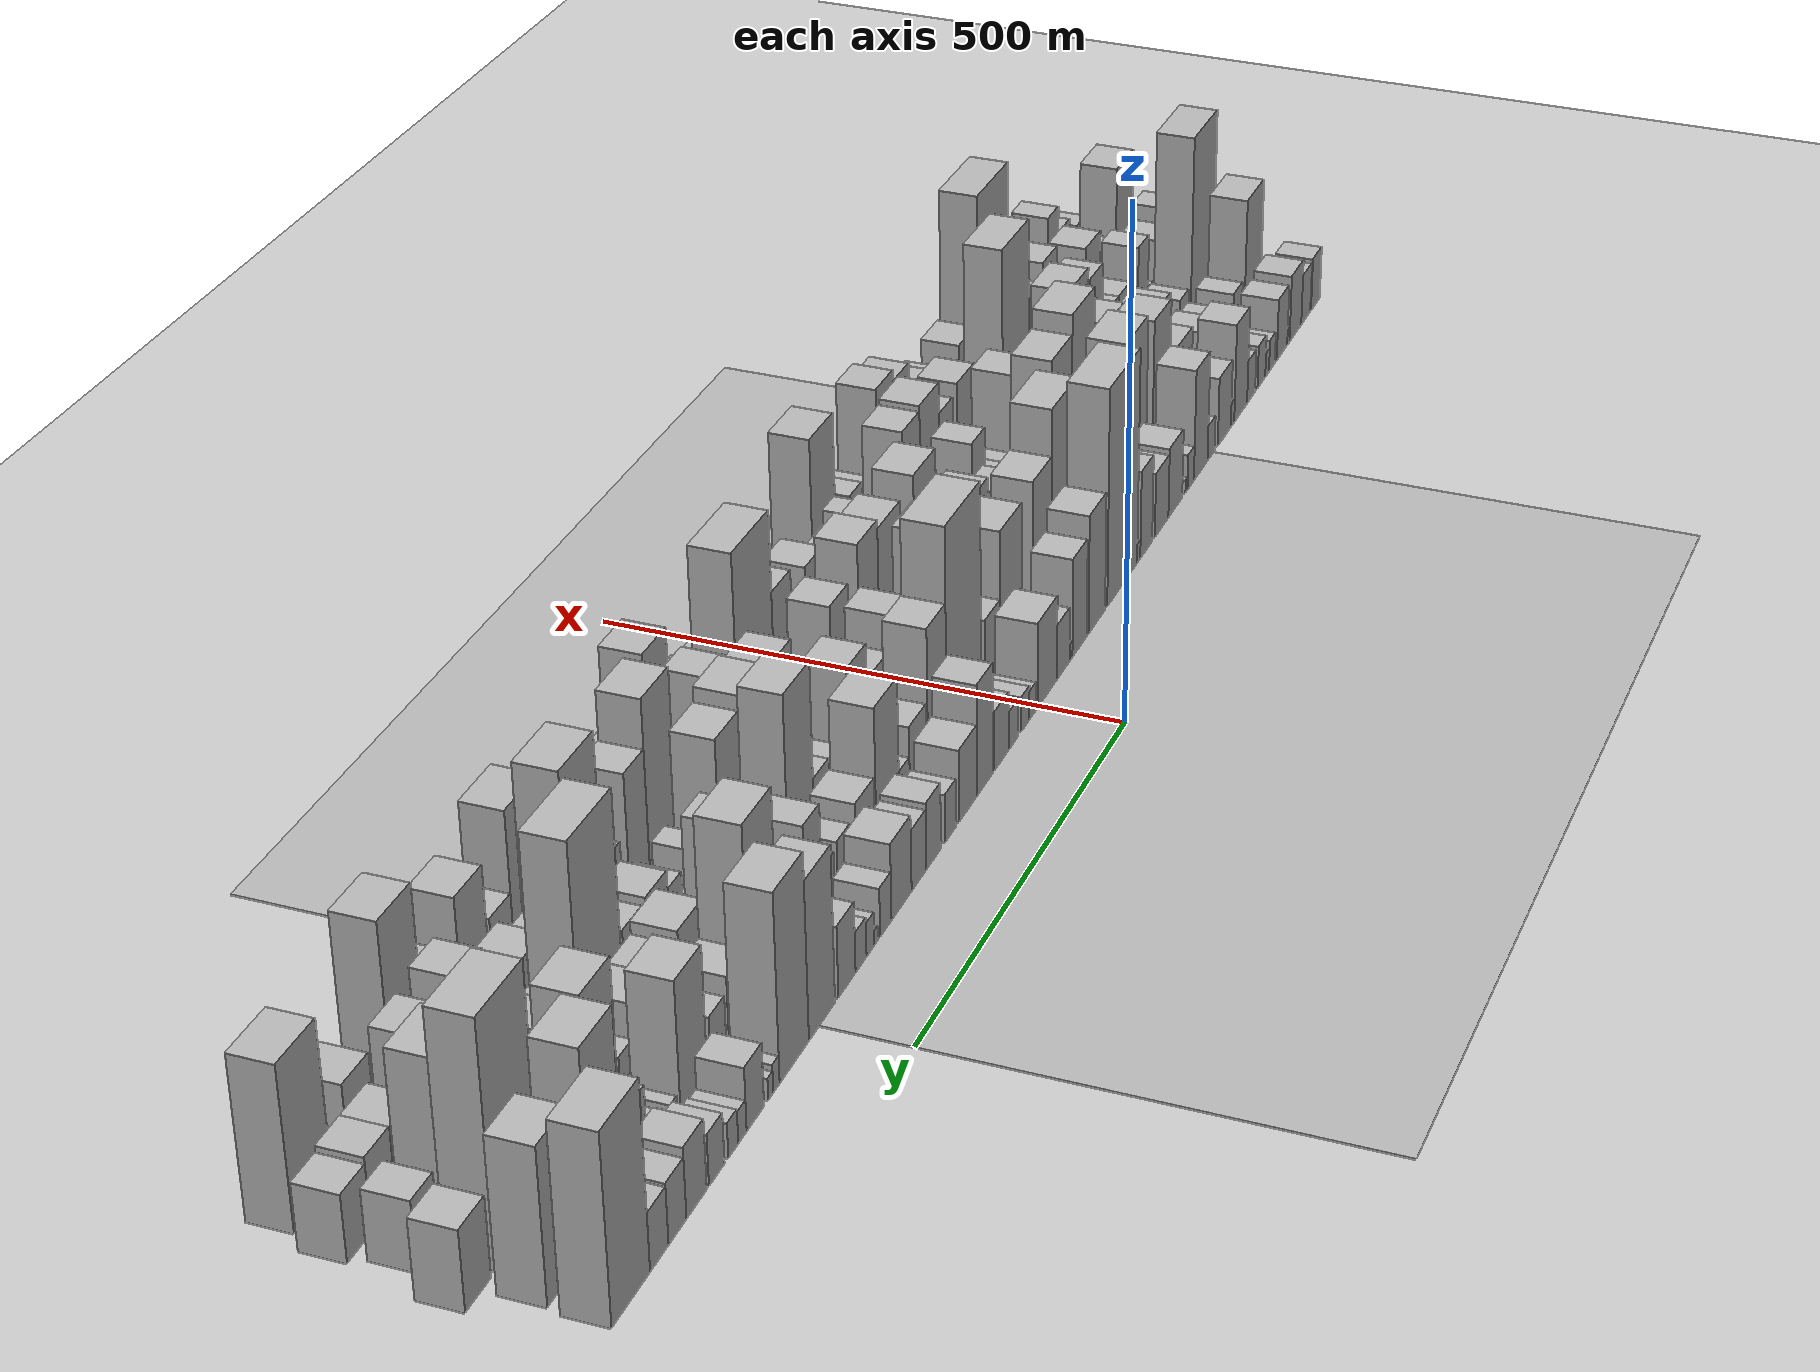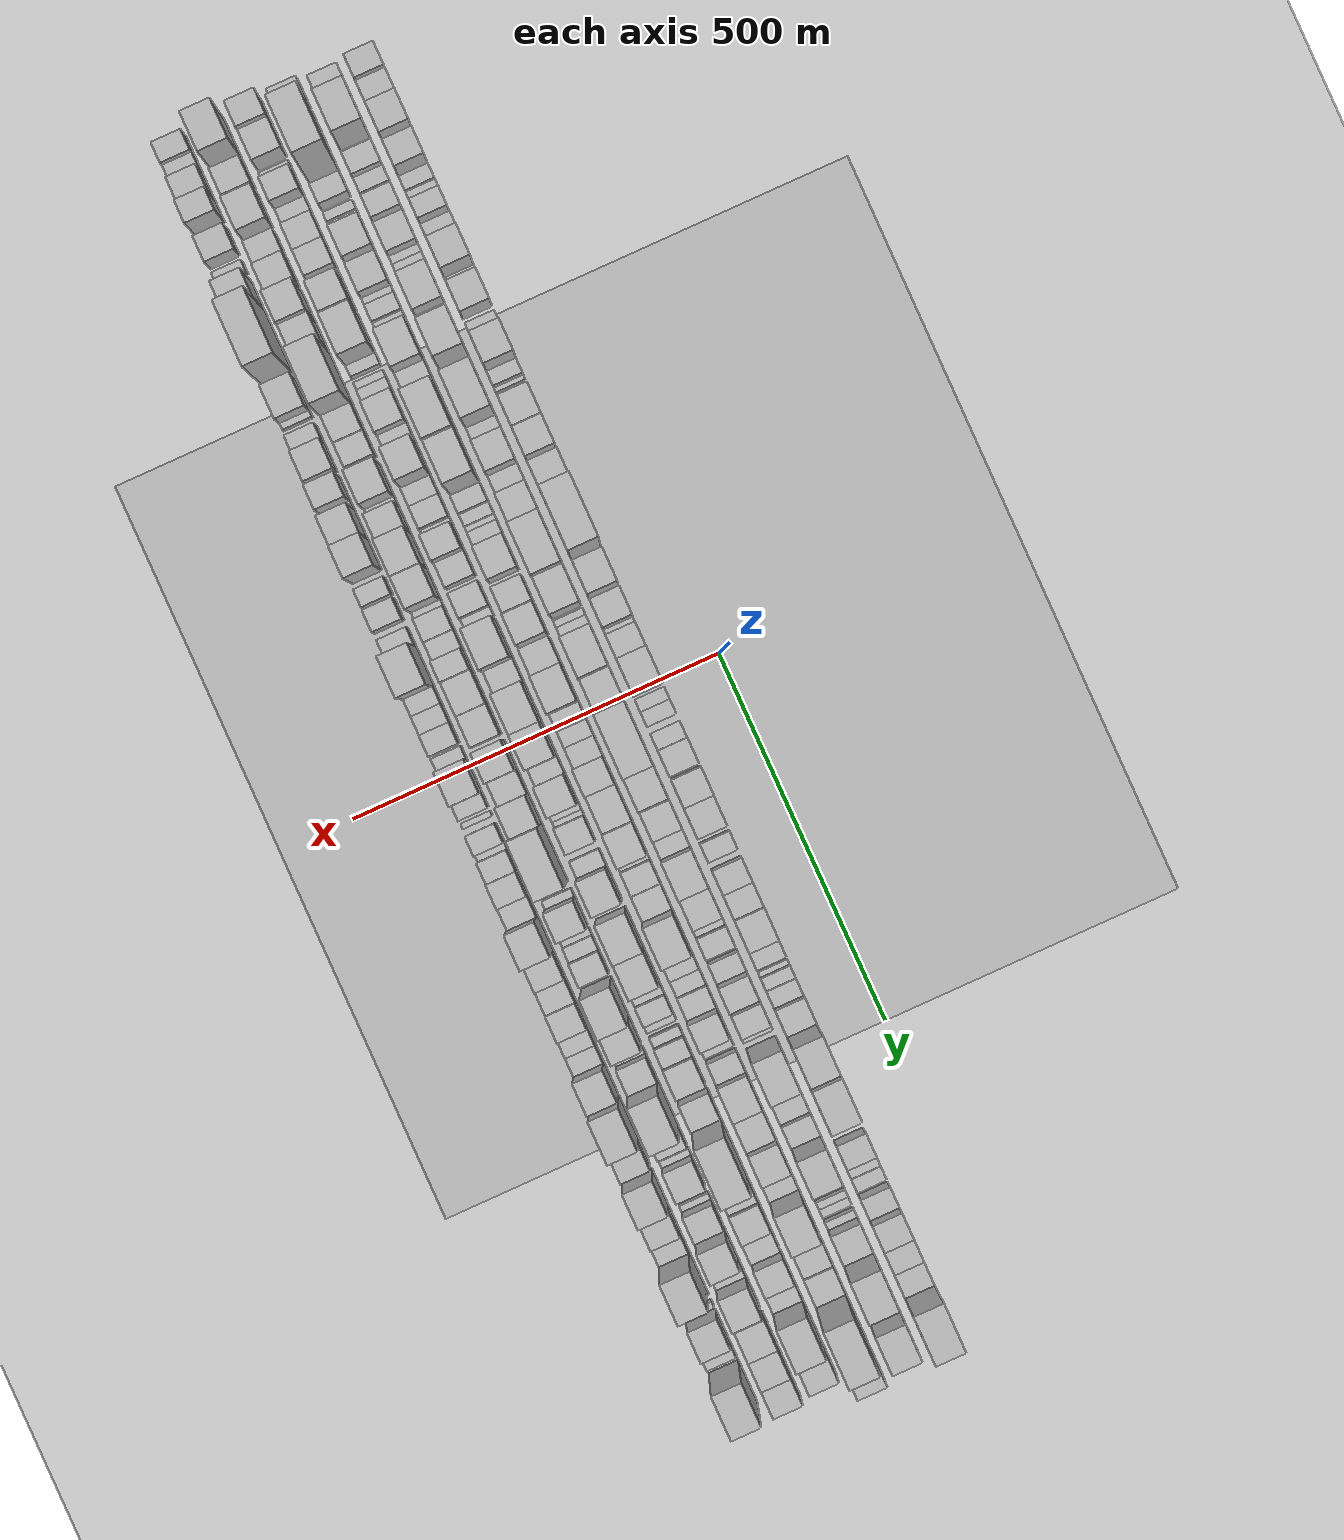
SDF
<?xml version="1.0" encoding="utf-8"?>

<sdf version="1.6">

   <world name="default">

      <gui fullscreen="0">

         <camera name="user_camera">

            <pose>-15 0 4.57585 0 0 0</pose>

            <view_controller>orbit</view_controller>

         </camera>

      </gui>

      <scene>

         <sky>

           <clouds>

             <speed>12</speed>

           </clouds>

         </sky>

         <ambient>0.4 0.4 0.4 1</ambient>

         <background>0.7 0.7 0.7 1</background>

         <shadows>1</shadows>

      </scene>

      <gravity>0 0 -9.8066</gravity>

      <magnetic_field>6e-06 2.3e-05 -4.2e-05</magnetic_field>

      <physics default="0" name="default_physics" type="ode">

         <ode>

            <solver>

               <type>quick</type>

               <iters>10</iters>

               <sor>1.0</sor>

               <use_dynamic_moi_rescaling>0</use_dynamic_moi_rescaling>

            </solver>

            <constraints>

               <cfm>0</cfm>

               <erp>0.2</erp>

               <contact_max_correcting_vel>100</contact_max_correcting_vel>

               <contact_surface_layer>0.001</contact_surface_layer>

            </constraints>

         </ode>

         <max_step_size>0.004</max_step_size>

         <real_time_factor>1</real_time_factor>

         <real_time_update_rate>250</real_time_update_rate>

      </physics>

      <light name="sun" type="directional">

         <cast_shadows>1</cast_shadows>

         <pose>0 0 10 0 0 0</pose>

         <diffuse>0.8 0.8 0.8 1</diffuse>

         <specular>0.2 0.2 0.2 1</specular>

         <attenuation>

            <range>1000</range>

            <constant>0.9</constant>

            <linear>0.01</linear>

            <quadratic>0.001</quadratic>

         </attenuation>

         <direction>-0.5 0.1 -0.9</direction>

      </light>

      <include>

         <name>ground_plane_1</name>

         <uri>model://HANNAS_ground_plane</uri>

         <pose>0 0 0  0 0 0</pose>

      </include>

      <include>

         <name>ground_plane_2</name>

         <uri>model://HANNAS_ground_plane</uri>

         <pose>100 0 0  0 0 0</pose>

      </include>

      <model name="building_1">

         <static>1</static>

         <pose frame="">100.0000 -843.9824 0 0.000000 0.000000 0.000000</pose>

         <link name="link">

            <pose frame="">0 0 30.00 0 0 0</pose>

            <collision name="collision">

               <geometry>

                  <box>

                     <size>40.0000 32.0353 60.0000</size>

                  </box>

               </geometry>

               <max_contacts>10</max_contacts>

               <surface>

                  <contact>

                     <ode/>

                  </contact>

                  <bounce/>

                  <friction>

                     <torsional>

                        <ode/>

                     </torsional>

                     <ode/>

                  </friction>

               </surface>

            </collision>

            <visual name="visual">

               <cast_shadows>0</cast_shadows>

               <geometry>

                  <box>

                     <size>40.0000 32.0353 60.0000</size>

                  </box>

               </geometry>

               <material>

                  <script>

                     <uri>model://HANNAS_wall/materials/scripts</uri>

                     <uri>model://HANNAS_wall/materials/textures</uri>

                     <name>vrc/HANNAS_wall</name>

                  </script>

               </material>

            </visual>

            <self_collide>0</self_collide>

            <enable_wind>0</enable_wind>

            <kinematic>0</kinematic>

         </link>

      </model>

      <model name="building_2">

         <static>1</static>

         <pose frame="">100.0000 -808.9889 0 0.000000 0.000000 0.000000</pose>

         <link name="link">

            <pose frame="">0 0 28.50 0 0 0</pose>

            <collision name="collision">

               <geometry>

                  <box>

                     <size>40.0000 31.9517 57.0000</size>

                  </box>

               </geometry>

               <max_contacts>10</max_contacts>

               <surface>

                  <contact>

                     <ode/>

                  </contact>

                  <bounce/>

                  <friction>

                     <torsional>

                        <ode/>

                     </torsional>

                     <ode/>

                  </friction>

               </surface>

            </collision>

            <visual name="visual">

               <cast_shadows>0</cast_shadows>

               <geometry>

                  <box>

                     <size>40.0000 31.9517 57.0000</size>

                  </box>

               </geometry>

               <material>

                  <script>

                     <uri>model://HANNAS_wall/materials/scripts</uri>

                     <uri>model://HANNAS_wall/materials/textures</uri>

                     <name>vrc/HANNAS_wall</name>

                  </script>

               </material>

            </visual>

            <self_collide>0</self_collide>

            <enable_wind>0</enable_wind>

            <kinematic>0</kinematic>

         </link>

      </model>

      <model name="building_3">

         <static>1</static>

         <pose frame="">100.0000 -772.3202 0 0.000000 0.000000 0.000000</pose>

         <link name="link">

            <pose frame="">0 0 37.50 0 0 0</pose>

            <collision name="collision">

               <geometry>

                  <box>

                     <size>40.0000 41.3855 75.0000</size>

                  </box>

               </geometry>

               <max_contacts>10</max_contacts>

               <surface>

                  <contact>

                     <ode/>

                  </contact>

                  <bounce/>

                  <friction>

                     <torsional>

                        <ode/>

                     </torsional>

                     <ode/>

                  </friction>

               </surface>

            </collision>

            <visual name="visual">

               <cast_shadows>0</cast_shadows>

               <geometry>

                  <box>

                     <size>40.0000 41.3855 75.0000</size>

                  </box>

               </geometry>

               <material>

                  <script>

                     <uri>model://HANNAS_wall/materials/scripts</uri>

                     <uri>model://HANNAS_wall/materials/textures</uri>

                     <name>vrc/HANNAS_wall</name>

                  </script>

               </material>

            </visual>

            <self_collide>0</self_collide>

            <enable_wind>0</enable_wind>

            <kinematic>0</kinematic>

         </link>

      </model>

      <model name="building_4">

         <static>1</static>

         <pose frame="">100.0000 -747.5614 0 0.000000 0.000000 0.000000</pose>

         <link name="link">

            <pose frame="">0 0 9.00 0 0 0</pose>

            <collision name="collision">

               <geometry>

                  <box>

                     <size>40.0000 8.1321 18.0000</size>

                  </box>

               </geometry>

               <max_contacts>10</max_contacts>

               <surface>

                  <contact>

                     <ode/>

                  </contact>

                  <bounce/>

                  <friction>

                     <torsional>

                        <ode/>

                     </torsional>

                     <ode/>

                  </friction>

               </surface>

            </collision>

            <visual name="visual">

               <cast_shadows>0</cast_shadows>

               <geometry>

                  <box>

                     <size>40.0000 8.1321 18.0000</size>

                  </box>

               </geometry>

               <material>

                  <script>

                     <uri>model://HANNAS_wall/materials/scripts</uri>

                     <uri>model://HANNAS_wall/materials/textures</uri>

                     <name>vrc/HANNAS_wall</name>

                  </script>

               </material>

            </visual>

            <self_collide>0</self_collide>

            <enable_wind>0</enable_wind>

            <kinematic>0</kinematic>

         </link>

      </model>

      <model name="building_5">

         <static>1</static>

         <pose frame="">100.0000 -725.3649 0 0.000000 0.000000 0.000000</pose>

         <link name="link">

            <pose frame="">0 0 34.50 0 0 0</pose>

            <collision name="collision">

               <geometry>

                  <box>

                     <size>40.0000 36.2610 69.0000</size>

                  </box>

               </geometry>

               <max_contacts>10</max_contacts>

               <surface>

                  <contact>

                     <ode/>

                  </contact>

                  <bounce/>

                  <friction>

                     <torsional>

                        <ode/>

                     </torsional>

                     <ode/>

                  </friction>

               </surface>

            </collision>

            <visual name="visual">

               <cast_shadows>0</cast_shadows>

               <geometry>

                  <box>

                     <size>40.0000 36.2610 69.0000</size>

                  </box>

               </geometry>

               <material>

                  <script>

                     <uri>model://HANNAS_wall/materials/scripts</uri>

                     <uri>model://HANNAS_wall/materials/textures</uri>

                     <name>vrc/HANNAS_wall</name>

                  </script>

               </material>

            </visual>

            <self_collide>0</self_collide>

            <enable_wind>0</enable_wind>

            <kinematic>0</kinematic>

         </link>

      </model>

      <model name="building_6">

         <static>1</static>

         <pose frame="">100.0000 -690.3947 0 0.000000 0.000000 0.000000</pose>

         <link name="link">

            <pose frame="">0 0 18.00 0 0 0</pose>

            <collision name="collision">

               <geometry>

                  <box>

                     <size>40.0000 19.6794 36.0000</size>

                  </box>

               </geometry>

               <max_contacts>10</max_contacts>

               <surface>

                  <contact>

                     <ode/>

                  </contact>

                  <bounce/>

                  <friction>

                     <torsional>

                        <ode/>

                     </torsional>

                     <ode/>

                  </friction>

               </surface>

            </collision>

            <visual name="visual">

               <cast_shadows>0</cast_shadows>

               <geometry>

                  <box>

                     <size>40.0000 19.6794 36.0000</size>

                  </box>

               </geometry>

               <material>

                  <script>

                     <uri>model://HANNAS_wall/materials/scripts</uri>

                     <uri>model://HANNAS_wall/materials/textures</uri>

                     <name>vrc/HANNAS_wall</name>

                  </script>

               </material>

            </visual>

            <self_collide>0</self_collide>

            <enable_wind>0</enable_wind>

            <kinematic>0</kinematic>

         </link>

      </model>

      <model name="building_7">

         <static>1</static>

         <pose frame="">100.0000 -674.1276 0 0.000000 0.000000 0.000000</pose>

         <link name="link">

            <pose frame="">0 0 13.50 0 0 0</pose>

            <collision name="collision">

               <geometry>

                  <box>

                     <size>40.0000 12.8548 27.0000</size>

                  </box>

               </geometry>

               <max_contacts>10</max_contacts>

               <surface>

                  <contact>

                     <ode/>

                  </contact>

                  <bounce/>

                  <friction>

                     <torsional>

                        <ode/>

                     </torsional>

                     <ode/>

                  </friction>

               </surface>

            </collision>

            <visual name="visual">

               <cast_shadows>0</cast_shadows>

               <geometry>

                  <box>

                     <size>40.0000 12.8548 27.0000</size>

                  </box>

               </geometry>

               <material>

                  <script>

                     <uri>model://HANNAS_wall/materials/scripts</uri>

                     <uri>model://HANNAS_wall/materials/textures</uri>

                     <name>vrc/HANNAS_wall</name>

                  </script>

               </material>

            </visual>

            <self_collide>0</self_collide>

            <enable_wind>0</enable_wind>

            <kinematic>0</kinematic>

         </link>

      </model>

      <model name="building_8">

         <static>1</static>

         <pose frame="">100.0000 -654.4805 0 0.000000 0.000000 0.000000</pose>

         <link name="link">

            <pose frame="">0 0 24.00 0 0 0</pose>

            <collision name="collision">

               <geometry>

                  <box>

                     <size>40.0000 26.4393 48.0000</size>

                  </box>

               </geometry>

               <max_contacts>10</max_contacts>

               <surface>

                  <contact>

                     <ode/>

                  </contact>

                  <bounce/>

                  <friction>

                     <torsional>

                        <ode/>

                     </torsional>

                     <ode/>

                  </friction>

               </surface>

            </collision>

            <visual name="visual">

               <cast_shadows>0</cast_shadows>

               <geometry>

                  <box>

                     <size>40.0000 26.4393 48.0000</size>

                  </box>

               </geometry>

               <material>

                  <script>

                     <uri>model://HANNAS_wall/materials/scripts</uri>

                     <uri>model://HANNAS_wall/materials/textures</uri>

                     <name>vrc/HANNAS_wall</name>

                  </script>

               </material>

            </visual>

            <self_collide>0</self_collide>

            <enable_wind>0</enable_wind>

            <kinematic>0</kinematic>

         </link>

      </model>

      <model name="building_9">

         <static>1</static>

         <pose frame="">100.0000 -619.9598 0 0.000000 0.000000 0.000000</pose>

         <link name="link">

            <pose frame="">0 0 24.00 0 0 0</pose>

            <collision name="collision">

               <geometry>

                  <box>

                     <size>40.0000 26.6021 48.0000</size>

                  </box>

               </geometry>

               <max_contacts>10</max_contacts>

               <surface>

                  <contact>

                     <ode/>

                  </contact>

                  <bounce/>

                  <friction>

                     <torsional>

                        <ode/>

                     </torsional>

                     <ode/>

                  </friction>

               </surface>

            </collision>

            <visual name="visual">

               <cast_shadows>0</cast_shadows>

               <geometry>

                  <box>

                     <size>40.0000 26.6021 48.0000</size>

                  </box>

               </geometry>

               <material>

                  <script>

                     <uri>model://HANNAS_wall/materials/scripts</uri>

                     <uri>model://HANNAS_wall/materials/textures</uri>

                     <name>vrc/HANNAS_wall</name>

                  </script>

               </material>

            </visual>

            <self_collide>0</self_collide>

            <enable_wind>0</enable_wind>

            <kinematic>0</kinematic>

         </link>

      </model>

      <model name="building_10">

         <static>1</static>

         <pose frame="">100.0000 -585.4479 0 0.000000 0.000000 0.000000</pose>

         <link name="link">

            <pose frame="">0 0 54.00 0 0 0</pose>

            <collision name="collision">

               <geometry>

                  <box>

                     <size>40.0000 42.4217 108.0000</size>

                  </box>

               </geometry>

               <max_contacts>10</max_contacts>

               <surface>

                  <contact>

                     <ode/>

                  </contact>

                  <bounce/>

                  <friction>

                     <torsional>

                        <ode/>

                     </torsional>

                     <ode/>

                  </friction>

               </surface>

            </collision>

            <visual name="visual">

               <cast_shadows>0</cast_shadows>

               <geometry>

                  <box>

                     <size>40.0000 42.4217 108.0000</size>

                  </box>

               </geometry>

               <material>

                  <script>

                     <uri>model://HANNAS_wall/materials/scripts</uri>

                     <uri>model://HANNAS_wall/materials/textures</uri>

                     <name>vrc/HANNAS_wall</name>

                  </script>

               </material>

            </visual>

            <self_collide>0</self_collide>

            <enable_wind>0</enable_wind>

            <kinematic>0</kinematic>

         </link>

      </model>

      <model name="building_11">

         <static>1</static>

         <pose frame="">100.0000 -558.7924 0 0.000000 0.000000 0.000000</pose>

         <link name="link">

            <pose frame="">0 0 13.50 0 0 0</pose>

            <collision name="collision">

               <geometry>

                  <box>

                     <size>40.0000 10.8893 27.0000</size>

                  </box>

               </geometry>

               <max_contacts>10</max_contacts>

               <surface>

                  <contact>

                     <ode/>

                  </contact>

                  <bounce/>

                  <friction>

                     <torsional>

                        <ode/>

                     </torsional>

                     <ode/>

                  </friction>

               </surface>

            </collision>

            <visual name="visual">

               <cast_shadows>0</cast_shadows>

               <geometry>

                  <box>

                     <size>40.0000 10.8893 27.0000</size>

                  </box>

               </geometry>

               <material>

                  <script>

                     <uri>model://HANNAS_wall/materials/scripts</uri>

                     <uri>model://HANNAS_wall/materials/textures</uri>

                     <name>vrc/HANNAS_wall</name>

                  </script>

               </material>

            </visual>

            <self_collide>0</self_collide>

            <enable_wind>0</enable_wind>

            <kinematic>0</kinematic>

         </link>

      </model>

      <model name="building_12">

         <static>1</static>

         <pose frame="">100.0000 -532.3244 0 0.000000 0.000000 0.000000</pose>

         <link name="link">

            <pose frame="">0 0 37.50 0 0 0</pose>

            <collision name="collision">

               <geometry>

                  <box>

                     <size>40.0000 42.0468 75.0000</size>

                  </box>

               </geometry>

               <max_contacts>10</max_contacts>

               <surface>

                  <contact>

                     <ode/>

                  </contact>

                  <bounce/>

                  <friction>

                     <torsional>

                        <ode/>

                     </torsional>

                     <ode/>

                  </friction>

               </surface>

            </collision>

            <visual name="visual">

               <cast_shadows>0</cast_shadows>

               <geometry>

                  <box>

                     <size>40.0000 42.0468 75.0000</size>

                  </box>

               </geometry>

               <material>

                  <script>

                     <uri>model://HANNAS_wall/materials/scripts</uri>

                     <uri>model://HANNAS_wall/materials/textures</uri>

                     <name>vrc/HANNAS_wall</name>

                  </script>

               </material>

            </visual>

            <self_collide>0</self_collide>

            <enable_wind>0</enable_wind>

            <kinematic>0</kinematic>

         </link>

      </model>

      <model name="building_13">

         <static>1</static>

         <pose frame="">100.0000 -490.0989 0 0.000000 0.000000 0.000000</pose>

         <link name="link">

            <pose frame="">0 0 19.50 0 0 0</pose>

            <collision name="collision">

               <geometry>

                  <box>

                     <size>40.0000 22.4042 39.0000</size>

                  </box>

               </geometry>

               <max_contacts>10</max_contacts>

               <surface>

                  <contact>

                     <ode/>

                  </contact>

                  <bounce/>

                  <friction>

                     <torsional>

                        <ode/>

                     </torsional>

                     <ode/>

                  </friction>

               </surface>

            </collision>

            <visual name="visual">

               <cast_shadows>0</cast_shadows>

               <geometry>

                  <box>

                     <size>40.0000 22.4042 39.0000</size>

                  </box>

               </geometry>

               <material>

                  <script>

                     <uri>model://HANNAS_wall/materials/scripts</uri>

                     <uri>model://HANNAS_wall/materials/textures</uri>

                     <name>vrc/HANNAS_wall</name>

                  </script>

               </material>

            </visual>

            <self_collide>0</self_collide>

            <enable_wind>0</enable_wind>

            <kinematic>0</kinematic>

         </link>

      </model>

      <model name="building_14">

         <static>1</static>

         <pose frame="">100.0000 -457.5138 0 0.000000 0.000000 0.000000</pose>

         <link name="link">

            <pose frame="">0 0 60.00 0 0 0</pose>

            <collision name="collision">

               <geometry>

                  <box>

                     <size>40.0000 42.7660 120.0000</size>

                  </box>

               </geometry>

               <max_contacts>10</max_contacts>

               <surface>

                  <contact>

                     <ode/>

                  </contact>

                  <bounce/>

                  <friction>

                     <torsional>

                        <ode/>

                     </torsional>

                     <ode/>

                  </friction>

               </surface>

            </collision>

            <visual name="visual">

               <cast_shadows>0</cast_shadows>

               <geometry>

                  <box>

                     <size>40.0000 42.7660 120.0000</size>

                  </box>

               </geometry>

               <material>

                  <script>

                     <uri>model://HANNAS_wall/materials/scripts</uri>

                     <uri>model://HANNAS_wall/materials/textures</uri>

                     <name>vrc/HANNAS_wall</name>

                  </script>

               </material>

            </visual>

            <self_collide>0</self_collide>

            <enable_wind>0</enable_wind>

            <kinematic>0</kinematic>

         </link>

      </model>

      <model name="building_15">

         <static>1</static>

         <pose frame="">100.0000 -426.2130 0 0.000000 0.000000 0.000000</pose>

         <link name="link">

            <pose frame="">0 0 19.50 0 0 0</pose>

            <collision name="collision">

               <geometry>

                  <box>

                     <size>40.0000 19.8356 39.0000</size>

                  </box>

               </geometry>

               <max_contacts>10</max_contacts>

               <surface>

                  <contact>

                     <ode/>

                  </contact>

                  <bounce/>

                  <friction>

                     <torsional>

                        <ode/>

                     </torsional>

                     <ode/>

                  </friction>

               </surface>

            </collision>

            <visual name="visual">

               <cast_shadows>0</cast_shadows>

               <geometry>

                  <box>

                     <size>40.0000 19.8356 39.0000</size>

                  </box>

               </geometry>

               <material>

                  <script>

                     <uri>model://HANNAS_wall/materials/scripts</uri>

                     <uri>model://HANNAS_wall/materials/textures</uri>

                     <name>vrc/HANNAS_wall</name>

                  </script>

               </material>

            </visual>

            <self_collide>0</self_collide>

            <enable_wind>0</enable_wind>

            <kinematic>0</kinematic>

         </link>

      </model>

      <model name="building_16">

         <static>1</static>

         <pose frame="">100.0000 -413.1849 0 0.000000 0.000000 0.000000</pose>

         <link name="link">

            <pose frame="">0 0 7.50 0 0 0</pose>

            <collision name="collision">

               <geometry>

                  <box>

                     <size>40.0000 6.2205 15.0000</size>

                  </box>

               </geometry>

               <max_contacts>10</max_contacts>

               <surface>

                  <contact>

                     <ode/>

                  </contact>

                  <bounce/>

                  <friction>

                     <torsional>

                        <ode/>

                     </torsional>

                     <ode/>

                  </friction>

               </surface>

            </collision>

            <visual name="visual">

               <cast_shadows>0</cast_shadows>

               <geometry>

                  <box>

                     <size>40.0000 6.2205 15.0000</size>

                  </box>

               </geometry>

               <material>

                  <script>

                     <uri>model://HANNAS_wall/materials/scripts</uri>

                     <uri>model://HANNAS_wall/materials/textures</uri>

                     <name>vrc/HANNAS_wall</name>

                  </script>

               </material>

            </visual>

            <self_collide>0</self_collide>

            <enable_wind>0</enable_wind>

            <kinematic>0</kinematic>

         </link>

      </model>

      <model name="building_17">

         <static>1</static>

         <pose frame="">100.0000 -379.1809 0 0.000000 0.000000 0.000000</pose>

         <link name="link">

            <pose frame="">0 0 37.50 0 0 0</pose>

            <collision name="collision">

               <geometry>

                  <box>

                     <size>40.0000 41.7877 75.0000</size>

                  </box>

               </geometry>

               <max_contacts>10</max_contacts>

               <surface>

                  <contact>

                     <ode/>

                  </contact>

                  <bounce/>

                  <friction>

                     <torsional>

                        <ode/>

                     </torsional>

                     <ode/>

                  </friction>

               </surface>

            </collision>

            <visual name="visual">

               <cast_shadows>0</cast_shadows>

               <geometry>

                  <box>

                     <size>40.0000 41.7877 75.0000</size>

                  </box>

               </geometry>

               <material>

                  <script>

                     <uri>model://HANNAS_wall/materials/scripts</uri>

                     <uri>model://HANNAS_wall/materials/textures</uri>

                     <name>vrc/HANNAS_wall</name>

                  </script>

               </material>

            </visual>

            <self_collide>0</self_collide>

            <enable_wind>0</enable_wind>

            <kinematic>0</kinematic>

         </link>

      </model>

      <model name="building_18">

         <static>1</static>

         <pose frame="">100.0000 -338.1877 0 0.000000 0.000000 0.000000</pose>

         <link name="link">

            <pose frame="">0 0 34.50 0 0 0</pose>

            <collision name="collision">

               <geometry>

                  <box>

                     <size>40.0000 40.1987 69.0000</size>

                  </box>

               </geometry>

               <max_contacts>10</max_contacts>

               <surface>

                  <contact>

                     <ode/>

                  </contact>

                  <bounce/>

                  <friction>

                     <torsional>

                        <ode/>

                     </torsional>

                     <ode/>

                  </friction>

               </surface>

            </collision>

            <visual name="visual">

               <cast_shadows>0</cast_shadows>

               <geometry>

                  <box>

                     <size>40.0000 40.1987 69.0000</size>

                  </box>

               </geometry>

               <material>

                  <script>

                     <uri>model://HANNAS_wall/materials/scripts</uri>

                     <uri>model://HANNAS_wall/materials/textures</uri>

                     <name>vrc/HANNAS_wall</name>

                  </script>

               </material>

            </visual>

            <self_collide>0</self_collide>

            <enable_wind>0</enable_wind>

            <kinematic>0</kinematic>

         </link>

      </model>

      <model name="building_19">

         <static>1</static>

         <pose frame="">100.0000 -292.8029 0 0.000000 0.000000 0.000000</pose>

         <link name="link">

            <pose frame="">0 0 46.50 0 0 0</pose>

            <collision name="collision">

               <geometry>

                  <box>

                     <size>40.0000 34.5709 93.0000</size>

                  </box>

               </geometry>

               <max_contacts>10</max_contacts>

               <surface>

                  <contact>

                     <ode/>

                  </contact>

                  <bounce/>

                  <friction>

                     <torsional>

                        <ode/>

                     </torsional>

                     <ode/>

                  </friction>

               </surface>

            </collision>

            <visual name="visual">

               <cast_shadows>0</cast_shadows>

               <geometry>

                  <box>

                     <size>40.0000 34.5709 93.0000</size>

                  </box>

               </geometry>

               <material>

                  <script>

                     <uri>model://HANNAS_wall/materials/scripts</uri>

                     <uri>model://HANNAS_wall/materials/textures</uri>

                     <name>vrc/HANNAS_wall</name>

                  </script>

               </material>

            </visual>

            <self_collide>0</self_collide>

            <enable_wind>0</enable_wind>

            <kinematic>0</kinematic>

         </link>

      </model>

      <model name="building_20">

         <static>1</static>

         <pose frame="">100.0000 -270.9125 0 0.000000 0.000000 0.000000</pose>

         <link name="link">

            <pose frame="">0 0 10.50 0 0 0</pose>

            <collision name="collision">

               <geometry>

                  <box>

                     <size>40.0000 9.2098 21.0000</size>

                  </box>

               </geometry>

               <max_contacts>10</max_contacts>

               <surface>

                  <contact>

                     <ode/>

                  </contact>

                  <bounce/>

                  <friction>

                     <torsional>

                        <ode/>

                     </torsional>

                     <ode/>

                  </friction>

               </surface>

            </collision>

            <visual name="visual">

               <cast_shadows>0</cast_shadows>

               <geometry>

                  <box>

                     <size>40.0000 9.2098 21.0000</size>

                  </box>

               </geometry>

               <material>

                  <script>

                     <uri>model://HANNAS_wall/materials/scripts</uri>

                     <uri>model://HANNAS_wall/materials/textures</uri>

                     <name>vrc/HANNAS_wall</name>

                  </script>

               </material>

            </visual>

            <self_collide>0</self_collide>

            <enable_wind>0</enable_wind>

            <kinematic>0</kinematic>

         </link>

      </model>

      <model name="building_21">

         <static>1</static>

         <pose frame="">100.0000 -223.9992 0 0.000000 0.000000 0.000000</pose>

         <link name="link">

            <pose frame="">0 0 112.50 0 0 0</pose>

            <collision name="collision">

               <geometry>

                  <box>

                     <size>40.0000 84.6168 225.0000</size>

                  </box>

               </geometry>

               <max_contacts>10</max_contacts>

               <surface>

                  <contact>

                     <ode/>

                  </contact>

                  <bounce/>

                  <friction>

                     <torsional>

                        <ode/>

                     </torsional>

                     <ode/>

                  </friction>

               </surface>

            </collision>

            <visual name="visual">

               <cast_shadows>0</cast_shadows>

               <geometry>

                  <box>

                     <size>40.0000 84.6168 225.0000</size>

                  </box>

               </geometry>

               <material>

                  <script>

                     <uri>model://HANNAS_wall/materials/scripts</uri>

                     <uri>model://HANNAS_wall/materials/textures</uri>

                     <name>vrc/HANNAS_wall</name>

                  </script>

               </material>

            </visual>

            <self_collide>0</self_collide>

            <enable_wind>0</enable_wind>

            <kinematic>0</kinematic>

         </link>

      </model>

      <model name="building_22">

         <static>1</static>

         <pose frame="">100.0000 -152.9791 0 0.000000 0.000000 0.000000</pose>

         <link name="link">

            <pose frame="">0 0 61.50 0 0 0</pose>

            <collision name="collision">

               <geometry>

                  <box>

                     <size>40.0000 45.4234 123.0000</size>

                  </box>

               </geometry>

               <max_contacts>10</max_contacts>

               <surface>

                  <contact>

                     <ode/>

                  </contact>

                  <bounce/>

                  <friction>

                     <torsional>

                        <ode/>

                     </torsional>

                     <ode/>

                  </friction>

               </surface>

            </collision>

            <visual name="visual">

               <cast_shadows>0</cast_shadows>

               <geometry>

                  <box>

                     <size>40.0000 45.4234 123.0000</size>

                  </box>

               </geometry>

               <material>

                  <script>

                     <uri>model://HANNAS_wall/materials/scripts</uri>

                     <uri>model://HANNAS_wall/materials/textures</uri>

                     <name>vrc/HANNAS_wall</name>

                  </script>

               </material>

            </visual>

            <self_collide>0</self_collide>

            <enable_wind>0</enable_wind>

            <kinematic>0</kinematic>

         </link>

      </model>

      <model name="building_23">

         <static>1</static>

         <pose frame="">100.0000 -106.0577 0 0.000000 0.000000 0.000000</pose>

         <link name="link">

            <pose frame="">0 0 51.00 0 0 0</pose>

            <collision name="collision">

               <geometry>

                  <box>

                     <size>40.0000 38.4194 102.0000</size>

                  </box>

               </geometry>

               <max_contacts>10</max_contacts>

               <surface>

                  <contact>

                     <ode/>

                  </contact>

                  <bounce/>

                  <friction>

                     <torsional>

                        <ode/>

                     </torsional>

                     <ode/>

                  </friction>

               </surface>

            </collision>

            <visual name="visual">

               <cast_shadows>0</cast_shadows>

               <geometry>

                  <box>

                     <size>40.0000 38.4194 102.0000</size>

                  </box>

               </geometry>

               <material>

                  <script>

                     <uri>model://HANNAS_wall/materials/scripts</uri>

                     <uri>model://HANNAS_wall/materials/textures</uri>

                     <name>vrc/HANNAS_wall</name>

                  </script>

               </material>

            </visual>

            <self_collide>0</self_collide>

            <enable_wind>0</enable_wind>

            <kinematic>0</kinematic>

         </link>

      </model>

      <model name="building_24">

         <static>1</static>

         <pose frame="">100.0000 -83.0893 0 0.000000 0.000000 0.000000</pose>

         <link name="link">

            <pose frame="">0 0 9.00 0 0 0</pose>

            <collision name="collision">

               <geometry>

                  <box>

                     <size>40.0000 7.5173 18.0000</size>

                  </box>

               </geometry>

               <max_contacts>10</max_contacts>

               <surface>

                  <contact>

                     <ode/>

                  </contact>

                  <bounce/>

                  <friction>

                     <torsional>

                        <ode/>

                     </torsional>

                     <ode/>

                  </friction>

               </surface>

            </collision>

            <visual name="visual">

               <cast_shadows>0</cast_shadows>

               <geometry>

                  <box>

                     <size>40.0000 7.5173 18.0000</size>

                  </box>

               </geometry>

               <material>

                  <script>

                     <uri>model://HANNAS_wall/materials/scripts</uri>

                     <uri>model://HANNAS_wall/materials/textures</uri>

                     <name>vrc/HANNAS_wall</name>

                  </script>

               </material>

            </visual>

            <self_collide>0</self_collide>

            <enable_wind>0</enable_wind>

            <kinematic>0</kinematic>

         </link>

      </model>

      <model name="building_25">

         <static>1</static>

         <pose frame="">100.0000 -62.7961 0 0.000000 0.000000 0.000000</pose>

         <link name="link">

            <pose frame="">0 0 28.50 0 0 0</pose>

            <collision name="collision">

               <geometry>

                  <box>

                     <size>40.0000 33.0693 57.0000</size>

                  </box>

               </geometry>

               <max_contacts>10</max_contacts>

               <surface>

                  <contact>

                     <ode/>

                  </contact>

                  <bounce/>

                  <friction>

                     <torsional>

                        <ode/>

                     </torsional>

                     <ode/>

                  </friction>

               </surface>

            </collision>

            <visual name="visual">

               <cast_shadows>0</cast_shadows>

               <geometry>

                  <box>

                     <size>40.0000 33.0693 57.0000</size>

                  </box>

               </geometry>

               <material>

                  <script>

                     <uri>model://HANNAS_wall/materials/scripts</uri>

                     <uri>model://HANNAS_wall/materials/textures</uri>

                     <name>vrc/HANNAS_wall</name>

                  </script>

               </material>

            </visual>

            <self_collide>0</self_collide>

            <enable_wind>0</enable_wind>

            <kinematic>0</kinematic>

         </link>

      </model>

      <model name="building_26">

         <static>1</static>

         <pose frame="">100.0000 -21.0965 0 0.000000 0.000000 0.000000</pose>

         <link name="link">

            <pose frame="">0 0 43.50 0 0 0</pose>

            <collision name="collision">

               <geometry>

                  <box>

                     <size>40.0000 50.3299 87.0000</size>

                  </box>

               </geometry>

               <max_contacts>10</max_contacts>

               <surface>

                  <contact>

                     <ode/>

                  </contact>

                  <bounce/>

                  <friction>

                     <torsional>

                        <ode/>

                     </torsional>

                     <ode/>

                  </friction>

               </surface>

            </collision>

            <visual name="visual">

               <cast_shadows>0</cast_shadows>

               <geometry>

                  <box>

                     <size>40.0000 50.3299 87.0000</size>

                  </box>

               </geometry>

               <material>

                  <script>

                     <uri>model://HANNAS_wall/materials/scripts</uri>

                     <uri>model://HANNAS_wall/materials/textures</uri>

                     <name>vrc/HANNAS_wall</name>

                  </script>

               </material>

            </visual>

            <self_collide>0</self_collide>

            <enable_wind>0</enable_wind>

            <kinematic>0</kinematic>

         </link>

      </model>

      <model name="building_27">

         <static>1</static>

         <pose frame="">100.0000 16.5725 0 0.000000 0.000000 0.000000</pose>

         <link name="link">

            <pose frame="">0 0 15.00 0 0 0</pose>

            <collision name="collision">

               <geometry>

                  <box>

                     <size>40.0000 17.0081 30.0000</size>

                  </box>

               </geometry>

               <max_contacts>10</max_contacts>

               <surface>

                  <contact>

                     <ode/>

                  </contact>

                  <bounce/>

                  <friction>

                     <torsional>

                        <ode/>

                     </torsional>

                     <ode/>

                  </friction>

               </surface>

            </collision>

            <visual name="visual">

               <cast_shadows>0</cast_shadows>

               <geometry>

                  <box>

                     <size>40.0000 17.0081 30.0000</size>

                  </box>

               </geometry>

               <material>

                  <script>

                     <uri>model://HANNAS_wall/materials/scripts</uri>

                     <uri>model://HANNAS_wall/materials/textures</uri>

                     <name>vrc/HANNAS_wall</name>

                  </script>

               </material>

            </visual>

            <self_collide>0</self_collide>

            <enable_wind>0</enable_wind>

            <kinematic>0</kinematic>

         </link>

      </model>

      <model name="building_28">

         <static>1</static>

         <pose frame="">100.0000 35.2071 0 0.000000 0.000000 0.000000</pose>

         <link name="link">

            <pose frame="">0 0 18.00 0 0 0</pose>

            <collision name="collision">

               <geometry>

                  <box>

                     <size>40.0000 20.2609 36.0000</size>

                  </box>

               </geometry>

               <max_contacts>10</max_contacts>

               <surface>

                  <contact>

                     <ode/>

                  </contact>

                  <bounce/>

                  <friction>

                     <torsional>

                        <ode/>

                     </torsional>

                     <ode/>

                  </friction>

               </surface>

            </collision>

            <visual name="visual">

               <cast_shadows>0</cast_shadows>

               <geometry>

                  <box>

                     <size>40.0000 20.2609 36.0000</size>

                  </box>

               </geometry>

               <material>

                  <script>

                     <uri>model://HANNAS_wall/materials/scripts</uri>

                     <uri>model://HANNAS_wall/materials/textures</uri>

                     <name>vrc/HANNAS_wall</name>

                  </script>

               </material>

            </visual>

            <self_collide>0</self_collide>

            <enable_wind>0</enable_wind>

            <kinematic>0</kinematic>

         </link>

      </model>

      <model name="building_29">

         <static>1</static>

         <pose frame="">100.0000 65.7200 0 0.000000 0.000000 0.000000</pose>

         <link name="link">

            <pose frame="">0 0 19.50 0 0 0</pose>

            <collision name="collision">

               <geometry>

                  <box>

                     <size>40.0000 22.7649 39.0000</size>

                  </box>

               </geometry>

               <max_contacts>10</max_contacts>

               <surface>

                  <contact>

                     <ode/>

                  </contact>

                  <bounce/>

                  <friction>

                     <torsional>

                        <ode/>

                     </torsional>

                     <ode/>

                  </friction>

               </surface>

            </collision>

            <visual name="visual">

               <cast_shadows>0</cast_shadows>

               <geometry>

                  <box>

                     <size>40.0000 22.7649 39.0000</size>

                  </box>

               </geometry>

               <material>

                  <script>

                     <uri>model://HANNAS_wall/materials/scripts</uri>

                     <uri>model://HANNAS_wall/materials/textures</uri>

                     <name>vrc/HANNAS_wall</name>

                  </script>

               </material>

            </visual>

            <self_collide>0</self_collide>

            <enable_wind>0</enable_wind>

            <kinematic>0</kinematic>

         </link>

      </model>

      <model name="building_30">

         <static>1</static>

         <pose frame="">100.0000 94.8843 0 0.000000 0.000000 0.000000</pose>

         <link name="link">

            <pose frame="">0 0 30.00 0 0 0</pose>

            <collision name="collision">

               <geometry>

                  <box>

                     <size>40.0000 35.5636 60.0000</size>

                  </box>

               </geometry>

               <max_contacts>10</max_contacts>

               <surface>

                  <contact>

                     <ode/>

                  </contact>

                  <bounce/>

                  <friction>

                     <torsional>

                        <ode/>

                     </torsional>

                     <ode/>

                  </friction>

               </surface>

            </collision>

            <visual name="visual">

               <cast_shadows>0</cast_shadows>

               <geometry>

                  <box>

                     <size>40.0000 35.5636 60.0000</size>

                  </box>

               </geometry>

               <material>

                  <script>

                     <uri>model://HANNAS_wall/materials/scripts</uri>

                     <uri>model://HANNAS_wall/materials/textures</uri>

                     <name>vrc/HANNAS_wall</name>

                  </script>

               </material>

            </visual>

            <self_collide>0</self_collide>

            <enable_wind>0</enable_wind>

            <kinematic>0</kinematic>

         </link>

      </model>

      <model name="building_31">

         <static>1</static>

         <pose frame="">100.0000 134.7887 0 0.000000 0.000000 0.000000</pose>

         <link name="link">

            <pose frame="">0 0 55.50 0 0 0</pose>

            <collision name="collision">

               <geometry>

                  <box>

                     <size>40.0000 38.2454 111.0000</size>

                  </box>

               </geometry>

               <max_contacts>10</max_contacts>

               <surface>

                  <contact>

                     <ode/>

                  </contact>

                  <bounce/>

                  <friction>

                     <torsional>

                        <ode/>

                     </torsional>

                     <ode/>

                  </friction>

               </surface>

            </collision>

            <visual name="visual">

               <cast_shadows>0</cast_shadows>

               <geometry>

                  <box>

                     <size>40.0000 38.2454 111.0000</size>

                  </box>

               </geometry>

               <material>

                  <script>

                     <uri>model://HANNAS_wall/materials/scripts</uri>

                     <uri>model://HANNAS_wall/materials/textures</uri>

                     <name>vrc/HANNAS_wall</name>

                  </script>

               </material>

            </visual>

            <self_collide>0</self_collide>

            <enable_wind>0</enable_wind>

            <kinematic>0</kinematic>

         </link>

      </model>

      <model name="building_32">

         <static>1</static>

         <pose frame="">100.0000 175.0350 0 0.000000 0.000000 0.000000</pose>

         <link name="link">

            <pose frame="">0 0 36.00 0 0 0</pose>

            <collision name="collision">

               <geometry>

                  <box>

                     <size>40.0000 42.2471 72.0000</size>

                  </box>

               </geometry>

               <max_contacts>10</max_contacts>

               <surface>

                  <contact>

                     <ode/>

                  </contact>

                  <bounce/>

                  <friction>

                     <torsional>

                        <ode/>

                     </torsional>

                     <ode/>

                  </friction>

               </surface>

            </collision>

            <visual name="visual">

               <cast_shadows>0</cast_shadows>

               <geometry>

                  <box>

                     <size>40.0000 42.2471 72.0000</size>

                  </box>

               </geometry>

               <material>

                  <script>

                     <uri>model://HANNAS_wall/materials/scripts</uri>

                     <uri>model://HANNAS_wall/materials/textures</uri>

                     <name>vrc/HANNAS_wall</name>

                  </script>

               </material>

            </visual>

            <self_collide>0</self_collide>

            <enable_wind>0</enable_wind>

            <kinematic>0</kinematic>

         </link>

      </model>

      <model name="building_33">

         <static>1</static>

         <pose frame="">100.0000 215.9216 0 0.000000 0.000000 0.000000</pose>

         <link name="link">

            <pose frame="">0 0 24.00 0 0 0</pose>

            <collision name="collision">

               <geometry>

                  <box>

                     <size>40.0000 25.5261 48.0000</size>

                  </box>

               </geometry>

               <max_contacts>10</max_contacts>

               <surface>

                  <contact>

                     <ode/>

                  </contact>

                  <bounce/>

                  <friction>

                     <torsional>

                        <ode/>

                     </torsional>

                     <ode/>

                  </friction>

               </surface>

            </collision>

            <visual name="visual">

               <cast_shadows>0</cast_shadows>

               <geometry>

                  <box>

                     <size>40.0000 25.5261 48.0000</size>

                  </box>

               </geometry>

               <material>

                  <script>

                     <uri>model://HANNAS_wall/materials/scripts</uri>

                     <uri>model://HANNAS_wall/materials/textures</uri>

                     <name>vrc/HANNAS_wall</name>

                  </script>

               </material>

            </visual>

            <self_collide>0</self_collide>

            <enable_wind>0</enable_wind>

            <kinematic>0</kinematic>

         </link>

      </model>

      <model name="building_34">

         <static>1</static>

         <pose frame="">100.0000 255.2590 0 0.000000 0.000000 0.000000</pose>

         <link name="link">

            <pose frame="">0 0 33.00 0 0 0</pose>

            <collision name="collision">

               <geometry>

                  <box>

                     <size>40.0000 33.1487 66.0000</size>

                  </box>

               </geometry>

               <max_contacts>10</max_contacts>

               <surface>

                  <contact>

                     <ode/>

                  </contact>

                  <bounce/>

                  <friction>

                     <torsional>

                        <ode/>

                     </torsional>

                     <ode/>

                  </friction>

               </surface>

            </collision>

            <visual name="visual">

               <cast_shadows>0</cast_shadows>

               <geometry>

                  <box>

                     <size>40.0000 33.1487 66.0000</size>

                  </box>

               </geometry>

               <material>

                  <script>

                     <uri>model://HANNAS_wall/materials/scripts</uri>

                     <uri>model://HANNAS_wall/materials/textures</uri>

                     <name>vrc/HANNAS_wall</name>

                  </script>

               </material>

            </visual>

            <self_collide>0</self_collide>

            <enable_wind>0</enable_wind>

            <kinematic>0</kinematic>

         </link>

      </model>

      <model name="building_35">

         <static>1</static>

         <pose frame="">100.0000 288.4761 0 0.000000 0.000000 0.000000</pose>

         <link name="link">

            <pose frame="">0 0 30.00 0 0 0</pose>

            <collision name="collision">

               <geometry>

                  <box>

                     <size>40.0000 33.2853 60.0000</size>

                  </box>

               </geometry>

               <max_contacts>10</max_contacts>

               <surface>

                  <contact>

                     <ode/>

                  </contact>

                  <bounce/>

                  <friction>

                     <torsional>

                        <ode/>

                     </torsional>

                     <ode/>

                  </friction>

               </surface>

            </collision>

            <visual name="visual">

               <cast_shadows>0</cast_shadows>

               <geometry>

                  <box>

                     <size>40.0000 33.2853 60.0000</size>

                  </box>

               </geometry>

               <material>

                  <script>

                     <uri>model://HANNAS_wall/materials/scripts</uri>

                     <uri>model://HANNAS_wall/materials/textures</uri>

                     <name>vrc/HANNAS_wall</name>

                  </script>

               </material>

            </visual>

            <self_collide>0</self_collide>

            <enable_wind>0</enable_wind>

            <kinematic>0</kinematic>

         </link>

      </model>

      <model name="building_36">

         <static>1</static>

         <pose frame="">100.0000 327.2402 0 0.000000 0.000000 0.000000</pose>

         <link name="link">

            <pose frame="">0 0 37.50 0 0 0</pose>

            <collision name="collision">

               <geometry>

                  <box>

                     <size>40.0000 44.2429 75.0000</size>

                  </box>

               </geometry>

               <max_contacts>10</max_contacts>

               <surface>

                  <contact>

                     <ode/>

                  </contact>

                  <bounce/>

                  <friction>

                     <torsional>

                        <ode/>

                     </torsional>

                     <ode/>

                  </friction>

               </surface>

            </collision>

            <visual name="visual">

               <cast_shadows>0</cast_shadows>

               <geometry>

                  <box>

                     <size>40.0000 44.2429 75.0000</size>

                  </box>

               </geometry>

               <material>

                  <script>

                     <uri>model://HANNAS_wall/materials/scripts</uri>

                     <uri>model://HANNAS_wall/materials/textures</uri>

                     <name>vrc/HANNAS_wall</name>

                  </script>

               </material>

            </visual>

            <self_collide>0</self_collide>

            <enable_wind>0</enable_wind>

            <kinematic>0</kinematic>

         </link>

      </model>

      <model name="building_37">

         <static>1</static>

         <pose frame="">100.0000 361.6530 0 0.000000 0.000000 0.000000</pose>

         <link name="link">

            <pose frame="">0 0 24.00 0 0 0</pose>

            <collision name="collision">

               <geometry>

                  <box>

                     <size>40.0000 24.5829 48.0000</size>

                  </box>

               </geometry>

               <max_contacts>10</max_contacts>

               <surface>

                  <contact>

                     <ode/>

                  </contact>

                  <bounce/>

                  <friction>

                     <torsional>

                        <ode/>

                     </torsional>

                     <ode/>

                  </friction>

               </surface>

            </collision>

            <visual name="visual">

               <cast_shadows>0</cast_shadows>

               <geometry>

                  <box>

                     <size>40.0000 24.5829 48.0000</size>

                  </box>

               </geometry>

               <material>

                  <script>

                     <uri>model://HANNAS_wall/materials/scripts</uri>

                     <uri>model://HANNAS_wall/materials/textures</uri>

                     <name>vrc/HANNAS_wall</name>

                  </script>

               </material>

            </visual>

            <self_collide>0</self_collide>

            <enable_wind>0</enable_wind>

            <kinematic>0</kinematic>

         </link>

      </model>

      <model name="building_38">

         <static>1</static>

         <pose frame="">100.0000 382.5229 0 0.000000 0.000000 0.000000</pose>

         <link name="link">

            <pose frame="">0 0 7.50 0 0 0</pose>

            <collision name="collision">

               <geometry>

                  <box>

                     <size>40.0000 7.1568 15.0000</size>

                  </box>

               </geometry>

               <max_contacts>10</max_contacts>

               <surface>

                  <contact>

                     <ode/>

                  </contact>

                  <bounce/>

                  <friction>

                     <torsional>

                        <ode/>

                     </torsional>

                     <ode/>

                  </friction>

               </surface>

            </collision>

            <visual name="visual">

               <cast_shadows>0</cast_shadows>

               <geometry>

                  <box>

                     <size>40.0000 7.1568 15.0000</size>

                  </box>

               </geometry>

               <material>

                  <script>

                     <uri>model://HANNAS_wall/materials/scripts</uri>

                     <uri>model://HANNAS_wall/materials/textures</uri>

                     <name>vrc/HANNAS_wall</name>

                  </script>

               </material>

            </visual>

            <self_collide>0</self_collide>

            <enable_wind>0</enable_wind>

            <kinematic>0</kinematic>

         </link>

      </model>

      <model name="building_39">

         <static>1</static>

         <pose frame="">100.0000 394.5761 0 0.000000 0.000000 0.000000</pose>

         <link name="link">

            <pose frame="">0 0 16.50 0 0 0</pose>

            <collision name="collision">

               <geometry>

                  <box>

                     <size>40.0000 16.9496 33.0000</size>

                  </box>

               </geometry>

               <max_contacts>10</max_contacts>

               <surface>

                  <contact>

                     <ode/>

                  </contact>

                  <bounce/>

                  <friction>

                     <torsional>

                        <ode/>

                     </torsional>

                     <ode/>

                  </friction>

               </surface>

            </collision>

            <visual name="visual">

               <cast_shadows>0</cast_shadows>

               <geometry>

                  <box>

                     <size>40.0000 16.9496 33.0000</size>

                  </box>

               </geometry>

               <material>

                  <script>

                     <uri>model://HANNAS_wall/materials/scripts</uri>

                     <uri>model://HANNAS_wall/materials/textures</uri>

                     <name>vrc/HANNAS_wall</name>

                  </script>

               </material>

            </visual>

            <self_collide>0</self_collide>

            <enable_wind>0</enable_wind>

            <kinematic>0</kinematic>

         </link>

      </model>

      <model name="building_40">

         <static>1</static>

         <pose frame="">100.0000 414.6169 0 0.000000 0.000000 0.000000</pose>

         <link name="link">

            <pose frame="">0 0 19.50 0 0 0</pose>

            <collision name="collision">

               <geometry>

                  <box>

                     <size>40.0000 23.1319 39.0000</size>

                  </box>

               </geometry>

               <max_contacts>10</max_contacts>

               <surface>

                  <contact>

                     <ode/>

                  </contact>

                  <bounce/>

                  <friction>

                     <torsional>

                        <ode/>

                     </torsional>

                     <ode/>

                  </friction>

               </surface>

            </collision>

            <visual name="visual">

               <cast_shadows>0</cast_shadows>

               <geometry>

                  <box>

                     <size>40.0000 23.1319 39.0000</size>

                  </box>

               </geometry>

               <material>

                  <script>

                     <uri>model://HANNAS_wall/materials/scripts</uri>

                     <uri>model://HANNAS_wall/materials/textures</uri>

                     <name>vrc/HANNAS_wall</name>

                  </script>

               </material>

            </visual>

            <self_collide>0</self_collide>

            <enable_wind>0</enable_wind>

            <kinematic>0</kinematic>

         </link>

      </model>

      <model name="building_41">

         <static>1</static>

         <pose frame="">100.0000 444.0717 0 0.000000 0.000000 0.000000</pose>

         <link name="link">

            <pose frame="">0 0 34.50 0 0 0</pose>

            <collision name="collision">

               <geometry>

                  <box>

                     <size>40.0000 35.7775 69.0000</size>

                  </box>

               </geometry>

               <max_contacts>10</max_contacts>

               <surface>

                  <contact>

                     <ode/>

                  </contact>

                  <bounce/>

                  <friction>

                     <torsional>

                        <ode/>

                     </torsional>

                     <ode/>

                  </friction>

               </surface>

            </collision>

            <visual name="visual">

               <cast_shadows>0</cast_shadows>

               <geometry>

                  <box>

                     <size>40.0000 35.7775 69.0000</size>

                  </box>

               </geometry>

               <material>

                  <script>

                     <uri>model://HANNAS_wall/materials/scripts</uri>

                     <uri>model://HANNAS_wall/materials/textures</uri>

                     <name>vrc/HANNAS_wall</name>

                  </script>

               </material>

            </visual>

            <self_collide>0</self_collide>

            <enable_wind>0</enable_wind>

            <kinematic>0</kinematic>

         </link>

      </model>

      <model name="building_42">

         <static>1</static>

         <pose frame="">100.0000 495.3269 0 0.000000 0.000000 0.000000</pose>

         <link name="link">

            <pose frame="">0 0 75.00 0 0 0</pose>

            <collision name="collision">

               <geometry>

                  <box>

                     <size>40.0000 52.7330 150.0000</size>

                  </box>

               </geometry>

               <max_contacts>10</max_contacts>

               <surface>

                  <contact>

                     <ode/>

                  </contact>

                  <bounce/>

                  <friction>

                     <torsional>

                        <ode/>

                     </torsional>

                     <ode/>

                  </friction>

               </surface>

            </collision>

            <visual name="visual">

               <cast_shadows>0</cast_shadows>

               <geometry>

                  <box>

                     <size>40.0000 52.7330 150.0000</size>

                  </box>

               </geometry>

               <material>

                  <script>

                     <uri>model://HANNAS_wall/materials/scripts</uri>

                     <uri>model://HANNAS_wall/materials/textures</uri>

                     <name>vrc/HANNAS_wall</name>

                  </script>

               </material>

            </visual>

            <self_collide>0</self_collide>

            <enable_wind>0</enable_wind>

            <kinematic>0</kinematic>

         </link>

      </model>

      <model name="building_43">

         <static>1</static>

         <pose frame="">100.0000 550.5331 0 0.000000 0.000000 0.000000</pose>

         <link name="link">

            <pose frame="">0 0 88.50 0 0 0</pose>

            <collision name="collision">

               <geometry>

                  <box>

                     <size>40.0000 57.6793 177.0000</size>

                  </box>

               </geometry>

               <max_contacts>10</max_contacts>

               <surface>

                  <contact>

                     <ode/>

                  </contact>

                  <bounce/>

                  <friction>

                     <torsional>

                        <ode/>

                     </torsional>

                     <ode/>

                  </friction>

               </surface>

            </collision>

            <visual name="visual">

               <cast_shadows>0</cast_shadows>

               <geometry>

                  <box>

                     <size>40.0000 57.6793 177.0000</size>

                  </box>

               </geometry>

               <material>

                  <script>

                     <uri>model://HANNAS_wall/materials/scripts</uri>

                     <uri>model://HANNAS_wall/materials/textures</uri>

                     <name>vrc/HANNAS_wall</name>

                  </script>

               </material>

            </visual>

            <self_collide>0</self_collide>

            <enable_wind>0</enable_wind>

            <kinematic>0</kinematic>

         </link>

      </model>

      <model name="building_44">

         <static>1</static>

         <pose frame="">100.0000 585.5421 0 0.000000 0.000000 0.000000</pose>

         <link name="link">

            <pose frame="">0 0 13.50 0 0 0</pose>

            <collision name="collision">

               <geometry>

                  <box>

                     <size>40.0000 12.3388 27.0000</size>

                  </box>

               </geometry>

               <max_contacts>10</max_contacts>

               <surface>

                  <contact>

                     <ode/>

                  </contact>

                  <bounce/>

                  <friction>

                     <torsional>

                        <ode/>

                     </torsional>

                     <ode/>

                  </friction>

               </surface>

            </collision>

            <visual name="visual">

               <cast_shadows>0</cast_shadows>

               <geometry>

                  <box>

                     <size>40.0000 12.3388 27.0000</size>

                  </box>

               </geometry>

               <material>

                  <script>

                     <uri>model://HANNAS_wall/materials/scripts</uri>

                     <uri>model://HANNAS_wall/materials/textures</uri>

                     <name>vrc/HANNAS_wall</name>

                  </script>

               </material>

            </visual>

            <self_collide>0</self_collide>

            <enable_wind>0</enable_wind>

            <kinematic>0</kinematic>

         </link>

      </model>

      <model name="building_45">

         <static>1</static>

         <pose frame="">100.0000 596.5791 0 0.000000 0.000000 0.000000</pose>

         <link name="link">

            <pose frame="">0 0 10.50 0 0 0</pose>

            <collision name="collision">

               <geometry>

                  <box>

                     <size>40.0000 9.7352 21.0000</size>

                  </box>

               </geometry>

               <max_contacts>10</max_contacts>

               <surface>

                  <contact>

                     <ode/>

                  </contact>

                  <bounce/>

                  <friction>

                     <torsional>

                        <ode/>

                     </torsional>

                     <ode/>

                  </friction>

               </surface>

            </collision>

            <visual name="visual">

               <cast_shadows>0</cast_shadows>

               <geometry>

                  <box>

                     <size>40.0000 9.7352 21.0000</size>

                  </box>

               </geometry>

               <material>

                  <script>

                     <uri>model://HANNAS_wall/materials/scripts</uri>

                     <uri>model://HANNAS_wall/materials/textures</uri>

                     <name>vrc/HANNAS_wall</name>

                  </script>

               </material>

            </visual>

            <self_collide>0</self_collide>

            <enable_wind>0</enable_wind>

            <kinematic>0</kinematic>

         </link>

      </model>

      <model name="building_46">

         <static>1</static>

         <pose frame="">100.0000 625.8755 0 0.000000 0.000000 0.000000</pose>

         <link name="link">

            <pose frame="">0 0 30.00 0 0 0</pose>

            <collision name="collision">

               <geometry>

                  <box>

                     <size>40.0000 32.8577 60.0000</size>

                  </box>

               </geometry>

               <max_contacts>10</max_contacts>

               <surface>

                  <contact>

                     <ode/>

                  </contact>

                  <bounce/>

                  <friction>

                     <torsional>

                        <ode/>

                     </torsional>

                     <ode/>

                  </friction>

               </surface>

            </collision>

            <visual name="visual">

               <cast_shadows>0</cast_shadows>

               <geometry>

                  <box>

                     <size>40.0000 32.8577 60.0000</size>

                  </box>

               </geometry>

               <material>

                  <script>

                     <uri>model://HANNAS_wall/materials/scripts</uri>

                     <uri>model://HANNAS_wall/materials/textures</uri>

                     <name>vrc/HANNAS_wall</name>

                  </script>

               </material>

            </visual>

            <self_collide>0</self_collide>

            <enable_wind>0</enable_wind>

            <kinematic>0</kinematic>

         </link>

      </model>

      <model name="building_47">

         <static>1</static>

         <pose frame="">100.0000 650.1527 0 0.000000 0.000000 0.000000</pose>

         <link name="link">

            <pose frame="">0 0 15.00 0 0 0</pose>

            <collision name="collision">

               <geometry>

                  <box>

                     <size>40.0000 15.6966 30.0000</size>

                  </box>

               </geometry>

               <max_contacts>10</max_contacts>

               <surface>

                  <contact>

                     <ode/>

                  </contact>

                  <bounce/>

                  <friction>

                     <torsional>

                        <ode/>

                     </torsional>

                     <ode/>

                  </friction>

               </surface>

            </collision>

            <visual name="visual">

               <cast_shadows>0</cast_shadows>

               <geometry>

                  <box>

                     <size>40.0000 15.6966 30.0000</size>

                  </box>

               </geometry>

               <material>

                  <script>

                     <uri>model://HANNAS_wall/materials/scripts</uri>

                     <uri>model://HANNAS_wall/materials/textures</uri>

                     <name>vrc/HANNAS_wall</name>

                  </script>

               </material>

            </visual>

            <self_collide>0</self_collide>

            <enable_wind>0</enable_wind>

            <kinematic>0</kinematic>

         </link>

      </model>

      <model name="building_48">

         <static>1</static>

         <pose frame="">100.0000 667.2027 0 0.000000 0.000000 0.000000</pose>

         <link name="link">

            <pose frame="">0 0 16.50 0 0 0</pose>

            <collision name="collision">

               <geometry>

                  <box>

                     <size>40.0000 18.4036 33.0000</size>

                  </box>

               </geometry>

               <max_contacts>10</max_contacts>

               <surface>

                  <contact>

                     <ode/>

                  </contact>

                  <bounce/>

                  <friction>

                     <torsional>

                        <ode/>

                     </torsional>

                     <ode/>

                  </friction>

               </surface>

            </collision>

            <visual name="visual">

               <cast_shadows>0</cast_shadows>

               <geometry>

                  <box>

                     <size>40.0000 18.4036 33.0000</size>

                  </box>

               </geometry>

               <material>

                  <script>

                     <uri>model://HANNAS_wall/materials/scripts</uri>

                     <uri>model://HANNAS_wall/materials/textures</uri>

                     <name>vrc/HANNAS_wall</name>

                  </script>

               </material>

            </visual>

            <self_collide>0</self_collide>

            <enable_wind>0</enable_wind>

            <kinematic>0</kinematic>

         </link>

      </model>

      <model name="building_49">

         <static>1</static>

         <pose frame="">100.0000 697.5780 0 0.000000 0.000000 0.000000</pose>

         <link name="link">

            <pose frame="">0 0 24.00 0 0 0</pose>

            <collision name="collision">

               <geometry>

                  <box>

                     <size>40.0000 28.3470 48.0000</size>

                  </box>

               </geometry>

               <max_contacts>10</max_contacts>

               <surface>

                  <contact>

                     <ode/>

                  </contact>

                  <bounce/>

                  <friction>

                     <torsional>

                        <ode/>

                     </torsional>

                     <ode/>

                  </friction>

               </surface>

            </collision>

            <visual name="visual">

               <cast_shadows>0</cast_shadows>

               <geometry>

                  <box>

                     <size>40.0000 28.3470 48.0000</size>

                  </box>

               </geometry>

               <material>

                  <script>

                     <uri>model://HANNAS_wall/materials/scripts</uri>

                     <uri>model://HANNAS_wall/materials/textures</uri>

                     <name>vrc/HANNAS_wall</name>

                  </script>

               </material>

            </visual>

            <self_collide>0</self_collide>

            <enable_wind>0</enable_wind>

            <kinematic>0</kinematic>

         </link>

      </model>

      <model name="building_50">

         <static>1</static>

         <pose frame="">100.0000 733.8531 0 0.000000 0.000000 0.000000</pose>

         <link name="link">

            <pose frame="">0 0 33.00 0 0 0</pose>

            <collision name="collision">

               <geometry>

                  <box>

                     <size>40.0000 36.2032 66.0000</size>

                  </box>

               </geometry>

               <max_contacts>10</max_contacts>

               <surface>

                  <contact>

                     <ode/>

                  </contact>

                  <bounce/>

                  <friction>

                     <torsional>

                        <ode/>

                     </torsional>

                     <ode/>

                  </friction>

               </surface>

            </collision>

            <visual name="visual">

               <cast_shadows>0</cast_shadows>

               <geometry>

                  <box>

                     <size>40.0000 36.2032 66.0000</size>

                  </box>

               </geometry>

               <material>

                  <script>

                     <uri>model://HANNAS_wall/materials/scripts</uri>

                     <uri>model://HANNAS_wall/materials/textures</uri>

                     <name>vrc/HANNAS_wall</name>

                  </script>

               </material>

            </visual>

            <self_collide>0</self_collide>

            <enable_wind>0</enable_wind>

            <kinematic>0</kinematic>

         </link>

      </model>

      <model name="building_51">

         <static>1</static>

         <pose frame="">100.0000 767.6744 0 0.000000 0.000000 0.000000</pose>

         <link name="link">

            <pose frame="">0 0 28.50 0 0 0</pose>

            <collision name="collision">

               <geometry>

                  <box>

                     <size>40.0000 31.4392 57.0000</size>

                  </box>

               </geometry>

               <max_contacts>10</max_contacts>

               <surface>

                  <contact>

                     <ode/>

                  </contact>

                  <bounce/>

                  <friction>

                     <torsional>

                        <ode/>

                     </torsional>

                     <ode/>

                  </friction>

               </surface>

            </collision>

            <visual name="visual">

               <cast_shadows>0</cast_shadows>

               <geometry>

                  <box>

                     <size>40.0000 31.4392 57.0000</size>

                  </box>

               </geometry>

               <material>

                  <script>

                     <uri>model://HANNAS_wall/materials/scripts</uri>

                     <uri>model://HANNAS_wall/materials/textures</uri>

                     <name>vrc/HANNAS_wall</name>

                  </script>

               </material>

            </visual>

            <self_collide>0</self_collide>

            <enable_wind>0</enable_wind>

            <kinematic>0</kinematic>

         </link>

      </model>

      <model name="building_52">

         <static>1</static>

         <pose frame="">100.0000 799.3085 0 0.000000 0.000000 0.000000</pose>

         <link name="link">

            <pose frame="">0 0 27.00 0 0 0</pose>

            <collision name="collision">

               <geometry>

                  <box>

                     <size>40.0000 31.8290 54.0000</size>

                  </box>

               </geometry>

               <max_contacts>10</max_contacts>

               <surface>

                  <contact>

                     <ode/>

                  </contact>

                  <bounce/>

                  <friction>

                     <torsional>

                        <ode/>

                     </torsional>

                     <ode/>

                  </friction>

               </surface>

            </collision>

            <visual name="visual">

               <cast_shadows>0</cast_shadows>

               <geometry>

                  <box>

                     <size>40.0000 31.8290 54.0000</size>

                  </box>

               </geometry>

               <material>

                  <script>

                     <uri>model://HANNAS_wall/materials/scripts</uri>

                     <uri>model://HANNAS_wall/materials/textures</uri>

                     <name>vrc/HANNAS_wall</name>

                  </script>

               </material>

            </visual>

            <self_collide>0</self_collide>

            <enable_wind>0</enable_wind>

            <kinematic>0</kinematic>

         </link>

      </model>

      <model name="building_53">

         <static>1</static>

         <pose frame="">100.0000 847.6762 0 0.000000 0.000000 0.000000</pose>

         <link name="link">

            <pose frame="">0 0 87.00 0 0 0</pose>

            <collision name="collision">

               <geometry>

                  <box>

                     <size>40.0000 64.9065 174.0000</size>

                  </box>

               </geometry>

               <max_contacts>10</max_contacts>

               <surface>

                  <contact>

                     <ode/>

                  </contact>

                  <bounce/>

                  <friction>

                     <torsional>

                        <ode/>

                     </torsional>

                     <ode/>

                  </friction>

               </surface>

            </collision>

            <visual name="visual">

               <cast_shadows>0</cast_shadows>

               <geometry>

                  <box>

                     <size>40.0000 64.9065 174.0000</size>

                  </box>

               </geometry>

               <material>

                  <script>

                     <uri>model://HANNAS_wall/materials/scripts</uri>

                     <uri>model://HANNAS_wall/materials/textures</uri>

                     <name>vrc/HANNAS_wall</name>

                  </script>

               </material>

            </visual>

            <self_collide>0</self_collide>

            <enable_wind>0</enable_wind>

            <kinematic>0</kinematic>

         </link>

      </model>

      <model name="building_54">

         <static>1</static>

         <pose frame="">152.0000 -849.9391 0 0.000000 0.000000 0.000000</pose>

         <link name="link">

            <pose frame="">0 0 18.00 0 0 0</pose>

            <collision name="collision">

               <geometry>

                  <box>

                     <size>40.0000 20.1219 36.0000</size>

                  </box>

               </geometry>

               <max_contacts>10</max_contacts>

               <surface>

                  <contact>

                     <ode/>

                  </contact>

                  <bounce/>

                  <friction>

                     <torsional>

                        <ode/>

                     </torsional>

                     <ode/>

                  </friction>

               </surface>

            </collision>

            <visual name="visual">

               <cast_shadows>0</cast_shadows>

               <geometry>

                  <box>

                     <size>40.0000 20.1219 36.0000</size>

                  </box>

               </geometry>

               <material>

                  <script>

                     <uri>model://HANNAS_wall/materials/scripts</uri>

                     <uri>model://HANNAS_wall/materials/textures</uri>

                     <name>vrc/HANNAS_wall</name>

                  </script>

               </material>

            </visual>

            <self_collide>0</self_collide>

            <enable_wind>0</enable_wind>

            <kinematic>0</kinematic>

         </link>

      </model>

      <model name="building_55">

         <static>1</static>

         <pose frame="">152.0000 -828.3046 0 0.000000 0.000000 0.000000</pose>

         <link name="link">

            <pose frame="">0 0 19.50 0 0 0</pose>

            <collision name="collision">

               <geometry>

                  <box>

                     <size>40.0000 23.1471 39.0000</size>

                  </box>

               </geometry>

               <max_contacts>10</max_contacts>

               <surface>

                  <contact>

                     <ode/>

                  </contact>

                  <bounce/>

                  <friction>

                     <torsional>

                        <ode/>

                     </torsional>

                     <ode/>

                  </friction>

               </surface>

            </collision>

            <visual name="visual">

               <cast_shadows>0</cast_shadows>

               <geometry>

                  <box>

                     <size>40.0000 23.1471 39.0000</size>

                  </box>

               </geometry>

               <material>

                  <script>

                     <uri>model://HANNAS_wall/materials/scripts</uri>

                     <uri>model://HANNAS_wall/materials/textures</uri>

                     <name>vrc/HANNAS_wall</name>

                  </script>

               </material>

            </visual>

            <self_collide>0</self_collide>

            <enable_wind>0</enable_wind>

            <kinematic>0</kinematic>

         </link>

      </model>

      <model name="building_56">

         <static>1</static>

         <pose frame="">152.0000 -788.7772 0 0.000000 0.000000 0.000000</pose>

         <link name="link">

            <pose frame="">0 0 73.50 0 0 0</pose>

            <collision name="collision">

               <geometry>

                  <box>

                     <size>40.0000 55.9077 147.0000</size>

                  </box>

               </geometry>

               <max_contacts>10</max_contacts>

               <surface>

                  <contact>

                     <ode/>

                  </contact>

                  <bounce/>

                  <friction>

                     <torsional>

                        <ode/>

                     </torsional>

                     <ode/>

                  </friction>

               </surface>

            </collision>

            <visual name="visual">

               <cast_shadows>0</cast_shadows>

               <geometry>

                  <box>

                     <size>40.0000 55.9077 147.0000</size>

                  </box>

               </geometry>

               <material>

                  <script>

                     <uri>model://HANNAS_wall/materials/scripts</uri>

                     <uri>model://HANNAS_wall/materials/textures</uri>

                     <name>vrc/HANNAS_wall</name>

                  </script>

               </material>

            </visual>

            <self_collide>0</self_collide>

            <enable_wind>0</enable_wind>

            <kinematic>0</kinematic>

         </link>

      </model>

      <model name="building_57">

         <static>1</static>

         <pose frame="">152.0000 -756.2359 0 0.000000 0.000000 0.000000</pose>

         <link name="link">

            <pose frame="">0 0 10.50 0 0 0</pose>

            <collision name="collision">

               <geometry>

                  <box>

                     <size>40.0000 9.1748 21.0000</size>

                  </box>

               </geometry>

               <max_contacts>10</max_contacts>

               <surface>

                  <contact>

                     <ode/>

                  </contact>

                  <bounce/>

                  <friction>

                     <torsional>

                        <ode/>

                     </torsional>

                     <ode/>

                  </friction>

               </surface>

            </collision>

            <visual name="visual">

               <cast_shadows>0</cast_shadows>

               <geometry>

                  <box>

                     <size>40.0000 9.1748 21.0000</size>

                  </box>

               </geometry>

               <material>

                  <script>

                     <uri>model://HANNAS_wall/materials/scripts</uri>

                     <uri>model://HANNAS_wall/materials/textures</uri>

                     <name>vrc/HANNAS_wall</name>

                  </script>

               </material>

            </visual>

            <self_collide>0</self_collide>

            <enable_wind>0</enable_wind>

            <kinematic>0</kinematic>

         </link>

      </model>

      <model name="building_58">

         <static>1</static>

         <pose frame="">152.0000 -736.5717 0 0.000000 0.000000 0.000000</pose>

         <link name="link">

            <pose frame="">0 0 30.00 0 0 0</pose>

            <collision name="collision">

               <geometry>

                  <box>

                     <size>40.0000 30.1537 60.0000</size>

                  </box>

               </geometry>

               <max_contacts>10</max_contacts>

               <surface>

                  <contact>

                     <ode/>

                  </contact>

                  <bounce/>

                  <friction>

                     <torsional>

                        <ode/>

                     </torsional>

                     <ode/>

                  </friction>

               </surface>

            </collision>

            <visual name="visual">

               <cast_shadows>0</cast_shadows>

               <geometry>

                  <box>

                     <size>40.0000 30.1537 60.0000</size>

                  </box>

               </geometry>

               <material>

                  <script>

                     <uri>model://HANNAS_wall/materials/scripts</uri>

                     <uri>model://HANNAS_wall/materials/textures</uri>

                     <name>vrc/HANNAS_wall</name>

                  </script>

               </material>

            </visual>

            <self_collide>0</self_collide>

            <enable_wind>0</enable_wind>

            <kinematic>0</kinematic>

         </link>

      </model>

      <model name="building_59">

         <static>1</static>

         <pose frame="">152.0000 -711.0930 0 0.000000 0.000000 0.000000</pose>

         <link name="link">

            <pose frame="">0 0 18.00 0 0 0</pose>

            <collision name="collision">

               <geometry>

                  <box>

                     <size>40.0000 20.8037 36.0000</size>

                  </box>

               </geometry>

               <max_contacts>10</max_contacts>

               <surface>

                  <contact>

                     <ode/>

                  </contact>

                  <bounce/>

                  <friction>

                     <torsional>

                        <ode/>

                     </torsional>

                     <ode/>

                  </friction>

               </surface>

            </collision>

            <visual name="visual">

               <cast_shadows>0</cast_shadows>

               <geometry>

                  <box>

                     <size>40.0000 20.8037 36.0000</size>

                  </box>

               </geometry>

               <material>

                  <script>

                     <uri>model://HANNAS_wall/materials/scripts</uri>

                     <uri>model://HANNAS_wall/materials/textures</uri>

                     <name>vrc/HANNAS_wall</name>

                  </script>

               </material>

            </visual>

            <self_collide>0</self_collide>

            <enable_wind>0</enable_wind>

            <kinematic>0</kinematic>

         </link>

      </model>

      <model name="building_60">

         <static>1</static>

         <pose frame="">152.0000 -679.4132 0 0.000000 0.000000 0.000000</pose>

         <link name="link">

            <pose frame="">0 0 28.50 0 0 0</pose>

            <collision name="collision">

               <geometry>

                  <box>

                     <size>40.0000 30.5560 57.0000</size>

                  </box>

               </geometry>

               <max_contacts>10</max_contacts>

               <surface>

                  <contact>

                     <ode/>

                  </contact>

                  <bounce/>

                  <friction>

                     <torsional>

                        <ode/>

                     </torsional>

                     <ode/>

                  </friction>

               </surface>

            </collision>

            <visual name="visual">

               <cast_shadows>0</cast_shadows>

               <geometry>

                  <box>

                     <size>40.0000 30.5560 57.0000</size>

                  </box>

               </geometry>

               <material>

                  <script>

                     <uri>model://HANNAS_wall/materials/scripts</uri>

                     <uri>model://HANNAS_wall/materials/textures</uri>

                     <name>vrc/HANNAS_wall</name>

                  </script>

               </material>

            </visual>

            <self_collide>0</self_collide>

            <enable_wind>0</enable_wind>

            <kinematic>0</kinematic>

         </link>

      </model>

      <model name="building_61">

         <static>1</static>

         <pose frame="">152.0000 -636.3785 0 0.000000 0.000000 0.000000</pose>

         <link name="link">

            <pose frame="">0 0 33.00 0 0 0</pose>

            <collision name="collision">

               <geometry>

                  <box>

                     <size>40.0000 39.5135 66.0000</size>

                  </box>

               </geometry>

               <max_contacts>10</max_contacts>

               <surface>

                  <contact>

                     <ode/>

                  </contact>

                  <bounce/>

                  <friction>

                     <torsional>

                        <ode/>

                     </torsional>

                     <ode/>

                  </friction>

               </surface>

            </collision>

            <visual name="visual">

               <cast_shadows>0</cast_shadows>

               <geometry>

                  <box>

                     <size>40.0000 39.5135 66.0000</size>

                  </box>

               </geometry>

               <material>

                  <script>

                     <uri>model://HANNAS_wall/materials/scripts</uri>

                     <uri>model://HANNAS_wall/materials/textures</uri>

                     <name>vrc/HANNAS_wall</name>

                  </script>

               </material>

            </visual>

            <self_collide>0</self_collide>

            <enable_wind>0</enable_wind>

            <kinematic>0</kinematic>

         </link>

      </model>

      <model name="building_62">

         <static>1</static>

         <pose frame="">152.0000 -610.4606 0 0.000000 0.000000 0.000000</pose>

         <link name="link">

            <pose frame="">0 0 13.50 0 0 0</pose>

            <collision name="collision">

               <geometry>

                  <box>

                     <size>40.0000 12.3221 27.0000</size>

                  </box>

               </geometry>

               <max_contacts>10</max_contacts>

               <surface>

                  <contact>

                     <ode/>

                  </contact>

                  <bounce/>

                  <friction>

                     <torsional>

                        <ode/>

                     </torsional>

                     <ode/>

                  </friction>

               </surface>

            </collision>

            <visual name="visual">

               <cast_shadows>0</cast_shadows>

               <geometry>

                  <box>

                     <size>40.0000 12.3221 27.0000</size>

                  </box>

               </geometry>

               <material>

                  <script>

                     <uri>model://HANNAS_wall/materials/scripts</uri>

                     <uri>model://HANNAS_wall/materials/textures</uri>

                     <name>vrc/HANNAS_wall</name>

                  </script>

               </material>

            </visual>

            <self_collide>0</self_collide>

            <enable_wind>0</enable_wind>

            <kinematic>0</kinematic>

         </link>

      </model>

      <model name="building_63">

         <static>1</static>

         <pose frame="">152.0000 -595.1920 0 0.000000 0.000000 0.000000</pose>

         <link name="link">

            <pose frame="">0 0 18.00 0 0 0</pose>

            <collision name="collision">

               <geometry>

                  <box>

                     <size>40.0000 18.2151 36.0000</size>

                  </box>

               </geometry>

               <max_contacts>10</max_contacts>

               <surface>

                  <contact>

                     <ode/>

                  </contact>

                  <bounce/>

                  <friction>

                     <torsional>

                        <ode/>

                     </torsional>

                     <ode/>

                  </friction>

               </surface>

            </collision>

            <visual name="visual">

               <cast_shadows>0</cast_shadows>

               <geometry>

                  <box>

                     <size>40.0000 18.2151 36.0000</size>

                  </box>

               </geometry>

               <material>

                  <script>

                     <uri>model://HANNAS_wall/materials/scripts</uri>

                     <uri>model://HANNAS_wall/materials/textures</uri>

                     <name>vrc/HANNAS_wall</name>

                  </script>

               </material>

            </visual>

            <self_collide>0</self_collide>

            <enable_wind>0</enable_wind>

            <kinematic>0</kinematic>

         </link>

      </model>

      <model name="building_64">

         <static>1</static>

         <pose frame="">152.0000 -560.8856 0 0.000000 0.000000 0.000000</pose>

         <link name="link">

            <pose frame="">0 0 43.50 0 0 0</pose>

            <collision name="collision">

               <geometry>

                  <box>

                     <size>40.0000 50.3978 87.0000</size>

                  </box>

               </geometry>

               <max_contacts>10</max_contacts>

               <surface>

                  <contact>

                     <ode/>

                  </contact>

                  <bounce/>

                  <friction>

                     <torsional>

                        <ode/>

                     </torsional>

                     <ode/>

                  </friction>

               </surface>

            </collision>

            <visual name="visual">

               <cast_shadows>0</cast_shadows>

               <geometry>

                  <box>

                     <size>40.0000 50.3978 87.0000</size>

                  </box>

               </geometry>

               <material>

                  <script>

                     <uri>model://HANNAS_wall/materials/scripts</uri>

                     <uri>model://HANNAS_wall/materials/textures</uri>

                     <name>vrc/HANNAS_wall</name>

                  </script>

               </material>

            </visual>

            <self_collide>0</self_collide>

            <enable_wind>0</enable_wind>

            <kinematic>0</kinematic>

         </link>

      </model>

      <model name="building_65">

         <static>1</static>

         <pose frame="">152.0000 -527.2668 0 0.000000 0.000000 0.000000</pose>

         <link name="link">

            <pose frame="">0 0 15.00 0 0 0</pose>

            <collision name="collision">

               <geometry>

                  <box>

                     <size>40.0000 16.8397 30.0000</size>

                  </box>

               </geometry>

               <max_contacts>10</max_contacts>

               <surface>

                  <contact>

                     <ode/>

                  </contact>

                  <bounce/>

                  <friction>

                     <torsional>

                        <ode/>

                     </torsional>

                     <ode/>

                  </friction>

               </surface>

            </collision>

            <visual name="visual">

               <cast_shadows>0</cast_shadows>

               <geometry>

                  <box>

                     <size>40.0000 16.8397 30.0000</size>

                  </box>

               </geometry>

               <material>

                  <script>

                     <uri>model://HANNAS_wall/materials/scripts</uri>

                     <uri>model://HANNAS_wall/materials/textures</uri>

                     <name>vrc/HANNAS_wall</name>

                  </script>

               </material>

            </visual>

            <self_collide>0</self_collide>

            <enable_wind>0</enable_wind>

            <kinematic>0</kinematic>

         </link>

      </model>

      <model name="building_66">

         <static>1</static>

         <pose frame="">152.0000 -490.2607 0 0.000000 0.000000 0.000000</pose>

         <link name="link">

            <pose frame="">0 0 75.00 0 0 0</pose>

            <collision name="collision">

               <geometry>

                  <box>

                     <size>40.0000 51.1725 150.0000</size>

                  </box>

               </geometry>

               <max_contacts>10</max_contacts>

               <surface>

                  <contact>

                     <ode/>

                  </contact>

                  <bounce/>

                  <friction>

                     <torsional>

                        <ode/>

                     </torsional>

                     <ode/>

                  </friction>

               </surface>

            </collision>

            <visual name="visual">

               <cast_shadows>0</cast_shadows>

               <geometry>

                  <box>

                     <size>40.0000 51.1725 150.0000</size>

                  </box>

               </geometry>

               <material>

                  <script>

                     <uri>model://HANNAS_wall/materials/scripts</uri>

                     <uri>model://HANNAS_wall/materials/textures</uri>

                     <name>vrc/HANNAS_wall</name>

                  </script>

               </material>

            </visual>

            <self_collide>0</self_collide>

            <enable_wind>0</enable_wind>

            <kinematic>0</kinematic>

         </link>

      </model>

      <model name="building_67">

         <static>1</static>

         <pose frame="">152.0000 -450.9133 0 0.000000 0.000000 0.000000</pose>

         <link name="link">

            <pose frame="">0 0 13.50 0 0 0</pose>

            <collision name="collision">

               <geometry>

                  <box>

                     <size>40.0000 11.5222 27.0000</size>

                  </box>

               </geometry>

               <max_contacts>10</max_contacts>

               <surface>

                  <contact>

                     <ode/>

                  </contact>

                  <bounce/>

                  <friction>

                     <torsional>

                        <ode/>

                     </torsional>

                     <ode/>

                  </friction>

               </surface>

            </collision>

            <visual name="visual">

               <cast_shadows>0</cast_shadows>

               <geometry>

                  <box>

                     <size>40.0000 11.5222 27.0000</size>

                  </box>

               </geometry>

               <material>

                  <script>

                     <uri>model://HANNAS_wall/materials/scripts</uri>

                     <uri>model://HANNAS_wall/materials/textures</uri>

                     <name>vrc/HANNAS_wall</name>

                  </script>

               </material>

            </visual>

            <self_collide>0</self_collide>

            <enable_wind>0</enable_wind>

            <kinematic>0</kinematic>

         </link>

      </model>

      <model name="building_68">

         <static>1</static>

         <pose frame="">152.0000 -413.4610 0 0.000000 0.000000 0.000000</pose>

         <link name="link">

            <pose frame="">0 0 82.50 0 0 0</pose>

            <collision name="collision">

               <geometry>

                  <box>

                     <size>40.0000 63.3824 165.0000</size>

                  </box>

               </geometry>

               <max_contacts>10</max_contacts>

               <surface>

                  <contact>

                     <ode/>

                  </contact>

                  <bounce/>

                  <friction>

                     <torsional>

                        <ode/>

                     </torsional>

                     <ode/>

                  </friction>

               </surface>

            </collision>

            <visual name="visual">

               <cast_shadows>0</cast_shadows>

               <geometry>

                  <box>

                     <size>40.0000 63.3824 165.0000</size>

                  </box>

               </geometry>

               <material>

                  <script>

                     <uri>model://HANNAS_wall/materials/scripts</uri>

                     <uri>model://HANNAS_wall/materials/textures</uri>

                     <name>vrc/HANNAS_wall</name>

                  </script>

               </material>

            </visual>

            <self_collide>0</self_collide>

            <enable_wind>0</enable_wind>

            <kinematic>0</kinematic>

         </link>

      </model>

      <model name="building_69">

         <static>1</static>

         <pose frame="">152.0000 -370.2646 0 0.000000 0.000000 0.000000</pose>

         <link name="link">

            <pose frame="">0 0 22.50 0 0 0</pose>

            <collision name="collision">

               <geometry>

                  <box>

                     <size>40.0000 23.0104 45.0000</size>

                  </box>

               </geometry>

               <max_contacts>10</max_contacts>

               <surface>

                  <contact>

                     <ode/>

                  </contact>

                  <bounce/>

                  <friction>

                     <torsional>

                        <ode/>

                     </torsional>

                     <ode/>

                  </friction>

               </surface>

            </collision>

            <visual name="visual">

               <cast_shadows>0</cast_shadows>

               <geometry>

                  <box>

                     <size>40.0000 23.0104 45.0000</size>

                  </box>

               </geometry>

               <material>

                  <script>

                     <uri>model://HANNAS_wall/materials/scripts</uri>

                     <uri>model://HANNAS_wall/materials/textures</uri>

                     <name>vrc/HANNAS_wall</name>

                  </script>

               </material>

            </visual>

            <self_collide>0</self_collide>

            <enable_wind>0</enable_wind>

            <kinematic>0</kinematic>

         </link>

      </model>

      <model name="building_70">

         <static>1</static>

         <pose frame="">152.0000 -337.6851 0 0.000000 0.000000 0.000000</pose>

         <link name="link">

            <pose frame="">0 0 57.00 0 0 0</pose>

            <collision name="collision">

               <geometry>

                  <box>

                     <size>40.0000 42.1486 114.0000</size>

                  </box>

               </geometry>

               <max_contacts>10</max_contacts>

               <surface>

                  <contact>

                     <ode/>

                  </contact>

                  <bounce/>

                  <friction>

                     <torsional>

                        <ode/>

                     </torsional>

                     <ode/>

                  </friction>

               </surface>

            </collision>

            <visual name="visual">

               <cast_shadows>0</cast_shadows>

               <geometry>

                  <box>

                     <size>40.0000 42.1486 114.0000</size>

                  </box>

               </geometry>

               <material>

                  <script>

                     <uri>model://HANNAS_wall/materials/scripts</uri>

                     <uri>model://HANNAS_wall/materials/textures</uri>

                     <name>vrc/HANNAS_wall</name>

                  </script>

               </material>

            </visual>

            <self_collide>0</self_collide>

            <enable_wind>0</enable_wind>

            <kinematic>0</kinematic>

         </link>

      </model>

      <model name="building_71">

         <static>1</static>

         <pose frame="">152.0000 -301.9021 0 0.000000 0.000000 0.000000</pose>

         <link name="link">

            <pose frame="">0 0 25.50 0 0 0</pose>

            <collision name="collision">

               <geometry>

                  <box>

                     <size>40.0000 29.4174 51.0000</size>

                  </box>

               </geometry>

               <max_contacts>10</max_contacts>

               <surface>

                  <contact>

                     <ode/>

                  </contact>

                  <bounce/>

                  <friction>

                     <torsional>

                        <ode/>

                     </torsional>

                     <ode/>

                  </friction>

               </surface>

            </collision>

            <visual name="visual">

               <cast_shadows>0</cast_shadows>

               <geometry>

                  <box>

                     <size>40.0000 29.4174 51.0000</size>

                  </box>

               </geometry>

               <material>

                  <script>

                     <uri>model://HANNAS_wall/materials/scripts</uri>

                     <uri>model://HANNAS_wall/materials/textures</uri>

                     <name>vrc/HANNAS_wall</name>

                  </script>

               </material>

            </visual>

            <self_collide>0</self_collide>

            <enable_wind>0</enable_wind>

            <kinematic>0</kinematic>

         </link>

      </model>

      <model name="building_72">

         <static>1</static>

         <pose frame="">152.0000 -265.4291 0 0.000000 0.000000 0.000000</pose>

         <link name="link">

            <pose frame="">0 0 63.00 0 0 0</pose>

            <collision name="collision">

               <geometry>

                  <box>

                     <size>40.0000 43.5286 126.0000</size>

                  </box>

               </geometry>

               <max_contacts>10</max_contacts>

               <surface>

                  <contact>

                     <ode/>

                  </contact>

                  <bounce/>

                  <friction>

                     <torsional>

                        <ode/>

                     </torsional>

                     <ode/>

                  </friction>

               </surface>

            </collision>

            <visual name="visual">

               <cast_shadows>0</cast_shadows>

               <geometry>

                  <box>

                     <size>40.0000 43.5286 126.0000</size>

                  </box>

               </geometry>

               <material>

                  <script>

                     <uri>model://HANNAS_wall/materials/scripts</uri>

                     <uri>model://HANNAS_wall/materials/textures</uri>

                     <name>vrc/HANNAS_wall</name>

                  </script>

               </material>

            </visual>

            <self_collide>0</self_collide>

            <enable_wind>0</enable_wind>

            <kinematic>0</kinematic>

         </link>

      </model>

      <model name="building_73">

         <static>1</static>

         <pose frame="">152.0000 -209.6130 0 0.000000 0.000000 0.000000</pose>

         <link name="link">

            <pose frame="">0 0 99.00 0 0 0</pose>

            <collision name="collision">

               <geometry>

                  <box>

                     <size>40.0000 68.1036 198.0000</size>

                  </box>

               </geometry>

               <max_contacts>10</max_contacts>

               <surface>

                  <contact>

                     <ode/>

                  </contact>

                  <bounce/>

                  <friction>

                     <torsional>

                        <ode/>

                     </torsional>

                     <ode/>

                  </friction>

               </surface>

            </collision>

            <visual name="visual">

               <cast_shadows>0</cast_shadows>

               <geometry>

                  <box>

                     <size>40.0000 68.1036 198.0000</size>

                  </box>

               </geometry>

               <material>

                  <script>

                     <uri>model://HANNAS_wall/materials/scripts</uri>

                     <uri>model://HANNAS_wall/materials/textures</uri>

                     <name>vrc/HANNAS_wall</name>

                  </script>

               </material>

            </visual>

            <self_collide>0</self_collide>

            <enable_wind>0</enable_wind>

            <kinematic>0</kinematic>

         </link>

      </model>

      <model name="building_74">

         <static>1</static>

         <pose frame="">152.0000 -150.5680 0 0.000000 0.000000 0.000000</pose>

         <link name="link">

            <pose frame="">0 0 75.00 0 0 0</pose>

            <collision name="collision">

               <geometry>

                  <box>

                     <size>40.0000 49.9863 150.0000</size>

                  </box>

               </geometry>

               <max_contacts>10</max_contacts>

               <surface>

                  <contact>

                     <ode/>

                  </contact>

                  <bounce/>

                  <friction>

                     <torsional>

                        <ode/>

                     </torsional>

                     <ode/>

                  </friction>

               </surface>

            </collision>

            <visual name="visual">

               <cast_shadows>0</cast_shadows>

               <geometry>

                  <box>

                     <size>40.0000 49.9863 150.0000</size>

                  </box>

               </geometry>

               <material>

                  <script>

                     <uri>model://HANNAS_wall/materials/scripts</uri>

                     <uri>model://HANNAS_wall/materials/textures</uri>

                     <name>vrc/HANNAS_wall</name>

                  </script>

               </material>

            </visual>

            <self_collide>0</self_collide>

            <enable_wind>0</enable_wind>

            <kinematic>0</kinematic>

         </link>

      </model>

      <model name="building_75">

         <static>1</static>

         <pose frame="">152.0000 -117.7533 0 0.000000 0.000000 0.000000</pose>

         <link name="link">

            <pose frame="">0 0 10.50 0 0 0</pose>

            <collision name="collision">

               <geometry>

                  <box>

                     <size>40.0000 9.6432 21.0000</size>

                  </box>

               </geometry>

               <max_contacts>10</max_contacts>

               <surface>

                  <contact>

                     <ode/>

                  </contact>

                  <bounce/>

                  <friction>

                     <torsional>

                        <ode/>

                     </torsional>

                     <ode/>

                  </friction>

               </surface>

            </collision>

            <visual name="visual">

               <cast_shadows>0</cast_shadows>

               <geometry>

                  <box>

                     <size>40.0000 9.6432 21.0000</size>

                  </box>

               </geometry>

               <material>

                  <script>

                     <uri>model://HANNAS_wall/materials/scripts</uri>

                     <uri>model://HANNAS_wall/materials/textures</uri>

                     <name>vrc/HANNAS_wall</name>

                  </script>

               </material>

            </visual>

            <self_collide>0</self_collide>

            <enable_wind>0</enable_wind>

            <kinematic>0</kinematic>

         </link>

      </model>

      <model name="building_76">

         <static>1</static>

         <pose frame="">152.0000 -104.8139 0 0.000000 0.000000 0.000000</pose>

         <link name="link">

            <pose frame="">0 0 15.00 0 0 0</pose>

            <collision name="collision">

               <geometry>

                  <box>

                     <size>40.0000 16.2356 30.0000</size>

                  </box>

               </geometry>

               <max_contacts>10</max_contacts>

               <surface>

                  <contact>

                     <ode/>

                  </contact>

                  <bounce/>

                  <friction>

                     <torsional>

                        <ode/>

                     </torsional>

                     <ode/>

                  </friction>

               </surface>

            </collision>

            <visual name="visual">

               <cast_shadows>0</cast_shadows>

               <geometry>

                  <box>

                     <size>40.0000 16.2356 30.0000</size>

                  </box>

               </geometry>

               <material>

                  <script>

                     <uri>model://HANNAS_wall/materials/scripts</uri>

                     <uri>model://HANNAS_wall/materials/textures</uri>

                     <name>vrc/HANNAS_wall</name>

                  </script>

               </material>

            </visual>

            <self_collide>0</self_collide>

            <enable_wind>0</enable_wind>

            <kinematic>0</kinematic>

         </link>

      </model>

      <model name="building_77">

         <static>1</static>

         <pose frame="">152.0000 -69.3881 0 0.000000 0.000000 0.000000</pose>

         <link name="link">

            <pose frame="">0 0 72.00 0 0 0</pose>

            <collision name="collision">

               <geometry>

                  <box>

                     <size>40.0000 54.6158 144.0000</size>

                  </box>

               </geometry>

               <max_contacts>10</max_contacts>

               <surface>

                  <contact>

                     <ode/>

                  </contact>

                  <bounce/>

                  <friction>

                     <torsional>

                        <ode/>

                     </torsional>

                     <ode/>

                  </friction>

               </surface>

            </collision>

            <visual name="visual">

               <cast_shadows>0</cast_shadows>

               <geometry>

                  <box>

                     <size>40.0000 54.6158 144.0000</size>

                  </box>

               </geometry>

               <material>

                  <script>

                     <uri>model://HANNAS_wall/materials/scripts</uri>

                     <uri>model://HANNAS_wall/materials/textures</uri>

                     <name>vrc/HANNAS_wall</name>

                  </script>

               </material>

            </visual>

            <self_collide>0</self_collide>

            <enable_wind>0</enable_wind>

            <kinematic>0</kinematic>

         </link>

      </model>

      <model name="building_78">

         <static>1</static>

         <pose frame="">152.0000 -22.9558 0 0.000000 0.000000 0.000000</pose>

         <link name="link">

            <pose frame="">0 0 37.50 0 0 0</pose>

            <collision name="collision">

               <geometry>

                  <box>

                     <size>40.0000 38.2490 75.0000</size>

                  </box>

               </geometry>

               <max_contacts>10</max_contacts>

               <surface>

                  <contact>

                     <ode/>

                  </contact>

                  <bounce/>

                  <friction>

                     <torsional>

                        <ode/>

                     </torsional>

                     <ode/>

                  </friction>

               </surface>

            </collision>

            <visual name="visual">

               <cast_shadows>0</cast_shadows>

               <geometry>

                  <box>

                     <size>40.0000 38.2490 75.0000</size>

                  </box>

               </geometry>

               <material>

                  <script>

                     <uri>model://HANNAS_wall/materials/scripts</uri>

                     <uri>model://HANNAS_wall/materials/textures</uri>

                     <name>vrc/HANNAS_wall</name>

                  </script>

               </material>

            </visual>

            <self_collide>0</self_collide>

            <enable_wind>0</enable_wind>

            <kinematic>0</kinematic>

         </link>

      </model>

      <model name="building_79">

         <static>1</static>

         <pose frame="">152.0000 48.2133 0 0.000000 0.000000 0.000000</pose>

         <link name="link">

            <pose frame="">0 0 109.50 0 0 0</pose>

            <collision name="collision">

               <geometry>

                  <box>

                     <size>40.0000 84.0893 219.0000</size>

                  </box>

               </geometry>

               <max_contacts>10</max_contacts>

               <surface>

                  <contact>

                     <ode/>

                  </contact>

                  <bounce/>

                  <friction>

                     <torsional>

                        <ode/>

                     </torsional>

                     <ode/>

                  </friction>

               </surface>

            </collision>

            <visual name="visual">

               <cast_shadows>0</cast_shadows>

               <geometry>

                  <box>

                     <size>40.0000 84.0893 219.0000</size>

                  </box>

               </geometry>

               <material>

                  <script>

                     <uri>model://HANNAS_wall/materials/scripts</uri>

                     <uri>model://HANNAS_wall/materials/textures</uri>

                     <name>vrc/HANNAS_wall</name>

                  </script>

               </material>

            </visual>

            <self_collide>0</self_collide>

            <enable_wind>0</enable_wind>

            <kinematic>0</kinematic>

         </link>

      </model>

      <model name="building_80">

         <static>1</static>

         <pose frame="">152.0000 112.3392 0 0.000000 0.000000 0.000000</pose>

         <link name="link">

            <pose frame="">0 0 72.00 0 0 0</pose>

            <collision name="collision">

               <geometry>

                  <box>

                     <size>40.0000 44.1624 144.0000</size>

                  </box>

               </geometry>

               <max_contacts>10</max_contacts>

               <surface>

                  <contact>

                     <ode/>

                  </contact>

                  <bounce/>

                  <friction>

                     <torsional>

                        <ode/>

                     </torsional>

                     <ode/>

                  </friction>

               </surface>

            </collision>

            <visual name="visual">

               <cast_shadows>0</cast_shadows>

               <geometry>

                  <box>

                     <size>40.0000 44.1624 144.0000</size>

                  </box>

               </geometry>

               <material>

                  <script>

                     <uri>model://HANNAS_wall/materials/scripts</uri>

                     <uri>model://HANNAS_wall/materials/textures</uri>

                     <name>vrc/HANNAS_wall</name>

                  </script>

               </material>

            </visual>

            <self_collide>0</self_collide>

            <enable_wind>0</enable_wind>

            <kinematic>0</kinematic>

         </link>

      </model>

      <model name="building_81">

         <static>1</static>

         <pose frame="">152.0000 157.1368 0 0.000000 0.000000 0.000000</pose>

         <link name="link">

            <pose frame="">0 0 36.00 0 0 0</pose>

            <collision name="collision">

               <geometry>

                  <box>

                     <size>40.0000 39.4327 72.0000</size>

                  </box>

               </geometry>

               <max_contacts>10</max_contacts>

               <surface>

                  <contact>

                     <ode/>

                  </contact>

                  <bounce/>

                  <friction>

                     <torsional>

                        <ode/>

                     </torsional>

                     <ode/>

                  </friction>

               </surface>

            </collision>

            <visual name="visual">

               <cast_shadows>0</cast_shadows>

               <geometry>

                  <box>

                     <size>40.0000 39.4327 72.0000</size>

                  </box>

               </geometry>

               <material>

                  <script>

                     <uri>model://HANNAS_wall/materials/scripts</uri>

                     <uri>model://HANNAS_wall/materials/textures</uri>

                     <name>vrc/HANNAS_wall</name>

                  </script>

               </material>

            </visual>

            <self_collide>0</self_collide>

            <enable_wind>0</enable_wind>

            <kinematic>0</kinematic>

         </link>

      </model>

      <model name="building_82">

         <static>1</static>

         <pose frame="">152.0000 189.0234 0 0.000000 0.000000 0.000000</pose>

         <link name="link">

            <pose frame="">0 0 21.00 0 0 0</pose>

            <collision name="collision">

               <geometry>

                  <box>

                     <size>40.0000 24.3405 42.0000</size>

                  </box>

               </geometry>

               <max_contacts>10</max_contacts>

               <surface>

                  <contact>

                     <ode/>

                  </contact>

                  <bounce/>

                  <friction>

                     <torsional>

                        <ode/>

                     </torsional>

                     <ode/>

                  </friction>

               </surface>

            </collision>

            <visual name="visual">

               <cast_shadows>0</cast_shadows>

               <geometry>

                  <box>

                     <size>40.0000 24.3405 42.0000</size>

                  </box>

               </geometry>

               <material>

                  <script>

                     <uri>model://HANNAS_wall/materials/scripts</uri>

                     <uri>model://HANNAS_wall/materials/textures</uri>

                     <name>vrc/HANNAS_wall</name>

                  </script>

               </material>

            </visual>

            <self_collide>0</self_collide>

            <enable_wind>0</enable_wind>

            <kinematic>0</kinematic>

         </link>

      </model>

      <model name="building_83">

         <static>1</static>

         <pose frame="">152.0000 226.8128 0 0.000000 0.000000 0.000000</pose>

         <link name="link">

            <pose frame="">0 0 67.50 0 0 0</pose>

            <collision name="collision">

               <geometry>

                  <box>

                     <size>40.0000 51.2383 135.0000</size>

                  </box>

               </geometry>

               <max_contacts>10</max_contacts>

               <surface>

                  <contact>

                     <ode/>

                  </contact>

                  <bounce/>

                  <friction>

                     <torsional>

                        <ode/>

                     </torsional>

                     <ode/>

                  </friction>

               </surface>

            </collision>

            <visual name="visual">

               <cast_shadows>0</cast_shadows>

               <geometry>

                  <box>

                     <size>40.0000 51.2383 135.0000</size>

                  </box>

               </geometry>

               <material>

                  <script>

                     <uri>model://HANNAS_wall/materials/scripts</uri>

                     <uri>model://HANNAS_wall/materials/textures</uri>

                     <name>vrc/HANNAS_wall</name>

                  </script>

               </material>

            </visual>

            <self_collide>0</self_collide>

            <enable_wind>0</enable_wind>

            <kinematic>0</kinematic>

         </link>

      </model>

      <model name="building_84">

         <static>1</static>

         <pose frame="">152.0000 275.9680 0 0.000000 0.000000 0.000000</pose>

         <link name="link">

            <pose frame="">0 0 34.50 0 0 0</pose>

            <collision name="collision">

               <geometry>

                  <box>

                     <size>40.0000 41.0722 69.0000</size>

                  </box>

               </geometry>

               <max_contacts>10</max_contacts>

               <surface>

                  <contact>

                     <ode/>

                  </contact>

                  <bounce/>

                  <friction>

                     <torsional>

                        <ode/>

                     </torsional>

                     <ode/>

                  </friction>

               </surface>

            </collision>

            <visual name="visual">

               <cast_shadows>0</cast_shadows>

               <geometry>

                  <box>

                     <size>40.0000 41.0722 69.0000</size>

                  </box>

               </geometry>

               <material>

                  <script>

                     <uri>model://HANNAS_wall/materials/scripts</uri>

                     <uri>model://HANNAS_wall/materials/textures</uri>

                     <name>vrc/HANNAS_wall</name>

                  </script>

               </material>

            </visual>

            <self_collide>0</self_collide>

            <enable_wind>0</enable_wind>

            <kinematic>0</kinematic>

         </link>

      </model>

      <model name="building_85">

         <static>1</static>

         <pose frame="">152.0000 301.9832 0 0.000000 0.000000 0.000000</pose>

         <link name="link">

            <pose frame="">0 0 13.50 0 0 0</pose>

            <collision name="collision">

               <geometry>

                  <box>

                     <size>40.0000 10.9582 27.0000</size>

                  </box>

               </geometry>

               <max_contacts>10</max_contacts>

               <surface>

                  <contact>

                     <ode/>

                  </contact>

                  <bounce/>

                  <friction>

                     <torsional>

                        <ode/>

                     </torsional>

                     <ode/>

                  </friction>

               </surface>

            </collision>

            <visual name="visual">

               <cast_shadows>0</cast_shadows>

               <geometry>

                  <box>

                     <size>40.0000 10.9582 27.0000</size>

                  </box>

               </geometry>

               <material>

                  <script>

                     <uri>model://HANNAS_wall/materials/scripts</uri>

                     <uri>model://HANNAS_wall/materials/textures</uri>

                     <name>vrc/HANNAS_wall</name>

                  </script>

               </material>

            </visual>

            <self_collide>0</self_collide>

            <enable_wind>0</enable_wind>

            <kinematic>0</kinematic>

         </link>

      </model>

      <model name="building_86">

         <static>1</static>

         <pose frame="">152.0000 321.9917 0 0.000000 0.000000 0.000000</pose>

         <link name="link">

            <pose frame="">0 0 28.50 0 0 0</pose>

            <collision name="collision">

               <geometry>

                  <box>

                     <size>40.0000 29.0587 57.0000</size>

                  </box>

               </geometry>

               <max_contacts>10</max_contacts>

               <surface>

                  <contact>

                     <ode/>

                  </contact>

                  <bounce/>

                  <friction>

                     <torsional>

                        <ode/>

                     </torsional>

                     <ode/>

                  </friction>

               </surface>

            </collision>

            <visual name="visual">

               <cast_shadows>0</cast_shadows>

               <geometry>

                  <box>

                     <size>40.0000 29.0587 57.0000</size>

                  </box>

               </geometry>

               <material>

                  <script>

                     <uri>model://HANNAS_wall/materials/scripts</uri>

                     <uri>model://HANNAS_wall/materials/textures</uri>

                     <name>vrc/HANNAS_wall</name>

                  </script>

               </material>

            </visual>

            <self_collide>0</self_collide>

            <enable_wind>0</enable_wind>

            <kinematic>0</kinematic>

         </link>

      </model>

      <model name="building_87">

         <static>1</static>

         <pose frame="">152.0000 355.7983 0 0.000000 0.000000 0.000000</pose>

         <link name="link">

            <pose frame="">0 0 25.50 0 0 0</pose>

            <collision name="collision">

               <geometry>

                  <box>

                     <size>40.0000 26.5545 51.0000</size>

                  </box>

               </geometry>

               <max_contacts>10</max_contacts>

               <surface>

                  <contact>

                     <ode/>

                  </contact>

                  <bounce/>

                  <friction>

                     <torsional>

                        <ode/>

                     </torsional>

                     <ode/>

                  </friction>

               </surface>

            </collision>

            <visual name="visual">

               <cast_shadows>0</cast_shadows>

               <geometry>

                  <box>

                     <size>40.0000 26.5545 51.0000</size>

                  </box>

               </geometry>

               <material>

                  <script>

                     <uri>model://HANNAS_wall/materials/scripts</uri>

                     <uri>model://HANNAS_wall/materials/textures</uri>

                     <name>vrc/HANNAS_wall</name>

                  </script>

               </material>

            </visual>

            <self_collide>0</self_collide>

            <enable_wind>0</enable_wind>

            <kinematic>0</kinematic>

         </link>

      </model>

      <model name="building_88">

         <static>1</static>

         <pose frame="">152.0000 386.2051 0 0.000000 0.000000 0.000000</pose>

         <link name="link">

            <pose frame="">0 0 57.00 0 0 0</pose>

            <collision name="collision">

               <geometry>

                  <box>

                     <size>40.0000 34.2590 114.0000</size>

                  </box>

               </geometry>

               <max_contacts>10</max_contacts>

               <surface>

                  <contact>

                     <ode/>

                  </contact>

                  <bounce/>

                  <friction>

                     <torsional>

                        <ode/>

                     </torsional>

                     <ode/>

                  </friction>

               </surface>

            </collision>

            <visual name="visual">

               <cast_shadows>0</cast_shadows>

               <geometry>

                  <box>

                     <size>40.0000 34.2590 114.0000</size>

                  </box>

               </geometry>

               <material>

                  <script>

                     <uri>model://HANNAS_wall/materials/scripts</uri>

                     <uri>model://HANNAS_wall/materials/textures</uri>

                     <name>vrc/HANNAS_wall</name>

                  </script>

               </material>

            </visual>

            <self_collide>0</self_collide>

            <enable_wind>0</enable_wind>

            <kinematic>0</kinematic>

         </link>

      </model>

      <model name="building_89">

         <static>1</static>

         <pose frame="">152.0000 427.0773 0 0.000000 0.000000 0.000000</pose>

         <link name="link">

            <pose frame="">0 0 30.00 0 0 0</pose>

            <collision name="collision">

               <geometry>

                  <box>

                     <size>40.0000 31.4854 60.0000</size>

                  </box>

               </geometry>

               <max_contacts>10</max_contacts>

               <surface>

                  <contact>

                     <ode/>

                  </contact>

                  <bounce/>

                  <friction>

                     <torsional>

                        <ode/>

                     </torsional>

                     <ode/>

                  </friction>

               </surface>

            </collision>

            <visual name="visual">

               <cast_shadows>0</cast_shadows>

               <geometry>

                  <box>

                     <size>40.0000 31.4854 60.0000</size>

                  </box>

               </geometry>

               <material>

                  <script>

                     <uri>model://HANNAS_wall/materials/scripts</uri>

                     <uri>model://HANNAS_wall/materials/textures</uri>

                     <name>vrc/HANNAS_wall</name>

                  </script>

               </material>

            </visual>

            <self_collide>0</self_collide>

            <enable_wind>0</enable_wind>

            <kinematic>0</kinematic>

         </link>

      </model>

      <model name="building_90">

         <static>1</static>

         <pose frame="">152.0000 447.1590 0 0.000000 0.000000 0.000000</pose>

         <link name="link">

            <pose frame="">0 0 10.50 0 0 0</pose>

            <collision name="collision">

               <geometry>

                  <box>

                     <size>40.0000 8.6780 21.0000</size>

                  </box>

               </geometry>

               <max_contacts>10</max_contacts>

               <surface>

                  <contact>

                     <ode/>

                  </contact>

                  <bounce/>

                  <friction>

                     <torsional>

                        <ode/>

                     </torsional>

                     <ode/>

                  </friction>

               </surface>

            </collision>

            <visual name="visual">

               <cast_shadows>0</cast_shadows>

               <geometry>

                  <box>

                     <size>40.0000 8.6780 21.0000</size>

                  </box>

               </geometry>

               <material>

                  <script>

                     <uri>model://HANNAS_wall/materials/scripts</uri>

                     <uri>model://HANNAS_wall/materials/textures</uri>

                     <name>vrc/HANNAS_wall</name>

                  </script>

               </material>

            </visual>

            <self_collide>0</self_collide>

            <enable_wind>0</enable_wind>

            <kinematic>0</kinematic>

         </link>

      </model>

      <model name="building_91">

         <static>1</static>

         <pose frame="">152.0000 488.7756 0 0.000000 0.000000 0.000000</pose>

         <link name="link">

            <pose frame="">0 0 93.00 0 0 0</pose>

            <collision name="collision">

               <geometry>

                  <box>

                     <size>40.0000 56.5553 186.0000</size>

                  </box>

               </geometry>

               <max_contacts>10</max_contacts>

               <surface>

                  <contact>

                     <ode/>

                  </contact>

                  <bounce/>

                  <friction>

                     <torsional>

                        <ode/>

                     </torsional>

                     <ode/>

                  </friction>

               </surface>

            </collision>

            <visual name="visual">

               <cast_shadows>0</cast_shadows>

               <geometry>

                  <box>

                     <size>40.0000 56.5553 186.0000</size>

                  </box>

               </geometry>

               <material>

                  <script>

                     <uri>model://HANNAS_wall/materials/scripts</uri>

                     <uri>model://HANNAS_wall/materials/textures</uri>

                     <name>vrc/HANNAS_wall</name>

                  </script>

               </material>

            </visual>

            <self_collide>0</self_collide>

            <enable_wind>0</enable_wind>

            <kinematic>0</kinematic>

         </link>

      </model>

      <model name="building_92">

         <static>1</static>

         <pose frame="">152.0000 536.4825 0 0.000000 0.000000 0.000000</pose>

         <link name="link">

            <pose frame="">0 0 36.00 0 0 0</pose>

            <collision name="collision">

               <geometry>

                  <box>

                     <size>40.0000 38.8584 72.0000</size>

                  </box>

               </geometry>

               <max_contacts>10</max_contacts>

               <surface>

                  <contact>

                     <ode/>

                  </contact>

                  <bounce/>

                  <friction>

                     <torsional>

                        <ode/>

                     </torsional>

                     <ode/>

                  </friction>

               </surface>

            </collision>

            <visual name="visual">

               <cast_shadows>0</cast_shadows>

               <geometry>

                  <box>

                     <size>40.0000 38.8584 72.0000</size>

                  </box>

               </geometry>

               <material>

                  <script>

                     <uri>model://HANNAS_wall/materials/scripts</uri>

                     <uri>model://HANNAS_wall/materials/textures</uri>

                     <name>vrc/HANNAS_wall</name>

                  </script>

               </material>

            </visual>

            <self_collide>0</self_collide>

            <enable_wind>0</enable_wind>

            <kinematic>0</kinematic>

         </link>

      </model>

      <model name="building_93">

         <static>1</static>

         <pose frame="">152.0000 575.5180 0 0.000000 0.000000 0.000000</pose>

         <link name="link">

            <pose frame="">0 0 28.50 0 0 0</pose>

            <collision name="collision">

               <geometry>

                  <box>

                     <size>40.0000 29.2126 57.0000</size>

                  </box>

               </geometry>

               <max_contacts>10</max_contacts>

               <surface>

                  <contact>

                     <ode/>

                  </contact>

                  <bounce/>

                  <friction>

                     <torsional>

                        <ode/>

                     </torsional>

                     <ode/>

                  </friction>

               </surface>

            </collision>

            <visual name="visual">

               <cast_shadows>0</cast_shadows>

               <geometry>

                  <box>

                     <size>40.0000 29.2126 57.0000</size>

                  </box>

               </geometry>

               <material>

                  <script>

                     <uri>model://HANNAS_wall/materials/scripts</uri>

                     <uri>model://HANNAS_wall/materials/textures</uri>

                     <name>vrc/HANNAS_wall</name>

                  </script>

               </material>

            </visual>

            <self_collide>0</self_collide>

            <enable_wind>0</enable_wind>

            <kinematic>0</kinematic>

         </link>

      </model>

      <model name="building_94">

         <static>1</static>

         <pose frame="">152.0000 621.7858 0 0.000000 0.000000 0.000000</pose>

         <link name="link">

            <pose frame="">0 0 64.50 0 0 0</pose>

            <collision name="collision">

               <geometry>

                  <box>

                     <size>40.0000 49.3231 129.0000</size>

                  </box>

               </geometry>

               <max_contacts>10</max_contacts>

               <surface>

                  <contact>

                     <ode/>

                  </contact>

                  <bounce/>

                  <friction>

                     <torsional>

                        <ode/>

                     </torsional>

                     <ode/>

                  </friction>

               </surface>

            </collision>

            <visual name="visual">

               <cast_shadows>0</cast_shadows>

               <geometry>

                  <box>

                     <size>40.0000 49.3231 129.0000</size>

                  </box>

               </geometry>

               <material>

                  <script>

                     <uri>model://HANNAS_wall/materials/scripts</uri>

                     <uri>model://HANNAS_wall/materials/textures</uri>

                     <name>vrc/HANNAS_wall</name>

                  </script>

               </material>

            </visual>

            <self_collide>0</self_collide>

            <enable_wind>0</enable_wind>

            <kinematic>0</kinematic>

         </link>

      </model>

      <model name="building_95">

         <static>1</static>

         <pose frame="">152.0000 657.5279 0 0.000000 0.000000 0.000000</pose>

         <link name="link">

            <pose frame="">0 0 13.50 0 0 0</pose>

            <collision name="collision">

               <geometry>

                  <box>

                     <size>40.0000 12.1610 27.0000</size>

                  </box>

               </geometry>

               <max_contacts>10</max_contacts>

               <surface>

                  <contact>

                     <ode/>

                  </contact>

                  <bounce/>

                  <friction>

                     <torsional>

                        <ode/>

                     </torsional>

                     <ode/>

                  </friction>

               </surface>

            </collision>

            <visual name="visual">

               <cast_shadows>0</cast_shadows>

               <geometry>

                  <box>

                     <size>40.0000 12.1610 27.0000</size>

                  </box>

               </geometry>

               <material>

                  <script>

                     <uri>model://HANNAS_wall/materials/scripts</uri>

                     <uri>model://HANNAS_wall/materials/textures</uri>

                     <name>vrc/HANNAS_wall</name>

                  </script>

               </material>

            </visual>

            <self_collide>0</self_collide>

            <enable_wind>0</enable_wind>

            <kinematic>0</kinematic>

         </link>

      </model>

      <model name="building_96">

         <static>1</static>

         <pose frame="">152.0000 672.4310 0 0.000000 0.000000 0.000000</pose>

         <link name="link">

            <pose frame="">0 0 12.00 0 0 0</pose>

            <collision name="collision">

               <geometry>

                  <box>

                     <size>40.0000 9.6453 24.0000</size>

                  </box>

               </geometry>

               <max_contacts>10</max_contacts>

               <surface>

                  <contact>

                     <ode/>

                  </contact>

                  <bounce/>

                  <friction>

                     <torsional>

                        <ode/>

                     </torsional>

                     <ode/>

                  </friction>

               </surface>

            </collision>

            <visual name="visual">

               <cast_shadows>0</cast_shadows>

               <geometry>

                  <box>

                     <size>40.0000 9.6453 24.0000</size>

                  </box>

               </geometry>

               <material>

                  <script>

                     <uri>model://HANNAS_wall/materials/scripts</uri>

                     <uri>model://HANNAS_wall/materials/textures</uri>

                     <name>vrc/HANNAS_wall</name>

                  </script>

               </material>

            </visual>

            <self_collide>0</self_collide>

            <enable_wind>0</enable_wind>

            <kinematic>0</kinematic>

         </link>

      </model>

      <model name="building_97">

         <static>1</static>

         <pose frame="">152.0000 682.8885 0 0.000000 0.000000 0.000000</pose>

         <link name="link">

            <pose frame="">0 0 12.00 0 0 0</pose>

            <collision name="collision">

               <geometry>

                  <box>

                     <size>40.0000 11.2697 24.0000</size>

                  </box>

               </geometry>

               <max_contacts>10</max_contacts>

               <surface>

                  <contact>

                     <ode/>

                  </contact>

                  <bounce/>

                  <friction>

                     <torsional>

                        <ode/>

                     </torsional>

                     <ode/>

                  </friction>

               </surface>

            </collision>

            <visual name="visual">

               <cast_shadows>0</cast_shadows>

               <geometry>

                  <box>

                     <size>40.0000 11.2697 24.0000</size>

                  </box>

               </geometry>

               <material>

                  <script>

                     <uri>model://HANNAS_wall/materials/scripts</uri>

                     <uri>model://HANNAS_wall/materials/textures</uri>

                     <name>vrc/HANNAS_wall</name>

                  </script>

               </material>

            </visual>

            <self_collide>0</self_collide>

            <enable_wind>0</enable_wind>

            <kinematic>0</kinematic>

         </link>

      </model>

      <model name="building_98">

         <static>1</static>

         <pose frame="">152.0000 699.7544 0 0.000000 0.000000 0.000000</pose>

         <link name="link">

            <pose frame="">0 0 12.00 0 0 0</pose>

            <collision name="collision">

               <geometry>

                  <box>

                     <size>40.0000 10.4621 24.0000</size>

                  </box>

               </geometry>

               <max_contacts>10</max_contacts>

               <surface>

                  <contact>

                     <ode/>

                  </contact>

                  <bounce/>

                  <friction>

                     <torsional>

                        <ode/>

                     </torsional>

                     <ode/>

                  </friction>

               </surface>

            </collision>

            <visual name="visual">

               <cast_shadows>0</cast_shadows>

               <geometry>

                  <box>

                     <size>40.0000 10.4621 24.0000</size>

                  </box>

               </geometry>

               <material>

                  <script>

                     <uri>model://HANNAS_wall/materials/scripts</uri>

                     <uri>model://HANNAS_wall/materials/textures</uri>

                     <name>vrc/HANNAS_wall</name>

                  </script>

               </material>

            </visual>

            <self_collide>0</self_collide>

            <enable_wind>0</enable_wind>

            <kinematic>0</kinematic>

         </link>

      </model>

      <model name="building_99">

         <static>1</static>

         <pose frame="">152.0000 724.7930 0 0.000000 0.000000 0.000000</pose>

         <link name="link">

            <pose frame="">0 0 37.50 0 0 0</pose>

            <collision name="collision">

               <geometry>

                  <box>

                     <size>40.0000 39.6151 75.0000</size>

                  </box>

               </geometry>

               <max_contacts>10</max_contacts>

               <surface>

                  <contact>

                     <ode/>

                  </contact>

                  <bounce/>

                  <friction>

                     <torsional>

                        <ode/>

                     </torsional>

                     <ode/>

                  </friction>

               </surface>

            </collision>

            <visual name="visual">

               <cast_shadows>0</cast_shadows>

               <geometry>

                  <box>

                     <size>40.0000 39.6151 75.0000</size>

                  </box>

               </geometry>

               <material>

                  <script>

                     <uri>model://HANNAS_wall/materials/scripts</uri>

                     <uri>model://HANNAS_wall/materials/textures</uri>

                     <name>vrc/HANNAS_wall</name>

                  </script>

               </material>

            </visual>

            <self_collide>0</self_collide>

            <enable_wind>0</enable_wind>

            <kinematic>0</kinematic>

         </link>

      </model>

      <model name="building_100">

         <static>1</static>

         <pose frame="">152.0000 775.2341 0 0.000000 0.000000 0.000000</pose>

         <link name="link">

            <pose frame="">0 0 88.50 0 0 0</pose>

            <collision name="collision">

               <geometry>

                  <box>

                     <size>40.0000 55.2671 177.0000</size>

                  </box>

               </geometry>

               <max_contacts>10</max_contacts>

               <surface>

                  <contact>

                     <ode/>

                  </contact>

                  <bounce/>

                  <friction>

                     <torsional>

                        <ode/>

                     </torsional>

                     <ode/>

                  </friction>

               </surface>

            </collision>

            <visual name="visual">

               <cast_shadows>0</cast_shadows>

               <geometry>

                  <box>

                     <size>40.0000 55.2671 177.0000</size>

                  </box>

               </geometry>

               <material>

                  <script>

                     <uri>model://HANNAS_wall/materials/scripts</uri>

                     <uri>model://HANNAS_wall/materials/textures</uri>

                     <name>vrc/HANNAS_wall</name>

                  </script>

               </material>

            </visual>

            <self_collide>0</self_collide>

            <enable_wind>0</enable_wind>

            <kinematic>0</kinematic>

         </link>

      </model>

      <model name="building_101">

         <static>1</static>

         <pose frame="">152.0000 814.1956 0 0.000000 0.000000 0.000000</pose>

         <link name="link">

            <pose frame="">0 0 22.50 0 0 0</pose>

            <collision name="collision">

               <geometry>

                  <box>

                     <size>40.0000 22.6560 45.0000</size>

                  </box>

               </geometry>

               <max_contacts>10</max_contacts>

               <surface>

                  <contact>

                     <ode/>

                  </contact>

                  <bounce/>

                  <friction>

                     <torsional>

                        <ode/>

                     </torsional>

                     <ode/>

                  </friction>

               </surface>

            </collision>

            <visual name="visual">

               <cast_shadows>0</cast_shadows>

               <geometry>

                  <box>

                     <size>40.0000 22.6560 45.0000</size>

                  </box>

               </geometry>

               <material>

                  <script>

                     <uri>model://HANNAS_wall/materials/scripts</uri>

                     <uri>model://HANNAS_wall/materials/textures</uri>

                     <name>vrc/HANNAS_wall</name>

                  </script>

               </material>

            </visual>

            <self_collide>0</self_collide>

            <enable_wind>0</enable_wind>

            <kinematic>0</kinematic>

         </link>

      </model>

      <model name="building_102">

         <static>1</static>

         <pose frame="">152.0000 850.6613 0 0.000000 0.000000 0.000000</pose>

         <link name="link">

            <pose frame="">0 0 72.00 0 0 0</pose>

            <collision name="collision">

               <geometry>

                  <box>

                     <size>40.0000 50.2754 144.0000</size>

                  </box>

               </geometry>

               <max_contacts>10</max_contacts>

               <surface>

                  <contact>

                     <ode/>

                  </contact>

                  <bounce/>

                  <friction>

                     <torsional>

                        <ode/>

                     </torsional>

                     <ode/>

                  </friction>

               </surface>

            </collision>

            <visual name="visual">

               <cast_shadows>0</cast_shadows>

               <geometry>

                  <box>

                     <size>40.0000 50.2754 144.0000</size>

                  </box>

               </geometry>

               <material>

                  <script>

                     <uri>model://HANNAS_wall/materials/scripts</uri>

                     <uri>model://HANNAS_wall/materials/textures</uri>

                     <name>vrc/HANNAS_wall</name>

                  </script>

               </material>

            </visual>

            <self_collide>0</self_collide>

            <enable_wind>0</enable_wind>

            <kinematic>0</kinematic>

         </link>

      </model>

      <model name="building_103">

         <static>1</static>

         <pose frame="">204.0000 -843.6166 0 0.000000 0.000000 0.000000</pose>

         <link name="link">

            <pose frame="">0 0 30.00 0 0 0</pose>

            <collision name="collision">

               <geometry>

                  <box>

                     <size>40.0000 32.7667 60.0000</size>

                  </box>

               </geometry>

               <max_contacts>10</max_contacts>

               <surface>

                  <contact>

                     <ode/>

                  </contact>

                  <bounce/>

                  <friction>

                     <torsional>

                        <ode/>

                     </torsional>

                     <ode/>

                  </friction>

               </surface>

            </collision>

            <visual name="visual">

               <cast_shadows>0</cast_shadows>

               <geometry>

                  <box>

                     <size>40.0000 32.7667 60.0000</size>

                  </box>

               </geometry>

               <material>

                  <script>

                     <uri>model://HANNAS_wall/materials/scripts</uri>

                     <uri>model://HANNAS_wall/materials/textures</uri>

                     <name>vrc/HANNAS_wall</name>

                  </script>

               </material>

            </visual>

            <self_collide>0</self_collide>

            <enable_wind>0</enable_wind>

            <kinematic>0</kinematic>

         </link>

      </model>

      <model name="building_104">

         <static>1</static>

         <pose frame="">204.0000 -779.7039 0 0.000000 0.000000 0.000000</pose>

         <link name="link">

            <pose frame="">0 0 108.00 0 0 0</pose>

            <collision name="collision">

               <geometry>

                  <box>

                     <size>40.0000 75.0588 216.0000</size>

                  </box>

               </geometry>

               <max_contacts>10</max_contacts>

               <surface>

                  <contact>

                     <ode/>

                  </contact>

                  <bounce/>

                  <friction>

                     <torsional>

                        <ode/>

                     </torsional>

                     <ode/>

                  </friction>

               </surface>

            </collision>

            <visual name="visual">

               <cast_shadows>0</cast_shadows>

               <geometry>

                  <box>

                     <size>40.0000 75.0588 216.0000</size>

                  </box>

               </geometry>

               <material>

                  <script>

                     <uri>model://HANNAS_wall/materials/scripts</uri>

                     <uri>model://HANNAS_wall/materials/textures</uri>

                     <name>vrc/HANNAS_wall</name>

                  </script>

               </material>

            </visual>

            <self_collide>0</self_collide>

            <enable_wind>0</enable_wind>

            <kinematic>0</kinematic>

         </link>

      </model>

      <model name="building_105">

         <static>1</static>

         <pose frame="">204.0000 -720.4443 0 0.000000 0.000000 0.000000</pose>

         <link name="link">

            <pose frame="">0 0 25.50 0 0 0</pose>

            <collision name="collision">

               <geometry>

                  <box>

                     <size>40.0000 27.4602 51.0000</size>

                  </box>

               </geometry>

               <max_contacts>10</max_contacts>

               <surface>

                  <contact>

                     <ode/>

                  </contact>

                  <bounce/>

                  <friction>

                     <torsional>

                        <ode/>

                     </torsional>

                     <ode/>

                  </friction>

               </surface>

            </collision>

            <visual name="visual">

               <cast_shadows>0</cast_shadows>

               <geometry>

                  <box>

                     <size>40.0000 27.4602 51.0000</size>

                  </box>

               </geometry>

               <material>

                  <script>

                     <uri>model://HANNAS_wall/materials/scripts</uri>

                     <uri>model://HANNAS_wall/materials/textures</uri>

                     <name>vrc/HANNAS_wall</name>

                  </script>

               </material>

            </visual>

            <self_collide>0</self_collide>

            <enable_wind>0</enable_wind>

            <kinematic>0</kinematic>

         </link>

      </model>

      <model name="building_106">

         <static>1</static>

         <pose frame="">204.0000 -693.5294 0 0.000000 0.000000 0.000000</pose>

         <link name="link">

            <pose frame="">0 0 13.50 0 0 0</pose>

            <collision name="collision">

               <geometry>

                  <box>

                     <size>40.0000 12.3696 27.0000</size>

                  </box>

               </geometry>

               <max_contacts>10</max_contacts>

               <surface>

                  <contact>

                     <ode/>

                  </contact>

                  <bounce/>

                  <friction>

                     <torsional>

                        <ode/>

                     </torsional>

                     <ode/>

                  </friction>

               </surface>

            </collision>

            <visual name="visual">

               <cast_shadows>0</cast_shadows>

               <geometry>

                  <box>

                     <size>40.0000 12.3696 27.0000</size>

                  </box>

               </geometry>

               <material>

                  <script>

                     <uri>model://HANNAS_wall/materials/scripts</uri>

                     <uri>model://HANNAS_wall/materials/textures</uri>

                     <name>vrc/HANNAS_wall</name>

                  </script>

               </material>

            </visual>

            <self_collide>0</self_collide>

            <enable_wind>0</enable_wind>

            <kinematic>0</kinematic>

         </link>

      </model>

      <model name="building_107">

         <static>1</static>

         <pose frame="">204.0000 -683.2090 0 0.000000 0.000000 0.000000</pose>

         <link name="link">

            <pose frame="">0 0 9.00 0 0 0</pose>

            <collision name="collision">

               <geometry>

                  <box>

                     <size>40.0000 8.2712 18.0000</size>

                  </box>

               </geometry>

               <max_contacts>10</max_contacts>

               <surface>

                  <contact>

                     <ode/>

                  </contact>

                  <bounce/>

                  <friction>

                     <torsional>

                        <ode/>

                     </torsional>

                     <ode/>

                  </friction>

               </surface>

            </collision>

            <visual name="visual">

               <cast_shadows>0</cast_shadows>

               <geometry>

                  <box>

                     <size>40.0000 8.2712 18.0000</size>

                  </box>

               </geometry>

               <material>

                  <script>

                     <uri>model://HANNAS_wall/materials/scripts</uri>

                     <uri>model://HANNAS_wall/materials/textures</uri>

                     <name>vrc/HANNAS_wall</name>

                  </script>

               </material>

            </visual>

            <self_collide>0</self_collide>

            <enable_wind>0</enable_wind>

            <kinematic>0</kinematic>

         </link>

      </model>

      <model name="building_108">

         <static>1</static>

         <pose frame="">204.0000 -652.8437 0 0.000000 0.000000 0.000000</pose>

         <link name="link">

            <pose frame="">0 0 37.50 0 0 0</pose>

            <collision name="collision">

               <geometry>

                  <box>

                     <size>40.0000 42.4595 75.0000</size>

                  </box>

               </geometry>

               <max_contacts>10</max_contacts>

               <surface>

                  <contact>

                     <ode/>

                  </contact>

                  <bounce/>

                  <friction>

                     <torsional>

                        <ode/>

                     </torsional>

                     <ode/>

                  </friction>

               </surface>

            </collision>

            <visual name="visual">

               <cast_shadows>0</cast_shadows>

               <geometry>

                  <box>

                     <size>40.0000 42.4595 75.0000</size>

                  </box>

               </geometry>

               <material>

                  <script>

                     <uri>model://HANNAS_wall/materials/scripts</uri>

                     <uri>model://HANNAS_wall/materials/textures</uri>

                     <name>vrc/HANNAS_wall</name>

                  </script>

               </material>

            </visual>

            <self_collide>0</self_collide>

            <enable_wind>0</enable_wind>

            <kinematic>0</kinematic>

         </link>

      </model>

      <model name="building_109">

         <static>1</static>

         <pose frame="">204.0000 -603.5670 0 0.000000 0.000000 0.000000</pose>

         <link name="link">

            <pose frame="">0 0 37.50 0 0 0</pose>

            <collision name="collision">

               <geometry>

                  <box>

                     <size>40.0000 40.0938 75.0000</size>

                  </box>

               </geometry>

               <max_contacts>10</max_contacts>

               <surface>

                  <contact>

                     <ode/>

                  </contact>

                  <bounce/>

                  <friction>

                     <torsional>

                        <ode/>

                     </torsional>

                     <ode/>

                  </friction>

               </surface>

            </collision>

            <visual name="visual">

               <cast_shadows>0</cast_shadows>

               <geometry>

                  <box>

                     <size>40.0000 40.0938 75.0000</size>

                  </box>

               </geometry>

               <material>

                  <script>

                     <uri>model://HANNAS_wall/materials/scripts</uri>

                     <uri>model://HANNAS_wall/materials/textures</uri>

                     <name>vrc/HANNAS_wall</name>

                  </script>

               </material>

            </visual>

            <self_collide>0</self_collide>

            <enable_wind>0</enable_wind>

            <kinematic>0</kinematic>

         </link>

      </model>

      <model name="building_110">

         <static>1</static>

         <pose frame="">204.0000 -577.8562 0 0.000000 0.000000 0.000000</pose>

         <link name="link">

            <pose frame="">0 0 13.50 0 0 0</pose>

            <collision name="collision">

               <geometry>

                  <box>

                     <size>40.0000 11.3280 27.0000</size>

                  </box>

               </geometry>

               <max_contacts>10</max_contacts>

               <surface>

                  <contact>

                     <ode/>

                  </contact>

                  <bounce/>

                  <friction>

                     <torsional>

                        <ode/>

                     </torsional>

                     <ode/>

                  </friction>

               </surface>

            </collision>

            <visual name="visual">

               <cast_shadows>0</cast_shadows>

               <geometry>

                  <box>

                     <size>40.0000 11.3280 27.0000</size>

                  </box>

               </geometry>

               <material>

                  <script>

                     <uri>model://HANNAS_wall/materials/scripts</uri>

                     <uri>model://HANNAS_wall/materials/textures</uri>

                     <name>vrc/HANNAS_wall</name>

                  </script>

               </material>

            </visual>

            <self_collide>0</self_collide>

            <enable_wind>0</enable_wind>

            <kinematic>0</kinematic>

         </link>

      </model>

      <model name="building_111">

         <static>1</static>

         <pose frame="">204.0000 -560.8954 0 0.000000 0.000000 0.000000</pose>

         <link name="link">

            <pose frame="">0 0 21.00 0 0 0</pose>

            <collision name="collision">

               <geometry>

                  <box>

                     <size>40.0000 22.5935 42.0000</size>

                  </box>

               </geometry>

               <max_contacts>10</max_contacts>

               <surface>

                  <contact>

                     <ode/>

                  </contact>

                  <bounce/>

                  <friction>

                     <torsional>

                        <ode/>

                     </torsional>

                     <ode/>

                  </friction>

               </surface>

            </collision>

            <visual name="visual">

               <cast_shadows>0</cast_shadows>

               <geometry>

                  <box>

                     <size>40.0000 22.5935 42.0000</size>

                  </box>

               </geometry>

               <material>

                  <script>

                     <uri>model://HANNAS_wall/materials/scripts</uri>

                     <uri>model://HANNAS_wall/materials/textures</uri>

                     <name>vrc/HANNAS_wall</name>

                  </script>

               </material>

            </visual>

            <self_collide>0</self_collide>

            <enable_wind>0</enable_wind>

            <kinematic>0</kinematic>

         </link>

      </model>

      <model name="building_112">

         <static>1</static>

         <pose frame="">204.0000 -544.0743 0 0.000000 0.000000 0.000000</pose>

         <link name="link">

            <pose frame="">0 0 13.50 0 0 0</pose>

            <collision name="collision">

               <geometry>

                  <box>

                     <size>40.0000 11.0487 27.0000</size>

                  </box>

               </geometry>

               <max_contacts>10</max_contacts>

               <surface>

                  <contact>

                     <ode/>

                  </contact>

                  <bounce/>

                  <friction>

                     <torsional>

                        <ode/>

                     </torsional>

                     <ode/>

                  </friction>

               </surface>

            </collision>

            <visual name="visual">

               <cast_shadows>0</cast_shadows>

               <geometry>

                  <box>

                     <size>40.0000 11.0487 27.0000</size>

                  </box>

               </geometry>

               <material>

                  <script>

                     <uri>model://HANNAS_wall/materials/scripts</uri>

                     <uri>model://HANNAS_wall/materials/textures</uri>

                     <name>vrc/HANNAS_wall</name>

                  </script>

               </material>

            </visual>

            <self_collide>0</self_collide>

            <enable_wind>0</enable_wind>

            <kinematic>0</kinematic>

         </link>

      </model>

      <model name="building_113">

         <static>1</static>

         <pose frame="">204.0000 -532.9611 0 0.000000 0.000000 0.000000</pose>

         <link name="link">

            <pose frame="">0 0 12.00 0 0 0</pose>

            <collision name="collision">

               <geometry>

                  <box>

                     <size>40.0000 11.1776 24.0000</size>

                  </box>

               </geometry>

               <max_contacts>10</max_contacts>

               <surface>

                  <contact>

                     <ode/>

                  </contact>

                  <bounce/>

                  <friction>

                     <torsional>

                        <ode/>

                     </torsional>

                     <ode/>

                  </friction>

               </surface>

            </collision>

            <visual name="visual">

               <cast_shadows>0</cast_shadows>

               <geometry>

                  <box>

                     <size>40.0000 11.1776 24.0000</size>

                  </box>

               </geometry>

               <material>

                  <script>

                     <uri>model://HANNAS_wall/materials/scripts</uri>

                     <uri>model://HANNAS_wall/materials/textures</uri>

                     <name>vrc/HANNAS_wall</name>

                  </script>

               </material>

            </visual>

            <self_collide>0</self_collide>

            <enable_wind>0</enable_wind>

            <kinematic>0</kinematic>

         </link>

      </model>

      <model name="building_114">

         <static>1</static>

         <pose frame="">204.0000 -502.0832 0 0.000000 0.000000 0.000000</pose>

         <link name="link">

            <pose frame="">0 0 66.00 0 0 0</pose>

            <collision name="collision">

               <geometry>

                  <box>

                     <size>40.0000 50.5782 132.0000</size>

                  </box>

               </geometry>

               <max_contacts>10</max_contacts>

               <surface>

                  <contact>

                     <ode/>

                  </contact>

                  <bounce/>

                  <friction>

                     <torsional>

                        <ode/>

                     </torsional>

                     <ode/>

                  </friction>

               </surface>

            </collision>

            <visual name="visual">

               <cast_shadows>0</cast_shadows>

               <geometry>

                  <box>

                     <size>40.0000 50.5782 132.0000</size>

                  </box>

               </geometry>

               <material>

                  <script>

                     <uri>model://HANNAS_wall/materials/scripts</uri>

                     <uri>model://HANNAS_wall/materials/textures</uri>

                     <name>vrc/HANNAS_wall</name>

                  </script>

               </material>

            </visual>

            <self_collide>0</self_collide>

            <enable_wind>0</enable_wind>

            <kinematic>0</kinematic>

         </link>

      </model>

      <model name="building_115">

         <static>1</static>

         <pose frame="">204.0000 -458.7430 0 0.000000 0.000000 0.000000</pose>

         <link name="link">

            <pose frame="">0 0 34.50 0 0 0</pose>

            <collision name="collision">

               <geometry>

                  <box>

                     <size>40.0000 36.1023 69.0000</size>

                  </box>

               </geometry>

               <max_contacts>10</max_contacts>

               <surface>

                  <contact>

                     <ode/>

                  </contact>

                  <bounce/>

                  <friction>

                     <torsional>

                        <ode/>

                     </torsional>

                     <ode/>

                  </friction>

               </surface>

            </collision>

            <visual name="visual">

               <cast_shadows>0</cast_shadows>

               <geometry>

                  <box>

                     <size>40.0000 36.1023 69.0000</size>

                  </box>

               </geometry>

               <material>

                  <script>

                     <uri>model://HANNAS_wall/materials/scripts</uri>

                     <uri>model://HANNAS_wall/materials/textures</uri>

                     <name>vrc/HANNAS_wall</name>

                  </script>

               </material>

            </visual>

            <self_collide>0</self_collide>

            <enable_wind>0</enable_wind>

            <kinematic>0</kinematic>

         </link>

      </model>

      <model name="building_116">

         <static>1</static>

         <pose frame="">204.0000 -408.4832 0 0.000000 0.000000 0.000000</pose>

         <link name="link">

            <pose frame="">0 0 94.50 0 0 0</pose>

            <collision name="collision">

               <geometry>

                  <box>

                     <size>40.0000 64.4172 189.0000</size>

                  </box>

               </geometry>

               <max_contacts>10</max_contacts>

               <surface>

                  <contact>

                     <ode/>

                  </contact>

                  <bounce/>

                  <friction>

                     <torsional>

                        <ode/>

                     </torsional>

                     <ode/>

                  </friction>

               </surface>

            </collision>

            <visual name="visual">

               <cast_shadows>0</cast_shadows>

               <geometry>

                  <box>

                     <size>40.0000 64.4172 189.0000</size>

                  </box>

               </geometry>

               <material>

                  <script>

                     <uri>model://HANNAS_wall/materials/scripts</uri>

                     <uri>model://HANNAS_wall/materials/textures</uri>

                     <name>vrc/HANNAS_wall</name>

                  </script>

               </material>

            </visual>

            <self_collide>0</self_collide>

            <enable_wind>0</enable_wind>

            <kinematic>0</kinematic>

         </link>

      </model>

      <model name="building_117">

         <static>1</static>

         <pose frame="">204.0000 -347.6463 0 0.000000 0.000000 0.000000</pose>

         <link name="link">

            <pose frame="">0 0 84.00 0 0 0</pose>

            <collision name="collision">

               <geometry>

                  <box>

                     <size>40.0000 57.2566 168.0000</size>

                  </box>

               </geometry>

               <max_contacts>10</max_contacts>

               <surface>

                  <contact>

                     <ode/>

                  </contact>

                  <bounce/>

                  <friction>

                     <torsional>

                        <ode/>

                     </torsional>

                     <ode/>

                  </friction>

               </surface>

            </collision>

            <visual name="visual">

               <cast_shadows>0</cast_shadows>

               <geometry>

                  <box>

                     <size>40.0000 57.2566 168.0000</size>

                  </box>

               </geometry>

               <material>

                  <script>

                     <uri>model://HANNAS_wall/materials/scripts</uri>

                     <uri>model://HANNAS_wall/materials/textures</uri>

                     <name>vrc/HANNAS_wall</name>

                  </script>

               </material>

            </visual>

            <self_collide>0</self_collide>

            <enable_wind>0</enable_wind>

            <kinematic>0</kinematic>

         </link>

      </model>

      <model name="building_118">

         <static>1</static>

         <pose frame="">204.0000 -301.7922 0 0.000000 0.000000 0.000000</pose>

         <link name="link">

            <pose frame="">0 0 24.00 0 0 0</pose>

            <collision name="collision">

               <geometry>

                  <box>

                     <size>40.0000 24.4516 48.0000</size>

                  </box>

               </geometry>

               <max_contacts>10</max_contacts>

               <surface>

                  <contact>

                     <ode/>

                  </contact>

                  <bounce/>

                  <friction>

                     <torsional>

                        <ode/>

                     </torsional>

                     <ode/>

                  </friction>

               </surface>

            </collision>

            <visual name="visual">

               <cast_shadows>0</cast_shadows>

               <geometry>

                  <box>

                     <size>40.0000 24.4516 48.0000</size>

                  </box>

               </geometry>

               <material>

                  <script>

                     <uri>model://HANNAS_wall/materials/scripts</uri>

                     <uri>model://HANNAS_wall/materials/textures</uri>

                     <name>vrc/HANNAS_wall</name>

                  </script>

               </material>

            </visual>

            <self_collide>0</self_collide>

            <enable_wind>0</enable_wind>

            <kinematic>0</kinematic>

         </link>

      </model>

      <model name="building_119">

         <static>1</static>

         <pose frame="">204.0000 -281.4975 0 0.000000 0.000000 0.000000</pose>

         <link name="link">

            <pose frame="">0 0 15.00 0 0 0</pose>

            <collision name="collision">

               <geometry>

                  <box>

                     <size>40.0000 16.1377 30.0000</size>

                  </box>

               </geometry>

               <max_contacts>10</max_contacts>

               <surface>

                  <contact>

                     <ode/>

                  </contact>

                  <bounce/>

                  <friction>

                     <torsional>

                        <ode/>

                     </torsional>

                     <ode/>

                  </friction>

               </surface>

            </collision>

            <visual name="visual">

               <cast_shadows>0</cast_shadows>

               <geometry>

                  <box>

                     <size>40.0000 16.1377 30.0000</size>

                  </box>

               </geometry>

               <material>

                  <script>

                     <uri>model://HANNAS_wall/materials/scripts</uri>

                     <uri>model://HANNAS_wall/materials/textures</uri>

                     <name>vrc/HANNAS_wall</name>

                  </script>

               </material>

            </visual>

            <self_collide>0</self_collide>

            <enable_wind>0</enable_wind>

            <kinematic>0</kinematic>

         </link>

      </model>

      <model name="building_120">

         <static>1</static>

         <pose frame="">204.0000 -269.1487 0 0.000000 0.000000 0.000000</pose>

         <link name="link">

            <pose frame="">0 0 10.50 0 0 0</pose>

            <collision name="collision">

               <geometry>

                  <box>

                     <size>40.0000 8.5601 21.0000</size>

                  </box>

               </geometry>

               <max_contacts>10</max_contacts>

               <surface>

                  <contact>

                     <ode/>

                  </contact>

                  <bounce/>

                  <friction>

                     <torsional>

                        <ode/>

                     </torsional>

                     <ode/>

                  </friction>

               </surface>

            </collision>

            <visual name="visual">

               <cast_shadows>0</cast_shadows>

               <geometry>

                  <box>

                     <size>40.0000 8.5601 21.0000</size>

                  </box>

               </geometry>

               <material>

                  <script>

                     <uri>model://HANNAS_wall/materials/scripts</uri>

                     <uri>model://HANNAS_wall/materials/textures</uri>

                     <name>vrc/HANNAS_wall</name>

                  </script>

               </material>

            </visual>

            <self_collide>0</self_collide>

            <enable_wind>0</enable_wind>

            <kinematic>0</kinematic>

         </link>

      </model>

      <model name="building_121">

         <static>1</static>

         <pose frame="">204.0000 -254.1256 0 0.000000 0.000000 0.000000</pose>

         <link name="link">

            <pose frame="">0 0 19.50 0 0 0</pose>

            <collision name="collision">

               <geometry>

                  <box>

                     <size>40.0000 21.4861 39.0000</size>

                  </box>

               </geometry>

               <max_contacts>10</max_contacts>

               <surface>

                  <contact>

                     <ode/>

                  </contact>

                  <bounce/>

                  <friction>

                     <torsional>

                        <ode/>

                     </torsional>

                     <ode/>

                  </friction>

               </surface>

            </collision>

            <visual name="visual">

               <cast_shadows>0</cast_shadows>

               <geometry>

                  <box>

                     <size>40.0000 21.4861 39.0000</size>

                  </box>

               </geometry>

               <material>

                  <script>

                     <uri>model://HANNAS_wall/materials/scripts</uri>

                     <uri>model://HANNAS_wall/materials/textures</uri>

                     <name>vrc/HANNAS_wall</name>

                  </script>

               </material>

            </visual>

            <self_collide>0</self_collide>

            <enable_wind>0</enable_wind>

            <kinematic>0</kinematic>

         </link>

      </model>

      <model name="building_122">

         <static>1</static>

         <pose frame="">204.0000 -220.7979 0 0.000000 0.000000 0.000000</pose>

         <link name="link">

            <pose frame="">0 0 45.00 0 0 0</pose>

            <collision name="collision">

               <geometry>

                  <box>

                     <size>40.0000 45.1694 90.0000</size>

                  </box>

               </geometry>

               <max_contacts>10</max_contacts>

               <surface>

                  <contact>

                     <ode/>

                  </contact>

                  <bounce/>

                  <friction>

                     <torsional>

                        <ode/>

                     </torsional>

                     <ode/>

                  </friction>

               </surface>

            </collision>

            <visual name="visual">

               <cast_shadows>0</cast_shadows>

               <geometry>

                  <box>

                     <size>40.0000 45.1694 90.0000</size>

                  </box>

               </geometry>

               <material>

                  <script>

                     <uri>model://HANNAS_wall/materials/scripts</uri>

                     <uri>model://HANNAS_wall/materials/textures</uri>

                     <name>vrc/HANNAS_wall</name>

                  </script>

               </material>

            </visual>

            <self_collide>0</self_collide>

            <enable_wind>0</enable_wind>

            <kinematic>0</kinematic>

         </link>

      </model>

      <model name="building_123">

         <static>1</static>

         <pose frame="">204.0000 -170.9260 0 0.000000 0.000000 0.000000</pose>

         <link name="link">

            <pose frame="">0 0 46.50 0 0 0</pose>

            <collision name="collision">

               <geometry>

                  <box>

                     <size>40.0000 34.5743 93.0000</size>

                  </box>

               </geometry>

               <max_contacts>10</max_contacts>

               <surface>

                  <contact>

                     <ode/>

                  </contact>

                  <bounce/>

                  <friction>

                     <torsional>

                        <ode/>

                     </torsional>

                     <ode/>

                  </friction>

               </surface>

            </collision>

            <visual name="visual">

               <cast_shadows>0</cast_shadows>

               <geometry>

                  <box>

                     <size>40.0000 34.5743 93.0000</size>

                  </box>

               </geometry>

               <material>

                  <script>

                     <uri>model://HANNAS_wall/materials/scripts</uri>

                     <uri>model://HANNAS_wall/materials/textures</uri>

                     <name>vrc/HANNAS_wall</name>

                  </script>

               </material>

            </visual>

            <self_collide>0</self_collide>

            <enable_wind>0</enable_wind>

            <kinematic>0</kinematic>

         </link>

      </model>

      <model name="building_124">

         <static>1</static>

         <pose frame="">204.0000 -130.0839 0 0.000000 0.000000 0.000000</pose>

         <link name="link">

            <pose frame="">0 0 66.00 0 0 0</pose>

            <collision name="collision">

               <geometry>

                  <box>

                     <size>40.0000 41.1101 132.0000</size>

                  </box>

               </geometry>

               <max_contacts>10</max_contacts>

               <surface>

                  <contact>

                     <ode/>

                  </contact>

                  <bounce/>

                  <friction>

                     <torsional>

                        <ode/>

                     </torsional>

                     <ode/>

                  </friction>

               </surface>

            </collision>

            <visual name="visual">

               <cast_shadows>0</cast_shadows>

               <geometry>

                  <box>

                     <size>40.0000 41.1101 132.0000</size>

                  </box>

               </geometry>

               <material>

                  <script>

                     <uri>model://HANNAS_wall/materials/scripts</uri>

                     <uri>model://HANNAS_wall/materials/textures</uri>

                     <name>vrc/HANNAS_wall</name>

                  </script>

               </material>

            </visual>

            <self_collide>0</self_collide>

            <enable_wind>0</enable_wind>

            <kinematic>0</kinematic>

         </link>

      </model>

      <model name="building_125">

         <static>1</static>

         <pose frame="">204.0000 -86.9033 0 0.000000 0.000000 0.000000</pose>

         <link name="link">

            <pose frame="">0 0 52.50 0 0 0</pose>

            <collision name="collision">

               <geometry>

                  <box>

                     <size>40.0000 37.2510 105.0000</size>

                  </box>

               </geometry>

               <max_contacts>10</max_contacts>

               <surface>

                  <contact>

                     <ode/>

                  </contact>

                  <bounce/>

                  <friction>

                     <torsional>

                        <ode/>

                     </torsional>

                     <ode/>

                  </friction>

               </surface>

            </collision>

            <visual name="visual">

               <cast_shadows>0</cast_shadows>

               <geometry>

                  <box>

                     <size>40.0000 37.2510 105.0000</size>

                  </box>

               </geometry>

               <material>

                  <script>

                     <uri>model://HANNAS_wall/materials/scripts</uri>

                     <uri>model://HANNAS_wall/materials/textures</uri>

                     <name>vrc/HANNAS_wall</name>

                  </script>

               </material>

            </visual>

            <self_collide>0</self_collide>

            <enable_wind>0</enable_wind>

            <kinematic>0</kinematic>

         </link>

      </model>

      <model name="building_126">

         <static>1</static>

         <pose frame="">204.0000 -43.4100 0 0.000000 0.000000 0.000000</pose>

         <link name="link">

            <pose frame="">0 0 72.00 0 0 0</pose>

            <collision name="collision">

               <geometry>

                  <box>

                     <size>40.0000 49.7355 144.0000</size>

                  </box>

               </geometry>

               <max_contacts>10</max_contacts>

               <surface>

                  <contact>

                     <ode/>

                  </contact>

                  <bounce/>

                  <friction>

                     <torsional>

                        <ode/>

                     </torsional>

                     <ode/>

                  </friction>

               </surface>

            </collision>

            <visual name="visual">

               <cast_shadows>0</cast_shadows>

               <geometry>

                  <box>

                     <size>40.0000 49.7355 144.0000</size>

                  </box>

               </geometry>

               <material>

                  <script>

                     <uri>model://HANNAS_wall/materials/scripts</uri>

                     <uri>model://HANNAS_wall/materials/textures</uri>

                     <name>vrc/HANNAS_wall</name>

                  </script>

               </material>

            </visual>

            <self_collide>0</self_collide>

            <enable_wind>0</enable_wind>

            <kinematic>0</kinematic>

         </link>

      </model>

      <model name="building_127">

         <static>1</static>

         <pose frame="">204.0000 -6.7733 0 0.000000 0.000000 0.000000</pose>

         <link name="link">

            <pose frame="">0 0 22.50 0 0 0</pose>

            <collision name="collision">

               <geometry>

                  <box>

                     <size>40.0000 23.5378 45.0000</size>

                  </box>

               </geometry>

               <max_contacts>10</max_contacts>

               <surface>

                  <contact>

                     <ode/>

                  </contact>

                  <bounce/>

                  <friction>

                     <torsional>

                        <ode/>

                     </torsional>

                     <ode/>

                  </friction>

               </surface>

            </collision>

            <visual name="visual">

               <cast_shadows>0</cast_shadows>

               <geometry>

                  <box>

                     <size>40.0000 23.5378 45.0000</size>

                  </box>

               </geometry>

               <material>

                  <script>

                     <uri>model://HANNAS_wall/materials/scripts</uri>

                     <uri>model://HANNAS_wall/materials/textures</uri>

                     <name>vrc/HANNAS_wall</name>

                  </script>

               </material>

            </visual>

            <self_collide>0</self_collide>

            <enable_wind>0</enable_wind>

            <kinematic>0</kinematic>

         </link>

      </model>

      <model name="building_128">

         <static>1</static>

         <pose frame="">204.0000 16.0040 0 0.000000 0.000000 0.000000</pose>

         <link name="link">

            <pose frame="">0 0 21.00 0 0 0</pose>

            <collision name="collision">

               <geometry>

                  <box>

                     <size>40.0000 22.0167 42.0000</size>

                  </box>

               </geometry>

               <max_contacts>10</max_contacts>

               <surface>

                  <contact>

                     <ode/>

                  </contact>

                  <bounce/>

                  <friction>

                     <torsional>

                        <ode/>

                     </torsional>

                     <ode/>

                  </friction>

               </surface>

            </collision>

            <visual name="visual">

               <cast_shadows>0</cast_shadows>

               <geometry>

                  <box>

                     <size>40.0000 22.0167 42.0000</size>

                  </box>

               </geometry>

               <material>

                  <script>

                     <uri>model://HANNAS_wall/materials/scripts</uri>

                     <uri>model://HANNAS_wall/materials/textures</uri>

                     <name>vrc/HANNAS_wall</name>

                  </script>

               </material>

            </visual>

            <self_collide>0</self_collide>

            <enable_wind>0</enable_wind>

            <kinematic>0</kinematic>

         </link>

      </model>

      <model name="building_129">

         <static>1</static>

         <pose frame="">204.0000 41.0035 0 0.000000 0.000000 0.000000</pose>

         <link name="link">

            <pose frame="">0 0 24.00 0 0 0</pose>

            <collision name="collision">

               <geometry>

                  <box>

                     <size>40.0000 27.9822 48.0000</size>

                  </box>

               </geometry>

               <max_contacts>10</max_contacts>

               <surface>

                  <contact>

                     <ode/>

                  </contact>

                  <bounce/>

                  <friction>

                     <torsional>

                        <ode/>

                     </torsional>

                     <ode/>

                  </friction>

               </surface>

            </collision>

            <visual name="visual">

               <cast_shadows>0</cast_shadows>

               <geometry>

                  <box>

                     <size>40.0000 27.9822 48.0000</size>

                  </box>

               </geometry>

               <material>

                  <script>

                     <uri>model://HANNAS_wall/materials/scripts</uri>

                     <uri>model://HANNAS_wall/materials/textures</uri>

                     <name>vrc/HANNAS_wall</name>

                  </script>

               </material>

            </visual>

            <self_collide>0</self_collide>

            <enable_wind>0</enable_wind>

            <kinematic>0</kinematic>

         </link>

      </model>

      <model name="building_130">

         <static>1</static>

         <pose frame="">204.0000 73.4729 0 0.000000 0.000000 0.000000</pose>

         <link name="link">

            <pose frame="">0 0 61.50 0 0 0</pose>

            <collision name="collision">

               <geometry>

                  <box>

                     <size>40.0000 36.9567 123.0000</size>

                  </box>

               </geometry>

               <max_contacts>10</max_contacts>

               <surface>

                  <contact>

                     <ode/>

                  </contact>

                  <bounce/>

                  <friction>

                     <torsional>

                        <ode/>

                     </torsional>

                     <ode/>

                  </friction>

               </surface>

            </collision>

            <visual name="visual">

               <cast_shadows>0</cast_shadows>

               <geometry>

                  <box>

                     <size>40.0000 36.9567 123.0000</size>

                  </box>

               </geometry>

               <material>

                  <script>

                     <uri>model://HANNAS_wall/materials/scripts</uri>

                     <uri>model://HANNAS_wall/materials/textures</uri>

                     <name>vrc/HANNAS_wall</name>

                  </script>

               </material>

            </visual>

            <self_collide>0</self_collide>

            <enable_wind>0</enable_wind>

            <kinematic>0</kinematic>

         </link>

      </model>

      <model name="building_131">

         <static>1</static>

         <pose frame="">204.0000 116.9390 0 0.000000 0.000000 0.000000</pose>

         <link name="link">

            <pose frame="">0 0 43.50 0 0 0</pose>

            <collision name="collision">

               <geometry>

                  <box>

                     <size>40.0000 49.9755 87.0000</size>

                  </box>

               </geometry>

               <max_contacts>10</max_contacts>

               <surface>

                  <contact>

                     <ode/>

                  </contact>

                  <bounce/>

                  <friction>

                     <torsional>

                        <ode/>

                     </torsional>

                     <ode/>

                  </friction>

               </surface>

            </collision>

            <visual name="visual">

               <cast_shadows>0</cast_shadows>

               <geometry>

                  <box>

                     <size>40.0000 49.9755 87.0000</size>

                  </box>

               </geometry>

               <material>

                  <script>

                     <uri>model://HANNAS_wall/materials/scripts</uri>

                     <uri>model://HANNAS_wall/materials/textures</uri>

                     <name>vrc/HANNAS_wall</name>

                  </script>

               </material>

            </visual>

            <self_collide>0</self_collide>

            <enable_wind>0</enable_wind>

            <kinematic>0</kinematic>

         </link>

      </model>

      <model name="building_132">

         <static>1</static>

         <pose frame="">204.0000 164.4416 0 0.000000 0.000000 0.000000</pose>

         <link name="link">

            <pose frame="">0 0 61.50 0 0 0</pose>

            <collision name="collision">

               <geometry>

                  <box>

                     <size>40.0000 45.0297 123.0000</size>

                  </box>

               </geometry>

               <max_contacts>10</max_contacts>

               <surface>

                  <contact>

                     <ode/>

                  </contact>

                  <bounce/>

                  <friction>

                     <torsional>

                        <ode/>

                     </torsional>

                     <ode/>

                  </friction>

               </surface>

            </collision>

            <visual name="visual">

               <cast_shadows>0</cast_shadows>

               <geometry>

                  <box>

                     <size>40.0000 45.0297 123.0000</size>

                  </box>

               </geometry>

               <material>

                  <script>

                     <uri>model://HANNAS_wall/materials/scripts</uri>

                     <uri>model://HANNAS_wall/materials/textures</uri>

                     <name>vrc/HANNAS_wall</name>

                  </script>

               </material>

            </visual>

            <self_collide>0</self_collide>

            <enable_wind>0</enable_wind>

            <kinematic>0</kinematic>

         </link>

      </model>

      <model name="building_133">

         <static>1</static>

         <pose frame="">204.0000 191.1578 0 0.000000 0.000000 0.000000</pose>

         <link name="link">

            <pose frame="">0 0 10.50 0 0 0</pose>

            <collision name="collision">

               <geometry>

                  <box>

                     <size>40.0000 8.4028 21.0000</size>

                  </box>

               </geometry>

               <max_contacts>10</max_contacts>

               <surface>

                  <contact>

                     <ode/>

                  </contact>

                  <bounce/>

                  <friction>

                     <torsional>

                        <ode/>

                     </torsional>

                     <ode/>

                  </friction>

               </surface>

            </collision>

            <visual name="visual">

               <cast_shadows>0</cast_shadows>

               <geometry>

                  <box>

                     <size>40.0000 8.4028 21.0000</size>

                  </box>

               </geometry>

               <material>

                  <script>

                     <uri>model://HANNAS_wall/materials/scripts</uri>

                     <uri>model://HANNAS_wall/materials/textures</uri>

                     <name>vrc/HANNAS_wall</name>

                  </script>

               </material>

            </visual>

            <self_collide>0</self_collide>

            <enable_wind>0</enable_wind>

            <kinematic>0</kinematic>

         </link>

      </model>

      <model name="building_134">

         <static>1</static>

         <pose frame="">204.0000 211.2777 0 0.000000 0.000000 0.000000</pose>

         <link name="link">

            <pose frame="">0 0 27.00 0 0 0</pose>

            <collision name="collision">

               <geometry>

                  <box>

                     <size>40.0000 31.8368 54.0000</size>

                  </box>

               </geometry>

               <max_contacts>10</max_contacts>

               <surface>

                  <contact>

                     <ode/>

                  </contact>

                  <bounce/>

                  <friction>

                     <torsional>

                        <ode/>

                     </torsional>

                     <ode/>

                  </friction>

               </surface>

            </collision>

            <visual name="visual">

               <cast_shadows>0</cast_shadows>

               <geometry>

                  <box>

                     <size>40.0000 31.8368 54.0000</size>

                  </box>

               </geometry>

               <material>

                  <script>

                     <uri>model://HANNAS_wall/materials/scripts</uri>

                     <uri>model://HANNAS_wall/materials/textures</uri>

                     <name>vrc/HANNAS_wall</name>

                  </script>

               </material>

            </visual>

            <self_collide>0</self_collide>

            <enable_wind>0</enable_wind>

            <kinematic>0</kinematic>

         </link>

      </model>

      <model name="building_135">

         <static>1</static>

         <pose frame="">204.0000 244.3025 0 0.000000 0.000000 0.000000</pose>

         <link name="link">

            <pose frame="">0 0 30.00 0 0 0</pose>

            <collision name="collision">

               <geometry>

                  <box>

                     <size>40.0000 34.2127 60.0000</size>

                  </box>

               </geometry>

               <max_contacts>10</max_contacts>

               <surface>

                  <contact>

                     <ode/>

                  </contact>

                  <bounce/>

                  <friction>

                     <torsional>

                        <ode/>

                     </torsional>

                     <ode/>

                  </friction>

               </surface>

            </collision>

            <visual name="visual">

               <cast_shadows>0</cast_shadows>

               <geometry>

                  <box>

                     <size>40.0000 34.2127 60.0000</size>

                  </box>

               </geometry>

               <material>

                  <script>

                     <uri>model://HANNAS_wall/materials/scripts</uri>

                     <uri>model://HANNAS_wall/materials/textures</uri>

                     <name>vrc/HANNAS_wall</name>

                  </script>

               </material>

            </visual>

            <self_collide>0</self_collide>

            <enable_wind>0</enable_wind>

            <kinematic>0</kinematic>

         </link>

      </model>

      <model name="building_136">

         <static>1</static>

         <pose frame="">204.0000 289.0864 0 0.000000 0.000000 0.000000</pose>

         <link name="link">

            <pose frame="">0 0 87.00 0 0 0</pose>

            <collision name="collision">

               <geometry>

                  <box>

                     <size>40.0000 55.3552 174.0000</size>

                  </box>

               </geometry>

               <max_contacts>10</max_contacts>

               <surface>

                  <contact>

                     <ode/>

                  </contact>

                  <bounce/>

                  <friction>

                     <torsional>

                        <ode/>

                     </torsional>

                     <ode/>

                  </friction>

               </surface>

            </collision>

            <visual name="visual">

               <cast_shadows>0</cast_shadows>

               <geometry>

                  <box>

                     <size>40.0000 55.3552 174.0000</size>

                  </box>

               </geometry>

               <material>

                  <script>

                     <uri>model://HANNAS_wall/materials/scripts</uri>

                     <uri>model://HANNAS_wall/materials/textures</uri>

                     <name>vrc/HANNAS_wall</name>

                  </script>

               </material>

            </visual>

            <self_collide>0</self_collide>

            <enable_wind>0</enable_wind>

            <kinematic>0</kinematic>

         </link>

      </model>

      <model name="building_137">

         <static>1</static>

         <pose frame="">204.0000 329.7256 0 0.000000 0.000000 0.000000</pose>

         <link name="link">

            <pose frame="">0 0 25.50 0 0 0</pose>

            <collision name="collision">

               <geometry>

                  <box>

                     <size>40.0000 25.9233 51.0000</size>

                  </box>

               </geometry>

               <max_contacts>10</max_contacts>

               <surface>

                  <contact>

                     <ode/>

                  </contact>

                  <bounce/>

                  <friction>

                     <torsional>

                        <ode/>

                     </torsional>

                     <ode/>

                  </friction>

               </surface>

            </collision>

            <visual name="visual">

               <cast_shadows>0</cast_shadows>

               <geometry>

                  <box>

                     <size>40.0000 25.9233 51.0000</size>

                  </box>

               </geometry>

               <material>

                  <script>

                     <uri>model://HANNAS_wall/materials/scripts</uri>

                     <uri>model://HANNAS_wall/materials/textures</uri>

                     <name>vrc/HANNAS_wall</name>

                  </script>

               </material>

            </visual>

            <self_collide>0</self_collide>

            <enable_wind>0</enable_wind>

            <kinematic>0</kinematic>

         </link>

      </model>

      <model name="building_138">

         <static>1</static>

         <pose frame="">204.0000 353.5084 0 0.000000 0.000000 0.000000</pose>

         <link name="link">

            <pose frame="">0 0 19.50 0 0 0</pose>

            <collision name="collision">

               <geometry>

                  <box>

                     <size>40.0000 21.6423 39.0000</size>

                  </box>

               </geometry>

               <max_contacts>10</max_contacts>

               <surface>

                  <contact>

                     <ode/>

                  </contact>

                  <bounce/>

                  <friction>

                     <torsional>

                        <ode/>

                     </torsional>

                     <ode/>

                  </friction>

               </surface>

            </collision>

            <visual name="visual">

               <cast_shadows>0</cast_shadows>

               <geometry>

                  <box>

                     <size>40.0000 21.6423 39.0000</size>

                  </box>

               </geometry>

               <material>

                  <script>

                     <uri>model://HANNAS_wall/materials/scripts</uri>

                     <uri>model://HANNAS_wall/materials/textures</uri>

                     <name>vrc/HANNAS_wall</name>

                  </script>

               </material>

            </visual>

            <self_collide>0</self_collide>

            <enable_wind>0</enable_wind>

            <kinematic>0</kinematic>

         </link>

      </model>

      <model name="building_139">

         <static>1</static>

         <pose frame="">204.0000 379.2875 0 0.000000 0.000000 0.000000</pose>

         <link name="link">

            <pose frame="">0 0 28.50 0 0 0</pose>

            <collision name="collision">

               <geometry>

                  <box>

                     <size>40.0000 29.9158 57.0000</size>

                  </box>

               </geometry>

               <max_contacts>10</max_contacts>

               <surface>

                  <contact>

                     <ode/>

                  </contact>

                  <bounce/>

                  <friction>

                     <torsional>

                        <ode/>

                     </torsional>

                     <ode/>

                  </friction>

               </surface>

            </collision>

            <visual name="visual">

               <cast_shadows>0</cast_shadows>

               <geometry>

                  <box>

                     <size>40.0000 29.9158 57.0000</size>

                  </box>

               </geometry>

               <material>

                  <script>

                     <uri>model://HANNAS_wall/materials/scripts</uri>

                     <uri>model://HANNAS_wall/materials/textures</uri>

                     <name>vrc/HANNAS_wall</name>

                  </script>

               </material>

            </visual>

            <self_collide>0</self_collide>

            <enable_wind>0</enable_wind>

            <kinematic>0</kinematic>

         </link>

      </model>

      <model name="building_140">

         <static>1</static>

         <pose frame="">204.0000 412.5350 0 0.000000 0.000000 0.000000</pose>

         <link name="link">

            <pose frame="">0 0 60.00 0 0 0</pose>

            <collision name="collision">

               <geometry>

                  <box>

                     <size>40.0000 36.5794 120.0000</size>

                  </box>

               </geometry>

               <max_contacts>10</max_contacts>

               <surface>

                  <contact>

                     <ode/>

                  </contact>

                  <bounce/>

                  <friction>

                     <torsional>

                        <ode/>

                     </torsional>

                     <ode/>

                  </friction>

               </surface>

            </collision>

            <visual name="visual">

               <cast_shadows>0</cast_shadows>

               <geometry>

                  <box>

                     <size>40.0000 36.5794 120.0000</size>

                  </box>

               </geometry>

               <material>

                  <script>

                     <uri>model://HANNAS_wall/materials/scripts</uri>

                     <uri>model://HANNAS_wall/materials/textures</uri>

                     <name>vrc/HANNAS_wall</name>

                  </script>

               </material>

            </visual>

            <self_collide>0</self_collide>

            <enable_wind>0</enable_wind>

            <kinematic>0</kinematic>

         </link>

      </model>

      <model name="building_141">

         <static>1</static>

         <pose frame="">204.0000 439.7132 0 0.000000 0.000000 0.000000</pose>

         <link name="link">

            <pose frame="">0 0 15.00 0 0 0</pose>

            <collision name="collision">

               <geometry>

                  <box>

                     <size>40.0000 17.7769 30.0000</size>

                  </box>

               </geometry>

               <max_contacts>10</max_contacts>

               <surface>

                  <contact>

                     <ode/>

                  </contact>

                  <bounce/>

                  <friction>

                     <torsional>

                        <ode/>

                     </torsional>

                     <ode/>

                  </friction>

               </surface>

            </collision>

            <visual name="visual">

               <cast_shadows>0</cast_shadows>

               <geometry>

                  <box>

                     <size>40.0000 17.7769 30.0000</size>

                  </box>

               </geometry>

               <material>

                  <script>

                     <uri>model://HANNAS_wall/materials/scripts</uri>

                     <uri>model://HANNAS_wall/materials/textures</uri>

                     <name>vrc/HANNAS_wall</name>

                  </script>

               </material>

            </visual>

            <self_collide>0</self_collide>

            <enable_wind>0</enable_wind>

            <kinematic>0</kinematic>

         </link>

      </model>

      <model name="building_142">

         <static>1</static>

         <pose frame="">204.0000 467.9567 0 0.000000 0.000000 0.000000</pose>

         <link name="link">

            <pose frame="">0 0 24.00 0 0 0</pose>

            <collision name="collision">

               <geometry>

                  <box>

                     <size>40.0000 28.7100 48.0000</size>

                  </box>

               </geometry>

               <max_contacts>10</max_contacts>

               <surface>

                  <contact>

                     <ode/>

                  </contact>

                  <bounce/>

                  <friction>

                     <torsional>

                        <ode/>

                     </torsional>

                     <ode/>

                  </friction>

               </surface>

            </collision>

            <visual name="visual">

               <cast_shadows>0</cast_shadows>

               <geometry>

                  <box>

                     <size>40.0000 28.7100 48.0000</size>

                  </box>

               </geometry>

               <material>

                  <script>

                     <uri>model://HANNAS_wall/materials/scripts</uri>

                     <uri>model://HANNAS_wall/materials/textures</uri>

                     <name>vrc/HANNAS_wall</name>

                  </script>

               </material>

            </visual>

            <self_collide>0</self_collide>

            <enable_wind>0</enable_wind>

            <kinematic>0</kinematic>

         </link>

      </model>

      <model name="building_143">

         <static>1</static>

         <pose frame="">204.0000 506.0296 0 0.000000 0.000000 0.000000</pose>

         <link name="link">

            <pose frame="">0 0 42.00 0 0 0</pose>

            <collision name="collision">

               <geometry>

                  <box>

                     <size>40.0000 47.4359 84.0000</size>

                  </box>

               </geometry>

               <max_contacts>10</max_contacts>

               <surface>

                  <contact>

                     <ode/>

                  </contact>

                  <bounce/>

                  <friction>

                     <torsional>

                        <ode/>

                     </torsional>

                     <ode/>

                  </friction>

               </surface>

            </collision>

            <visual name="visual">

               <cast_shadows>0</cast_shadows>

               <geometry>

                  <box>

                     <size>40.0000 47.4359 84.0000</size>

                  </box>

               </geometry>

               <material>

                  <script>

                     <uri>model://HANNAS_wall/materials/scripts</uri>

                     <uri>model://HANNAS_wall/materials/textures</uri>

                     <name>vrc/HANNAS_wall</name>

                  </script>

               </material>

            </visual>

            <self_collide>0</self_collide>

            <enable_wind>0</enable_wind>

            <kinematic>0</kinematic>

         </link>

      </model>

      <model name="building_144">

         <static>1</static>

         <pose frame="">204.0000 550.2137 0 0.000000 0.000000 0.000000</pose>

         <link name="link">

            <pose frame="">0 0 36.00 0 0 0</pose>

            <collision name="collision">

               <geometry>

                  <box>

                     <size>40.0000 40.9323 72.0000</size>

                  </box>

               </geometry>

               <max_contacts>10</max_contacts>

               <surface>

                  <contact>

                     <ode/>

                  </contact>

                  <bounce/>

                  <friction>

                     <torsional>

                        <ode/>

                     </torsional>

                     <ode/>

                  </friction>

               </surface>

            </collision>

            <visual name="visual">

               <cast_shadows>0</cast_shadows>

               <geometry>

                  <box>

                     <size>40.0000 40.9323 72.0000</size>

                  </box>

               </geometry>

               <material>

                  <script>

                     <uri>model://HANNAS_wall/materials/scripts</uri>

                     <uri>model://HANNAS_wall/materials/textures</uri>

                     <name>vrc/HANNAS_wall</name>

                  </script>

               </material>

            </visual>

            <self_collide>0</self_collide>

            <enable_wind>0</enable_wind>

            <kinematic>0</kinematic>

         </link>

      </model>

      <model name="building_145">

         <static>1</static>

         <pose frame="">204.0000 595.6306 0 0.000000 0.000000 0.000000</pose>

         <link name="link">

            <pose frame="">0 0 37.50 0 0 0</pose>

            <collision name="collision">

               <geometry>

                  <box>

                     <size>40.0000 41.9016 75.0000</size>

                  </box>

               </geometry>

               <max_contacts>10</max_contacts>

               <surface>

                  <contact>

                     <ode/>

                  </contact>

                  <bounce/>

                  <friction>

                     <torsional>

                        <ode/>

                     </torsional>

                     <ode/>

                  </friction>

               </surface>

            </collision>

            <visual name="visual">

               <cast_shadows>0</cast_shadows>

               <geometry>

                  <box>

                     <size>40.0000 41.9016 75.0000</size>

                  </box>

               </geometry>

               <material>

                  <script>

                     <uri>model://HANNAS_wall/materials/scripts</uri>

                     <uri>model://HANNAS_wall/materials/textures</uri>

                     <name>vrc/HANNAS_wall</name>

                  </script>

               </material>

            </visual>

            <self_collide>0</self_collide>

            <enable_wind>0</enable_wind>

            <kinematic>0</kinematic>

         </link>

      </model>

      <model name="building_146">

         <static>1</static>

         <pose frame="">204.0000 628.9667 0 0.000000 0.000000 0.000000</pose>

         <link name="link">

            <pose frame="">0 0 21.00 0 0 0</pose>

            <collision name="collision">

               <geometry>

                  <box>

                     <size>40.0000 24.7705 42.0000</size>

                  </box>

               </geometry>

               <max_contacts>10</max_contacts>

               <surface>

                  <contact>

                     <ode/>

                  </contact>

                  <bounce/>

                  <friction>

                     <torsional>

                        <ode/>

                     </torsional>

                     <ode/>

                  </friction>

               </surface>

            </collision>

            <visual name="visual">

               <cast_shadows>0</cast_shadows>

               <geometry>

                  <box>

                     <size>40.0000 24.7705 42.0000</size>

                  </box>

               </geometry>

               <material>

                  <script>

                     <uri>model://HANNAS_wall/materials/scripts</uri>

                     <uri>model://HANNAS_wall/materials/textures</uri>

                     <name>vrc/HANNAS_wall</name>

                  </script>

               </material>

            </visual>

            <self_collide>0</self_collide>

            <enable_wind>0</enable_wind>

            <kinematic>0</kinematic>

         </link>

      </model>

      <model name="building_147">

         <static>1</static>

         <pose frame="">204.0000 671.6703 0 0.000000 0.000000 0.000000</pose>

         <link name="link">

            <pose frame="">0 0 69.00 0 0 0</pose>

            <collision name="collision">

               <geometry>

                  <box>

                     <size>40.0000 52.6367 138.0000</size>

                  </box>

               </geometry>

               <max_contacts>10</max_contacts>

               <surface>

                  <contact>

                     <ode/>

                  </contact>

                  <bounce/>

                  <friction>

                     <torsional>

                        <ode/>

                     </torsional>

                     <ode/>

                  </friction>

               </surface>

            </collision>

            <visual name="visual">

               <cast_shadows>0</cast_shadows>

               <geometry>

                  <box>

                     <size>40.0000 52.6367 138.0000</size>

                  </box>

               </geometry>

               <material>

                  <script>

                     <uri>model://HANNAS_wall/materials/scripts</uri>

                     <uri>model://HANNAS_wall/materials/textures</uri>

                     <name>vrc/HANNAS_wall</name>

                  </script>

               </material>

            </visual>

            <self_collide>0</self_collide>

            <enable_wind>0</enable_wind>

            <kinematic>0</kinematic>

         </link>

      </model>

      <model name="building_148">

         <static>1</static>

         <pose frame="">204.0000 706.4081 0 0.000000 0.000000 0.000000</pose>

         <link name="link">

            <pose frame="">0 0 10.50 0 0 0</pose>

            <collision name="collision">

               <geometry>

                  <box>

                     <size>40.0000 8.8390 21.0000</size>

                  </box>

               </geometry>

               <max_contacts>10</max_contacts>

               <surface>

                  <contact>

                     <ode/>

                  </contact>

                  <bounce/>

                  <friction>

                     <torsional>

                        <ode/>

                     </torsional>

                     <ode/>

                  </friction>

               </surface>

            </collision>

            <visual name="visual">

               <cast_shadows>0</cast_shadows>

               <geometry>

                  <box>

                     <size>40.0000 8.8390 21.0000</size>

                  </box>

               </geometry>

               <material>

                  <script>

                     <uri>model://HANNAS_wall/materials/scripts</uri>

                     <uri>model://HANNAS_wall/materials/textures</uri>

                     <name>vrc/HANNAS_wall</name>

                  </script>

               </material>

            </visual>

            <self_collide>0</self_collide>

            <enable_wind>0</enable_wind>

            <kinematic>0</kinematic>

         </link>

      </model>

      <model name="building_149">

         <static>1</static>

         <pose frame="">204.0000 726.1357 0 0.000000 0.000000 0.000000</pose>

         <link name="link">

            <pose frame="">0 0 30.00 0 0 0</pose>

            <collision name="collision">

               <geometry>

                  <box>

                     <size>40.0000 30.6161 60.0000</size>

                  </box>

               </geometry>

               <max_contacts>10</max_contacts>

               <surface>

                  <contact>

                     <ode/>

                  </contact>

                  <bounce/>

                  <friction>

                     <torsional>

                        <ode/>

                     </torsional>

                     <ode/>

                  </friction>

               </surface>

            </collision>

            <visual name="visual">

               <cast_shadows>0</cast_shadows>

               <geometry>

                  <box>

                     <size>40.0000 30.6161 60.0000</size>

                  </box>

               </geometry>

               <material>

                  <script>

                     <uri>model://HANNAS_wall/materials/scripts</uri>

                     <uri>model://HANNAS_wall/materials/textures</uri>

                     <name>vrc/HANNAS_wall</name>

                  </script>

               </material>

            </visual>

            <self_collide>0</self_collide>

            <enable_wind>0</enable_wind>

            <kinematic>0</kinematic>

         </link>

      </model>

      <model name="building_150">

         <static>1</static>

         <pose frame="">204.0000 759.9601 0 0.000000 0.000000 0.000000</pose>

         <link name="link">

            <pose frame="">0 0 33.00 0 0 0</pose>

            <collision name="collision">

               <geometry>

                  <box>

                     <size>40.0000 37.0328 66.0000</size>

                  </box>

               </geometry>

               <max_contacts>10</max_contacts>

               <surface>

                  <contact>

                     <ode/>

                  </contact>

                  <bounce/>

                  <friction>

                     <torsional>

                        <ode/>

                     </torsional>

                     <ode/>

                  </friction>

               </surface>

            </collision>

            <visual name="visual">

               <cast_shadows>0</cast_shadows>

               <geometry>

                  <box>

                     <size>40.0000 37.0328 66.0000</size>

                  </box>

               </geometry>

               <material>

                  <script>

                     <uri>model://HANNAS_wall/materials/scripts</uri>

                     <uri>model://HANNAS_wall/materials/textures</uri>

                     <name>vrc/HANNAS_wall</name>

                  </script>

               </material>

            </visual>

            <self_collide>0</self_collide>

            <enable_wind>0</enable_wind>

            <kinematic>0</kinematic>

         </link>

      </model>

      <model name="building_151">

         <static>1</static>

         <pose frame="">204.0000 815.7794 0 0.000000 0.000000 0.000000</pose>

         <link name="link">

            <pose frame="">0 0 112.50 0 0 0</pose>

            <collision name="collision">

               <geometry>

                  <box>

                     <size>40.0000 74.6058 225.0000</size>

                  </box>

               </geometry>

               <max_contacts>10</max_contacts>

               <surface>

                  <contact>

                     <ode/>

                  </contact>

                  <bounce/>

                  <friction>

                     <torsional>

                        <ode/>

                     </torsional>

                     <ode/>

                  </friction>

               </surface>

            </collision>

            <visual name="visual">

               <cast_shadows>0</cast_shadows>

               <geometry>

                  <box>

                     <size>40.0000 74.6058 225.0000</size>

                  </box>

               </geometry>

               <material>

                  <script>

                     <uri>model://HANNAS_wall/materials/scripts</uri>

                     <uri>model://HANNAS_wall/materials/textures</uri>

                     <name>vrc/HANNAS_wall</name>

                  </script>

               </material>

            </visual>

            <self_collide>0</self_collide>

            <enable_wind>0</enable_wind>

            <kinematic>0</kinematic>

         </link>

      </model>

      <model name="building_152">

         <static>1</static>

         <pose frame="">204.0000 880.4731 0 0.000000 0.000000 0.000000</pose>

         <link name="link">

            <pose frame="">0 0 37.50 0 0 0</pose>

            <collision name="collision">

               <geometry>

                  <box>

                     <size>40.0000 40.7817 75.0000</size>

                  </box>

               </geometry>

               <max_contacts>10</max_contacts>

               <surface>

                  <contact>

                     <ode/>

                  </contact>

                  <bounce/>

                  <friction>

                     <torsional>

                        <ode/>

                     </torsional>

                     <ode/>

                  </friction>

               </surface>

            </collision>

            <visual name="visual">

               <cast_shadows>0</cast_shadows>

               <geometry>

                  <box>

                     <size>40.0000 40.7817 75.0000</size>

                  </box>

               </geometry>

               <material>

                  <script>

                     <uri>model://HANNAS_wall/materials/scripts</uri>

                     <uri>model://HANNAS_wall/materials/textures</uri>

                     <name>vrc/HANNAS_wall</name>

                  </script>

               </material>

            </visual>

            <self_collide>0</self_collide>

            <enable_wind>0</enable_wind>

            <kinematic>0</kinematic>

         </link>

      </model>

      <model name="building_153">

         <static>1</static>

         <pose frame="">256.0000 -842.7660 0 0.000000 0.000000 0.000000</pose>

         <link name="link">

            <pose frame="">0 0 46.50 0 0 0</pose>

            <collision name="collision">

               <geometry>

                  <box>

                     <size>40.0000 34.4679 93.0000</size>

                  </box>

               </geometry>

               <max_contacts>10</max_contacts>

               <surface>

                  <contact>

                     <ode/>

                  </contact>

                  <bounce/>

                  <friction>

                     <torsional>

                        <ode/>

                     </torsional>

                     <ode/>

                  </friction>

               </surface>

            </collision>

            <visual name="visual">

               <cast_shadows>0</cast_shadows>

               <geometry>

                  <box>

                     <size>40.0000 34.4679 93.0000</size>

                  </box>

               </geometry>

               <material>

                  <script>

                     <uri>model://HANNAS_wall/materials/scripts</uri>

                     <uri>model://HANNAS_wall/materials/textures</uri>

                     <name>vrc/HANNAS_wall</name>

                  </script>

               </material>

            </visual>

            <self_collide>0</self_collide>

            <enable_wind>0</enable_wind>

            <kinematic>0</kinematic>

         </link>

      </model>

      <model name="building_154">

         <static>1</static>

         <pose frame="">256.0000 -805.0667 0 0.000000 0.000000 0.000000</pose>

         <link name="link">

            <pose frame="">0 0 37.50 0 0 0</pose>

            <collision name="collision">

               <geometry>

                  <box>

                     <size>40.0000 40.9307 75.0000</size>

                  </box>

               </geometry>

               <max_contacts>10</max_contacts>

               <surface>

                  <contact>

                     <ode/>

                  </contact>

                  <bounce/>

                  <friction>

                     <torsional>

                        <ode/>

                     </torsional>

                     <ode/>

                  </friction>

               </surface>

            </collision>

            <visual name="visual">

               <cast_shadows>0</cast_shadows>

               <geometry>

                  <box>

                     <size>40.0000 40.9307 75.0000</size>

                  </box>

               </geometry>

               <material>

                  <script>

                     <uri>model://HANNAS_wall/materials/scripts</uri>

                     <uri>model://HANNAS_wall/materials/textures</uri>

                     <name>vrc/HANNAS_wall</name>

                  </script>

               </material>

            </visual>

            <self_collide>0</self_collide>

            <enable_wind>0</enable_wind>

            <kinematic>0</kinematic>

         </link>

      </model>

      <model name="building_155">

         <static>1</static>

         <pose frame="">256.0000 -767.0766 0 0.000000 0.000000 0.000000</pose>

         <link name="link">

            <pose frame="">0 0 16.50 0 0 0</pose>

            <collision name="collision">

               <geometry>

                  <box>

                     <size>40.0000 17.0497 33.0000</size>

                  </box>

               </geometry>

               <max_contacts>10</max_contacts>

               <surface>

                  <contact>

                     <ode/>

                  </contact>

                  <bounce/>

                  <friction>

                     <torsional>

                        <ode/>

                     </torsional>

                     <ode/>

                  </friction>

               </surface>

            </collision>

            <visual name="visual">

               <cast_shadows>0</cast_shadows>

               <geometry>

                  <box>

                     <size>40.0000 17.0497 33.0000</size>

                  </box>

               </geometry>

               <material>

                  <script>

                     <uri>model://HANNAS_wall/materials/scripts</uri>

                     <uri>model://HANNAS_wall/materials/textures</uri>

                     <name>vrc/HANNAS_wall</name>

                  </script>

               </material>

            </visual>

            <self_collide>0</self_collide>

            <enable_wind>0</enable_wind>

            <kinematic>0</kinematic>

         </link>

      </model>

      <model name="building_156">

         <static>1</static>

         <pose frame="">256.0000 -742.3541 0 0.000000 0.000000 0.000000</pose>

         <link name="link">

            <pose frame="">0 0 46.50 0 0 0</pose>

            <collision name="collision">

               <geometry>

                  <box>

                     <size>40.0000 32.3952 93.0000</size>

                  </box>

               </geometry>

               <max_contacts>10</max_contacts>

               <surface>

                  <contact>

                     <ode/>

                  </contact>

                  <bounce/>

                  <friction>

                     <torsional>

                        <ode/>

                     </torsional>

                     <ode/>

                  </friction>

               </surface>

            </collision>

            <visual name="visual">

               <cast_shadows>0</cast_shadows>

               <geometry>

                  <box>

                     <size>40.0000 32.3952 93.0000</size>

                  </box>

               </geometry>

               <material>

                  <script>

                     <uri>model://HANNAS_wall/materials/scripts</uri>

                     <uri>model://HANNAS_wall/materials/textures</uri>

                     <name>vrc/HANNAS_wall</name>

                  </script>

               </material>

            </visual>

            <self_collide>0</self_collide>

            <enable_wind>0</enable_wind>

            <kinematic>0</kinematic>

         </link>

      </model>

      <model name="building_157">

         <static>1</static>

         <pose frame="">256.0000 -716.3275 0 0.000000 0.000000 0.000000</pose>

         <link name="link">

            <pose frame="">0 0 18.00 0 0 0</pose>

            <collision name="collision">

               <geometry>

                  <box>

                     <size>40.0000 19.6581 36.0000</size>

                  </box>

               </geometry>

               <max_contacts>10</max_contacts>

               <surface>

                  <contact>

                     <ode/>

                  </contact>

                  <bounce/>

                  <friction>

                     <torsional>

                        <ode/>

                     </torsional>

                     <ode/>

                  </friction>

               </surface>

            </collision>

            <visual name="visual">

               <cast_shadows>0</cast_shadows>

               <geometry>

                  <box>

                     <size>40.0000 19.6581 36.0000</size>

                  </box>

               </geometry>

               <material>

                  <script>

                     <uri>model://HANNAS_wall/materials/scripts</uri>

                     <uri>model://HANNAS_wall/materials/textures</uri>

                     <name>vrc/HANNAS_wall</name>

                  </script>

               </material>

            </visual>

            <self_collide>0</self_collide>

            <enable_wind>0</enable_wind>

            <kinematic>0</kinematic>

         </link>

      </model>

      <model name="building_158">

         <static>1</static>

         <pose frame="">256.0000 -683.7105 0 0.000000 0.000000 0.000000</pose>

         <link name="link">

            <pose frame="">0 0 33.00 0 0 0</pose>

            <collision name="collision">

               <geometry>

                  <box>

                     <size>40.0000 35.5761 66.0000</size>

                  </box>

               </geometry>

               <max_contacts>10</max_contacts>

               <surface>

                  <contact>

                     <ode/>

                  </contact>

                  <bounce/>

                  <friction>

                     <torsional>

                        <ode/>

                     </torsional>

                     <ode/>

                  </friction>

               </surface>

            </collision>

            <visual name="visual">

               <cast_shadows>0</cast_shadows>

               <geometry>

                  <box>

                     <size>40.0000 35.5761 66.0000</size>

                  </box>

               </geometry>

               <material>

                  <script>

                     <uri>model://HANNAS_wall/materials/scripts</uri>

                     <uri>model://HANNAS_wall/materials/textures</uri>

                     <name>vrc/HANNAS_wall</name>

                  </script>

               </material>

            </visual>

            <self_collide>0</self_collide>

            <enable_wind>0</enable_wind>

            <kinematic>0</kinematic>

         </link>

      </model>

      <model name="building_159">

         <static>1</static>

         <pose frame="">256.0000 -648.4100 0 0.000000 0.000000 0.000000</pose>

         <link name="link">

            <pose frame="">0 0 33.00 0 0 0</pose>

            <collision name="collision">

               <geometry>

                  <box>

                     <size>40.0000 35.0248 66.0000</size>

                  </box>

               </geometry>

               <max_contacts>10</max_contacts>

               <surface>

                  <contact>

                     <ode/>

                  </contact>

                  <bounce/>

                  <friction>

                     <torsional>

                        <ode/>

                     </torsional>

                     <ode/>

                  </friction>

               </surface>

            </collision>

            <visual name="visual">

               <cast_shadows>0</cast_shadows>

               <geometry>

                  <box>

                     <size>40.0000 35.0248 66.0000</size>

                  </box>

               </geometry>

               <material>

                  <script>

                     <uri>model://HANNAS_wall/materials/scripts</uri>

                     <uri>model://HANNAS_wall/materials/textures</uri>

                     <name>vrc/HANNAS_wall</name>

                  </script>

               </material>

            </visual>

            <self_collide>0</self_collide>

            <enable_wind>0</enable_wind>

            <kinematic>0</kinematic>

         </link>

      </model>

      <model name="building_160">

         <static>1</static>

         <pose frame="">256.0000 -627.2133 0 0.000000 0.000000 0.000000</pose>

         <link name="link">

            <pose frame="">0 0 9.00 0 0 0</pose>

            <collision name="collision">

               <geometry>

                  <box>

                     <size>40.0000 7.3686 18.0000</size>

                  </box>

               </geometry>

               <max_contacts>10</max_contacts>

               <surface>

                  <contact>

                     <ode/>

                  </contact>

                  <bounce/>

                  <friction>

                     <torsional>

                        <ode/>

                     </torsional>

                     <ode/>

                  </friction>

               </surface>

            </collision>

            <visual name="visual">

               <cast_shadows>0</cast_shadows>

               <geometry>

                  <box>

                     <size>40.0000 7.3686 18.0000</size>

                  </box>

               </geometry>

               <material>

                  <script>

                     <uri>model://HANNAS_wall/materials/scripts</uri>

                     <uri>model://HANNAS_wall/materials/textures</uri>

                     <name>vrc/HANNAS_wall</name>

                  </script>

               </material>

            </visual>

            <self_collide>0</self_collide>

            <enable_wind>0</enable_wind>

            <kinematic>0</kinematic>

         </link>

      </model>

      <model name="building_161">

         <static>1</static>

         <pose frame="">256.0000 -619.1703 0 0.000000 0.000000 0.000000</pose>

         <link name="link">

            <pose frame="">0 0 9.00 0 0 0</pose>

            <collision name="collision">

               <geometry>

                  <box>

                     <size>40.0000 8.7174 18.0000</size>

                  </box>

               </geometry>

               <max_contacts>10</max_contacts>

               <surface>

                  <contact>

                     <ode/>

                  </contact>

                  <bounce/>

                  <friction>

                     <torsional>

                        <ode/>

                     </torsional>

                     <ode/>

                  </friction>

               </surface>

            </collision>

            <visual name="visual">

               <cast_shadows>0</cast_shadows>

               <geometry>

                  <box>

                     <size>40.0000 8.7174 18.0000</size>

                  </box>

               </geometry>

               <material>

                  <script>

                     <uri>model://HANNAS_wall/materials/scripts</uri>

                     <uri>model://HANNAS_wall/materials/textures</uri>

                     <name>vrc/HANNAS_wall</name>

                  </script>

               </material>

            </visual>

            <self_collide>0</self_collide>

            <enable_wind>0</enable_wind>

            <kinematic>0</kinematic>

         </link>

      </model>

      <model name="building_162">

         <static>1</static>

         <pose frame="">256.0000 -594.5010 0 0.000000 0.000000 0.000000</pose>

         <link name="link">

            <pose frame="">0 0 63.00 0 0 0</pose>

            <collision name="collision">

               <geometry>

                  <box>

                     <size>40.0000 40.6212 126.0000</size>

                  </box>

               </geometry>

               <max_contacts>10</max_contacts>

               <surface>

                  <contact>

                     <ode/>

                  </contact>

                  <bounce/>

                  <friction>

                     <torsional>

                        <ode/>

                     </torsional>

                     <ode/>

                  </friction>

               </surface>

            </collision>

            <visual name="visual">

               <cast_shadows>0</cast_shadows>

               <geometry>

                  <box>

                     <size>40.0000 40.6212 126.0000</size>

                  </box>

               </geometry>

               <material>

                  <script>

                     <uri>model://HANNAS_wall/materials/scripts</uri>

                     <uri>model://HANNAS_wall/materials/textures</uri>

                     <name>vrc/HANNAS_wall</name>

                  </script>

               </material>

            </visual>

            <self_collide>0</self_collide>

            <enable_wind>0</enable_wind>

            <kinematic>0</kinematic>

         </link>

      </model>

      <model name="building_163">

         <static>1</static>

         <pose frame="">256.0000 -542.5520 0 0.000000 0.000000 0.000000</pose>

         <link name="link">

            <pose frame="">0 0 70.50 0 0 0</pose>

            <collision name="collision">

               <geometry>

                  <box>

                     <size>40.0000 55.2768 141.0000</size>

                  </box>

               </geometry>

               <max_contacts>10</max_contacts>

               <surface>

                  <contact>

                     <ode/>

                  </contact>

                  <bounce/>

                  <friction>

                     <torsional>

                        <ode/>

                     </torsional>

                     <ode/>

                  </friction>

               </surface>

            </collision>

            <visual name="visual">

               <cast_shadows>0</cast_shadows>

               <geometry>

                  <box>

                     <size>40.0000 55.2768 141.0000</size>

                  </box>

               </geometry>

               <material>

                  <script>

                     <uri>model://HANNAS_wall/materials/scripts</uri>

                     <uri>model://HANNAS_wall/materials/textures</uri>

                     <name>vrc/HANNAS_wall</name>

                  </script>

               </material>

            </visual>

            <self_collide>0</self_collide>

            <enable_wind>0</enable_wind>

            <kinematic>0</kinematic>

         </link>

      </model>

      <model name="building_164">

         <static>1</static>

         <pose frame="">256.0000 -507.3492 0 0.000000 0.000000 0.000000</pose>

         <link name="link">

            <pose frame="">0 0 15.00 0 0 0</pose>

            <collision name="collision">

               <geometry>

                  <box>

                     <size>40.0000 15.1289 30.0000</size>

                  </box>

               </geometry>

               <max_contacts>10</max_contacts>

               <surface>

                  <contact>

                     <ode/>

                  </contact>

                  <bounce/>

                  <friction>

                     <torsional>

                        <ode/>

                     </torsional>

                     <ode/>

                  </friction>

               </surface>

            </collision>

            <visual name="visual">

               <cast_shadows>0</cast_shadows>

               <geometry>

                  <box>

                     <size>40.0000 15.1289 30.0000</size>

                  </box>

               </geometry>

               <material>

                  <script>

                     <uri>model://HANNAS_wall/materials/scripts</uri>

                     <uri>model://HANNAS_wall/materials/textures</uri>

                     <name>vrc/HANNAS_wall</name>

                  </script>

               </material>

            </visual>

            <self_collide>0</self_collide>

            <enable_wind>0</enable_wind>

            <kinematic>0</kinematic>

         </link>

      </model>

      <model name="building_165">

         <static>1</static>

         <pose frame="">256.0000 -487.1027 0 0.000000 0.000000 0.000000</pose>

         <link name="link">

            <pose frame="">0 0 12.00 0 0 0</pose>

            <collision name="collision">

               <geometry>

                  <box>

                     <size>40.0000 11.3641 24.0000</size>

                  </box>

               </geometry>

               <max_contacts>10</max_contacts>

               <surface>

                  <contact>

                     <ode/>

                  </contact>

                  <bounce/>

                  <friction>

                     <torsional>

                        <ode/>

                     </torsional>

                     <ode/>

                  </friction>

               </surface>

            </collision>

            <visual name="visual">

               <cast_shadows>0</cast_shadows>

               <geometry>

                  <box>

                     <size>40.0000 11.3641 24.0000</size>

                  </box>

               </geometry>

               <material>

                  <script>

                     <uri>model://HANNAS_wall/materials/scripts</uri>

                     <uri>model://HANNAS_wall/materials/textures</uri>

                     <name>vrc/HANNAS_wall</name>

                  </script>

               </material>

            </visual>

            <self_collide>0</self_collide>

            <enable_wind>0</enable_wind>

            <kinematic>0</kinematic>

         </link>

      </model>

      <model name="building_166">

         <static>1</static>

         <pose frame="">256.0000 -471.8944 0 0.000000 0.000000 0.000000</pose>

         <link name="link">

            <pose frame="">0 0 18.00 0 0 0</pose>

            <collision name="collision">

               <geometry>

                  <box>

                     <size>40.0000 19.0526 36.0000</size>

                  </box>

               </geometry>

               <max_contacts>10</max_contacts>

               <surface>

                  <contact>

                     <ode/>

                  </contact>

                  <bounce/>

                  <friction>

                     <torsional>

                        <ode/>

                     </torsional>

                     <ode/>

                  </friction>

               </surface>

            </collision>

            <visual name="visual">

               <cast_shadows>0</cast_shadows>

               <geometry>

                  <box>

                     <size>40.0000 19.0526 36.0000</size>

                  </box>

               </geometry>

               <material>

                  <script>

                     <uri>model://HANNAS_wall/materials/scripts</uri>

                     <uri>model://HANNAS_wall/materials/textures</uri>

                     <name>vrc/HANNAS_wall</name>

                  </script>

               </material>

            </visual>

            <self_collide>0</self_collide>

            <enable_wind>0</enable_wind>

            <kinematic>0</kinematic>

         </link>

      </model>

      <model name="building_167">

         <static>1</static>

         <pose frame="">256.0000 -441.4231 0 0.000000 0.000000 0.000000</pose>

         <link name="link">

            <pose frame="">0 0 36.00 0 0 0</pose>

            <collision name="collision">

               <geometry>

                  <box>

                     <size>40.0000 41.8899 72.0000</size>

                  </box>

               </geometry>

               <max_contacts>10</max_contacts>

               <surface>

                  <contact>

                     <ode/>

                  </contact>

                  <bounce/>

                  <friction>

                     <torsional>

                        <ode/>

                     </torsional>

                     <ode/>

                  </friction>

               </surface>

            </collision>

            <visual name="visual">

               <cast_shadows>0</cast_shadows>

               <geometry>

                  <box>

                     <size>40.0000 41.8899 72.0000</size>

                  </box>

               </geometry>

               <material>

                  <script>

                     <uri>model://HANNAS_wall/materials/scripts</uri>

                     <uri>model://HANNAS_wall/materials/textures</uri>

                     <name>vrc/HANNAS_wall</name>

                  </script>

               </material>

            </visual>

            <self_collide>0</self_collide>

            <enable_wind>0</enable_wind>

            <kinematic>0</kinematic>

         </link>

      </model>

      <model name="building_168">

         <static>1</static>

         <pose frame="">256.0000 -412.6319 0 0.000000 0.000000 0.000000</pose>

         <link name="link">

            <pose frame="">0 0 15.00 0 0 0</pose>

            <collision name="collision">

               <geometry>

                  <box>

                     <size>40.0000 15.6926 30.0000</size>

                  </box>

               </geometry>

               <max_contacts>10</max_contacts>

               <surface>

                  <contact>

                     <ode/>

                  </contact>

                  <bounce/>

                  <friction>

                     <torsional>

                        <ode/>

                     </torsional>

                     <ode/>

                  </friction>

               </surface>

            </collision>

            <visual name="visual">

               <cast_shadows>0</cast_shadows>

               <geometry>

                  <box>

                     <size>40.0000 15.6926 30.0000</size>

                  </box>

               </geometry>

               <material>

                  <script>

                     <uri>model://HANNAS_wall/materials/scripts</uri>

                     <uri>model://HANNAS_wall/materials/textures</uri>

                     <name>vrc/HANNAS_wall</name>

                  </script>

               </material>

            </visual>

            <self_collide>0</self_collide>

            <enable_wind>0</enable_wind>

            <kinematic>0</kinematic>

         </link>

      </model>

      <model name="building_169">

         <static>1</static>

         <pose frame="">256.0000 -399.7472 0 0.000000 0.000000 0.000000</pose>

         <link name="link">

            <pose frame="">0 0 10.50 0 0 0</pose>

            <collision name="collision">

               <geometry>

                  <box>

                     <size>40.0000 10.0766 21.0000</size>

                  </box>

               </geometry>

               <max_contacts>10</max_contacts>

               <surface>

                  <contact>

                     <ode/>

                  </contact>

                  <bounce/>

                  <friction>

                     <torsional>

                        <ode/>

                     </torsional>

                     <ode/>

                  </friction>

               </surface>

            </collision>

            <visual name="visual">

               <cast_shadows>0</cast_shadows>

               <geometry>

                  <box>

                     <size>40.0000 10.0766 21.0000</size>

                  </box>

               </geometry>

               <material>

                  <script>

                     <uri>model://HANNAS_wall/materials/scripts</uri>

                     <uri>model://HANNAS_wall/materials/textures</uri>

                     <name>vrc/HANNAS_wall</name>

                  </script>

               </material>

            </visual>

            <self_collide>0</self_collide>

            <enable_wind>0</enable_wind>

            <kinematic>0</kinematic>

         </link>

      </model>

      <model name="building_170">

         <static>1</static>

         <pose frame="">256.0000 -372.6084 0 0.000000 0.000000 0.000000</pose>

         <link name="link">

            <pose frame="">0 0 64.50 0 0 0</pose>

            <collision name="collision">

               <geometry>

                  <box>

                     <size>40.0000 44.2011 129.0000</size>

                  </box>

               </geometry>

               <max_contacts>10</max_contacts>

               <surface>

                  <contact>

                     <ode/>

                  </contact>

                  <bounce/>

                  <friction>

                     <torsional>

                        <ode/>

                     </torsional>

                     <ode/>

                  </friction>

               </surface>

            </collision>

            <visual name="visual">

               <cast_shadows>0</cast_shadows>

               <geometry>

                  <box>

                     <size>40.0000 44.2011 129.0000</size>

                  </box>

               </geometry>

               <material>

                  <script>

                     <uri>model://HANNAS_wall/materials/scripts</uri>

                     <uri>model://HANNAS_wall/materials/textures</uri>

                     <name>vrc/HANNAS_wall</name>

                  </script>

               </material>

            </visual>

            <self_collide>0</self_collide>

            <enable_wind>0</enable_wind>

            <kinematic>0</kinematic>

         </link>

      </model>

      <model name="building_171">

         <static>1</static>

         <pose frame="">256.0000 -334.9601 0 0.000000 0.000000 0.000000</pose>

         <link name="link">

            <pose frame="">0 0 24.00 0 0 0</pose>

            <collision name="collision">

               <geometry>

                  <box>

                     <size>40.0000 25.0955 48.0000</size>

                  </box>

               </geometry>

               <max_contacts>10</max_contacts>

               <surface>

                  <contact>

                     <ode/>

                  </contact>

                  <bounce/>

                  <friction>

                     <torsional>

                        <ode/>

                     </torsional>

                     <ode/>

                  </friction>

               </surface>

            </collision>

            <visual name="visual">

               <cast_shadows>0</cast_shadows>

               <geometry>

                  <box>

                     <size>40.0000 25.0955 48.0000</size>

                  </box>

               </geometry>

               <material>

                  <script>

                     <uri>model://HANNAS_wall/materials/scripts</uri>

                     <uri>model://HANNAS_wall/materials/textures</uri>

                     <name>vrc/HANNAS_wall</name>

                  </script>

               </material>

            </visual>

            <self_collide>0</self_collide>

            <enable_wind>0</enable_wind>

            <kinematic>0</kinematic>

         </link>

      </model>

      <model name="building_172">

         <static>1</static>

         <pose frame="">256.0000 -307.2766 0 0.000000 0.000000 0.000000</pose>

         <link name="link">

            <pose frame="">0 0 25.50 0 0 0</pose>

            <collision name="collision">

               <geometry>

                  <box>

                     <size>40.0000 30.2715 51.0000</size>

                  </box>

               </geometry>

               <max_contacts>10</max_contacts>

               <surface>

                  <contact>

                     <ode/>

                  </contact>

                  <bounce/>

                  <friction>

                     <torsional>

                        <ode/>

                     </torsional>

                     <ode/>

                  </friction>

               </surface>

            </collision>

            <visual name="visual">

               <cast_shadows>0</cast_shadows>

               <geometry>

                  <box>

                     <size>40.0000 30.2715 51.0000</size>

                  </box>

               </geometry>

               <material>

                  <script>

                     <uri>model://HANNAS_wall/materials/scripts</uri>

                     <uri>model://HANNAS_wall/materials/textures</uri>

                     <name>vrc/HANNAS_wall</name>

                  </script>

               </material>

            </visual>

            <self_collide>0</self_collide>

            <enable_wind>0</enable_wind>

            <kinematic>0</kinematic>

         </link>

      </model>

      <model name="building_173">

         <static>1</static>

         <pose frame="">256.0000 -286.3559 0 0.000000 0.000000 0.000000</pose>

         <link name="link">

            <pose frame="">0 0 12.00 0 0 0</pose>

            <collision name="collision">

               <geometry>

                  <box>

                     <size>40.0000 11.5697 24.0000</size>

                  </box>

               </geometry>

               <max_contacts>10</max_contacts>

               <surface>

                  <contact>

                     <ode/>

                  </contact>

                  <bounce/>

                  <friction>

                     <torsional>

                        <ode/>

                     </torsional>

                     <ode/>

                  </friction>

               </surface>

            </collision>

            <visual name="visual">

               <cast_shadows>0</cast_shadows>

               <geometry>

                  <box>

                     <size>40.0000 11.5697 24.0000</size>

                  </box>

               </geometry>

               <material>

                  <script>

                     <uri>model://HANNAS_wall/materials/scripts</uri>

                     <uri>model://HANNAS_wall/materials/textures</uri>

                     <name>vrc/HANNAS_wall</name>

                  </script>

               </material>

            </visual>

            <self_collide>0</self_collide>

            <enable_wind>0</enable_wind>

            <kinematic>0</kinematic>

         </link>

      </model>

      <model name="building_174">

         <static>1</static>

         <pose frame="">256.0000 -263.1713 0 0.000000 0.000000 0.000000</pose>

         <link name="link">

            <pose frame="">0 0 54.00 0 0 0</pose>

            <collision name="collision">

               <geometry>

                  <box>

                     <size>40.0000 34.7995 108.0000</size>

                  </box>

               </geometry>

               <max_contacts>10</max_contacts>

               <surface>

                  <contact>

                     <ode/>

                  </contact>

                  <bounce/>

                  <friction>

                     <torsional>

                        <ode/>

                     </torsional>

                     <ode/>

                  </friction>

               </surface>

            </collision>

            <visual name="visual">

               <cast_shadows>0</cast_shadows>

               <geometry>

                  <box>

                     <size>40.0000 34.7995 108.0000</size>

                  </box>

               </geometry>

               <material>

                  <script>

                     <uri>model://HANNAS_wall/materials/scripts</uri>

                     <uri>model://HANNAS_wall/materials/textures</uri>

                     <name>vrc/HANNAS_wall</name>

                  </script>

               </material>

            </visual>

            <self_collide>0</self_collide>

            <enable_wind>0</enable_wind>

            <kinematic>0</kinematic>

         </link>

      </model>

      <model name="building_175">

         <static>1</static>

         <pose frame="">256.0000 -229.3556 0 0.000000 0.000000 0.000000</pose>

         <link name="link">

            <pose frame="">0 0 28.50 0 0 0</pose>

            <collision name="collision">

               <geometry>

                  <box>

                     <size>40.0000 32.8320 57.0000</size>

                  </box>

               </geometry>

               <max_contacts>10</max_contacts>

               <surface>

                  <contact>

                     <ode/>

                  </contact>

                  <bounce/>

                  <friction>

                     <torsional>

                        <ode/>

                     </torsional>

                     <ode/>

                  </friction>

               </surface>

            </collision>

            <visual name="visual">

               <cast_shadows>0</cast_shadows>

               <geometry>

                  <box>

                     <size>40.0000 32.8320 57.0000</size>

                  </box>

               </geometry>

               <material>

                  <script>

                     <uri>model://HANNAS_wall/materials/scripts</uri>

                     <uri>model://HANNAS_wall/materials/textures</uri>

                     <name>vrc/HANNAS_wall</name>

                  </script>

               </material>

            </visual>

            <self_collide>0</self_collide>

            <enable_wind>0</enable_wind>

            <kinematic>0</kinematic>

         </link>

      </model>

      <model name="building_176">

         <static>1</static>

         <pose frame="">256.0000 -188.1130 0 0.000000 0.000000 0.000000</pose>

         <link name="link">

            <pose frame="">0 0 30.00 0 0 0</pose>

            <collision name="collision">

               <geometry>

                  <box>

                     <size>40.0000 33.6531 60.0000</size>

                  </box>

               </geometry>

               <max_contacts>10</max_contacts>

               <surface>

                  <contact>

                     <ode/>

                  </contact>

                  <bounce/>

                  <friction>

                     <torsional>

                        <ode/>

                     </torsional>

                     <ode/>

                  </friction>

               </surface>

            </collision>

            <visual name="visual">

               <cast_shadows>0</cast_shadows>

               <geometry>

                  <box>

                     <size>40.0000 33.6531 60.0000</size>

                  </box>

               </geometry>

               <material>

                  <script>

                     <uri>model://HANNAS_wall/materials/scripts</uri>

                     <uri>model://HANNAS_wall/materials/textures</uri>

                     <name>vrc/HANNAS_wall</name>

                  </script>

               </material>

            </visual>

            <self_collide>0</self_collide>

            <enable_wind>0</enable_wind>

            <kinematic>0</kinematic>

         </link>

      </model>

      <model name="building_177">

         <static>1</static>

         <pose frame="">256.0000 -164.6548 0 0.000000 0.000000 0.000000</pose>

         <link name="link">

            <pose frame="">0 0 13.50 0 0 0</pose>

            <collision name="collision">

               <geometry>

                  <box>

                     <size>40.0000 13.2633 27.0000</size>

                  </box>

               </geometry>

               <max_contacts>10</max_contacts>

               <surface>

                  <contact>

                     <ode/>

                  </contact>

                  <bounce/>

                  <friction>

                     <torsional>

                        <ode/>

                     </torsional>

                     <ode/>

                  </friction>

               </surface>

            </collision>

            <visual name="visual">

               <cast_shadows>0</cast_shadows>

               <geometry>

                  <box>

                     <size>40.0000 13.2633 27.0000</size>

                  </box>

               </geometry>

               <material>

                  <script>

                     <uri>model://HANNAS_wall/materials/scripts</uri>

                     <uri>model://HANNAS_wall/materials/textures</uri>

                     <name>vrc/HANNAS_wall</name>

                  </script>

               </material>

            </visual>

            <self_collide>0</self_collide>

            <enable_wind>0</enable_wind>

            <kinematic>0</kinematic>

         </link>

      </model>

      <model name="building_178">

         <static>1</static>

         <pose frame="">256.0000 -126.9504 0 0.000000 0.000000 0.000000</pose>

         <link name="link">

            <pose frame="">0 0 75.00 0 0 0</pose>

            <collision name="collision">

               <geometry>

                  <box>

                     <size>40.0000 54.1455 150.0000</size>

                  </box>

               </geometry>

               <max_contacts>10</max_contacts>

               <surface>

                  <contact>

                     <ode/>

                  </contact>

                  <bounce/>

                  <friction>

                     <torsional>

                        <ode/>

                     </torsional>

                     <ode/>

                  </friction>

               </surface>

            </collision>

            <visual name="visual">

               <cast_shadows>0</cast_shadows>

               <geometry>

                  <box>

                     <size>40.0000 54.1455 150.0000</size>

                  </box>

               </geometry>

               <material>

                  <script>

                     <uri>model://HANNAS_wall/materials/scripts</uri>

                     <uri>model://HANNAS_wall/materials/textures</uri>

                     <name>vrc/HANNAS_wall</name>

                  </script>

               </material>

            </visual>

            <self_collide>0</self_collide>

            <enable_wind>0</enable_wind>

            <kinematic>0</kinematic>

         </link>

      </model>

      <model name="building_179">

         <static>1</static>

         <pose frame="">256.0000 -83.9729 0 0.000000 0.000000 0.000000</pose>

         <link name="link">

            <pose frame="">0 0 27.00 0 0 0</pose>

            <collision name="collision">

               <geometry>

                  <box>

                     <size>40.0000 31.8094 54.0000</size>

                  </box>

               </geometry>

               <max_contacts>10</max_contacts>

               <surface>

                  <contact>

                     <ode/>

                  </contact>

                  <bounce/>

                  <friction>

                     <torsional>

                        <ode/>

                     </torsional>

                     <ode/>

                  </friction>

               </surface>

            </collision>

            <visual name="visual">

               <cast_shadows>0</cast_shadows>

               <geometry>

                  <box>

                     <size>40.0000 31.8094 54.0000</size>

                  </box>

               </geometry>

               <material>

                  <script>

                     <uri>model://HANNAS_wall/materials/scripts</uri>

                     <uri>model://HANNAS_wall/materials/textures</uri>

                     <name>vrc/HANNAS_wall</name>

                  </script>

               </material>

            </visual>

            <self_collide>0</self_collide>

            <enable_wind>0</enable_wind>

            <kinematic>0</kinematic>

         </link>

      </model>

      <model name="building_180">

         <static>1</static>

         <pose frame="">256.0000 -41.0172 0 0.000000 0.000000 0.000000</pose>

         <link name="link">

            <pose frame="">0 0 70.50 0 0 0</pose>

            <collision name="collision">

               <geometry>

                  <box>

                     <size>40.0000 54.1020 141.0000</size>

                  </box>

               </geometry>

               <max_contacts>10</max_contacts>

               <surface>

                  <contact>

                     <ode/>

                  </contact>

                  <bounce/>

                  <friction>

                     <torsional>

                        <ode/>

                     </torsional>

                     <ode/>

                  </friction>

               </surface>

            </collision>

            <visual name="visual">

               <cast_shadows>0</cast_shadows>

               <geometry>

                  <box>

                     <size>40.0000 54.1020 141.0000</size>

                  </box>

               </geometry>

               <material>

                  <script>

                     <uri>model://HANNAS_wall/materials/scripts</uri>

                     <uri>model://HANNAS_wall/materials/textures</uri>

                     <name>vrc/HANNAS_wall</name>

                  </script>

               </material>

            </visual>

            <self_collide>0</self_collide>

            <enable_wind>0</enable_wind>

            <kinematic>0</kinematic>

         </link>

      </model>

      <model name="building_181">

         <static>1</static>

         <pose frame="">256.0000 9.2032 0 0.000000 0.000000 0.000000</pose>

         <link name="link">

            <pose frame="">0 0 75.00 0 0 0</pose>

            <collision name="collision">

               <geometry>

                  <box>

                     <size>40.0000 46.3390 150.0000</size>

                  </box>

               </geometry>

               <max_contacts>10</max_contacts>

               <surface>

                  <contact>

                     <ode/>

                  </contact>

                  <bounce/>

                  <friction>

                     <torsional>

                        <ode/>

                     </torsional>

                     <ode/>

                  </friction>

               </surface>

            </collision>

            <visual name="visual">

               <cast_shadows>0</cast_shadows>

               <geometry>

                  <box>

                     <size>40.0000 46.3390 150.0000</size>

                  </box>

               </geometry>

               <material>

                  <script>

                     <uri>model://HANNAS_wall/materials/scripts</uri>

                     <uri>model://HANNAS_wall/materials/textures</uri>

                     <name>vrc/HANNAS_wall</name>

                  </script>

               </material>

            </visual>

            <self_collide>0</self_collide>

            <enable_wind>0</enable_wind>

            <kinematic>0</kinematic>

         </link>

      </model>

      <model name="building_182">

         <static>1</static>

         <pose frame="">256.0000 43.7344 0 0.000000 0.000000 0.000000</pose>

         <link name="link">

            <pose frame="">0 0 22.50 0 0 0</pose>

            <collision name="collision">

               <geometry>

                  <box>

                     <size>40.0000 22.7232 45.0000</size>

                  </box>

               </geometry>

               <max_contacts>10</max_contacts>

               <surface>

                  <contact>

                     <ode/>

                  </contact>

                  <bounce/>

                  <friction>

                     <torsional>

                        <ode/>

                     </torsional>

                     <ode/>

                  </friction>

               </surface>

            </collision>

            <visual name="visual">

               <cast_shadows>0</cast_shadows>

               <geometry>

                  <box>

                     <size>40.0000 22.7232 45.0000</size>

                  </box>

               </geometry>

               <material>

                  <script>

                     <uri>model://HANNAS_wall/materials/scripts</uri>

                     <uri>model://HANNAS_wall/materials/textures</uri>

                     <name>vrc/HANNAS_wall</name>

                  </script>

               </material>

            </visual>

            <self_collide>0</self_collide>

            <enable_wind>0</enable_wind>

            <kinematic>0</kinematic>

         </link>

      </model>

      <model name="building_183">

         <static>1</static>

         <pose frame="">256.0000 75.5555 0 0.000000 0.000000 0.000000</pose>

         <link name="link">

            <pose frame="">0 0 61.50 0 0 0</pose>

            <collision name="collision">

               <geometry>

                  <box>

                     <size>40.0000 40.9190 123.0000</size>

                  </box>

               </geometry>

               <max_contacts>10</max_contacts>

               <surface>

                  <contact>

                     <ode/>

                  </contact>

                  <bounce/>

                  <friction>

                     <torsional>

                        <ode/>

                     </torsional>

                     <ode/>

                  </friction>

               </surface>

            </collision>

            <visual name="visual">

               <cast_shadows>0</cast_shadows>

               <geometry>

                  <box>

                     <size>40.0000 40.9190 123.0000</size>

                  </box>

               </geometry>

               <material>

                  <script>

                     <uri>model://HANNAS_wall/materials/scripts</uri>

                     <uri>model://HANNAS_wall/materials/textures</uri>

                     <name>vrc/HANNAS_wall</name>

                  </script>

               </material>

            </visual>

            <self_collide>0</self_collide>

            <enable_wind>0</enable_wind>

            <kinematic>0</kinematic>

         </link>

      </model>

      <model name="building_184">

         <static>1</static>

         <pose frame="">256.0000 100.3006 0 0.000000 0.000000 0.000000</pose>

         <link name="link">

            <pose frame="">0 0 9.00 0 0 0</pose>

            <collision name="collision">

               <geometry>

                  <box>

                     <size>40.0000 8.5711 18.0000</size>

                  </box>

               </geometry>

               <max_contacts>10</max_contacts>

               <surface>

                  <contact>

                     <ode/>

                  </contact>

                  <bounce/>

                  <friction>

                     <torsional>

                        <ode/>

                     </torsional>

                     <ode/>

                  </friction>

               </surface>

            </collision>

            <visual name="visual">

               <cast_shadows>0</cast_shadows>

               <geometry>

                  <box>

                     <size>40.0000 8.5711 18.0000</size>

                  </box>

               </geometry>

               <material>

                  <script>

                     <uri>model://HANNAS_wall/materials/scripts</uri>

                     <uri>model://HANNAS_wall/materials/textures</uri>

                     <name>vrc/HANNAS_wall</name>

                  </script>

               </material>

            </visual>

            <self_collide>0</self_collide>

            <enable_wind>0</enable_wind>

            <kinematic>0</kinematic>

         </link>

      </model>

      <model name="building_185">

         <static>1</static>

         <pose frame="">256.0000 108.2056 0 0.000000 0.000000 0.000000</pose>

         <link name="link">

            <pose frame="">0 0 7.50 0 0 0</pose>

            <collision name="collision">

               <geometry>

                  <box>

                     <size>40.0000 7.2390 15.0000</size>

                  </box>

               </geometry>

               <max_contacts>10</max_contacts>

               <surface>

                  <contact>

                     <ode/>

                  </contact>

                  <bounce/>

                  <friction>

                     <torsional>

                        <ode/>

                     </torsional>

                     <ode/>

                  </friction>

               </surface>

            </collision>

            <visual name="visual">

               <cast_shadows>0</cast_shadows>

               <geometry>

                  <box>

                     <size>40.0000 7.2390 15.0000</size>

                  </box>

               </geometry>

               <material>

                  <script>

                     <uri>model://HANNAS_wall/materials/scripts</uri>

                     <uri>model://HANNAS_wall/materials/textures</uri>

                     <name>vrc/HANNAS_wall</name>

                  </script>

               </material>

            </visual>

            <self_collide>0</self_collide>

            <enable_wind>0</enable_wind>

            <kinematic>0</kinematic>

         </link>

      </model>

      <model name="building_186">

         <static>1</static>

         <pose frame="">256.0000 129.5499 0 0.000000 0.000000 0.000000</pose>

         <link name="link">

            <pose frame="">0 0 33.00 0 0 0</pose>

            <collision name="collision">

               <geometry>

                  <box>

                     <size>40.0000 35.4496 66.0000</size>

                  </box>

               </geometry>

               <max_contacts>10</max_contacts>

               <surface>

                  <contact>

                     <ode/>

                  </contact>

                  <bounce/>

                  <friction>

                     <torsional>

                        <ode/>

                     </torsional>

                     <ode/>

                  </friction>

               </surface>

            </collision>

            <visual name="visual">

               <cast_shadows>0</cast_shadows>

               <geometry>

                  <box>

                     <size>40.0000 35.4496 66.0000</size>

                  </box>

               </geometry>

               <material>

                  <script>

                     <uri>model://HANNAS_wall/materials/scripts</uri>

                     <uri>model://HANNAS_wall/materials/textures</uri>

                     <name>vrc/HANNAS_wall</name>

                  </script>

               </material>

            </visual>

            <self_collide>0</self_collide>

            <enable_wind>0</enable_wind>

            <kinematic>0</kinematic>

         </link>

      </model>

      <model name="building_187">

         <static>1</static>

         <pose frame="">256.0000 168.5702 0 0.000000 0.000000 0.000000</pose>

         <link name="link">

            <pose frame="">0 0 19.50 0 0 0</pose>

            <collision name="collision">

               <geometry>

                  <box>

                     <size>40.0000 22.5908 39.0000</size>

                  </box>

               </geometry>

               <max_contacts>10</max_contacts>

               <surface>

                  <contact>

                     <ode/>

                  </contact>

                  <bounce/>

                  <friction>

                     <torsional>

                        <ode/>

                     </torsional>

                     <ode/>

                  </friction>

               </surface>

            </collision>

            <visual name="visual">

               <cast_shadows>0</cast_shadows>

               <geometry>

                  <box>

                     <size>40.0000 22.5908 39.0000</size>

                  </box>

               </geometry>

               <material>

                  <script>

                     <uri>model://HANNAS_wall/materials/scripts</uri>

                     <uri>model://HANNAS_wall/materials/textures</uri>

                     <name>vrc/HANNAS_wall</name>

                  </script>

               </material>

            </visual>

            <self_collide>0</self_collide>

            <enable_wind>0</enable_wind>

            <kinematic>0</kinematic>

         </link>

      </model>

      <model name="building_188">

         <static>1</static>

         <pose frame="">256.0000 203.3618 0 0.000000 0.000000 0.000000</pose>

         <link name="link">

            <pose frame="">0 0 69.00 0 0 0</pose>

            <collision name="collision">

               <geometry>

                  <box>

                     <size>40.0000 46.9925 138.0000</size>

                  </box>

               </geometry>

               <max_contacts>10</max_contacts>

               <surface>

                  <contact>

                     <ode/>

                  </contact>

                  <bounce/>

                  <friction>

                     <torsional>

                        <ode/>

                     </torsional>

                     <ode/>

                  </friction>

               </surface>

            </collision>

            <visual name="visual">

               <cast_shadows>0</cast_shadows>

               <geometry>

                  <box>

                     <size>40.0000 46.9925 138.0000</size>

                  </box>

               </geometry>

               <material>

                  <script>

                     <uri>model://HANNAS_wall/materials/scripts</uri>

                     <uri>model://HANNAS_wall/materials/textures</uri>

                     <name>vrc/HANNAS_wall</name>

                  </script>

               </material>

            </visual>

            <self_collide>0</self_collide>

            <enable_wind>0</enable_wind>

            <kinematic>0</kinematic>

         </link>

      </model>

      <model name="building_189">

         <static>1</static>

         <pose frame="">256.0000 263.3804 0 0.000000 0.000000 0.000000</pose>

         <link name="link">

            <pose frame="">0 0 73.50 0 0 0</pose>

            <collision name="collision">

               <geometry>

                  <box>

                     <size>40.0000 53.0446 147.0000</size>

                  </box>

               </geometry>

               <max_contacts>10</max_contacts>

               <surface>

                  <contact>

                     <ode/>

                  </contact>

                  <bounce/>

                  <friction>

                     <torsional>

                        <ode/>

                     </torsional>

                     <ode/>

                  </friction>

               </surface>

            </collision>

            <visual name="visual">

               <cast_shadows>0</cast_shadows>

               <geometry>

                  <box>

                     <size>40.0000 53.0446 147.0000</size>

                  </box>

               </geometry>

               <material>

                  <script>

                     <uri>model://HANNAS_wall/materials/scripts</uri>

                     <uri>model://HANNAS_wall/materials/textures</uri>

                     <name>vrc/HANNAS_wall</name>

                  </script>

               </material>

            </visual>

            <self_collide>0</self_collide>

            <enable_wind>0</enable_wind>

            <kinematic>0</kinematic>

         </link>

      </model>

      <model name="building_190">

         <static>1</static>

         <pose frame="">256.0000 313.5025 0 0.000000 0.000000 0.000000</pose>

         <link name="link">

            <pose frame="">0 0 66.00 0 0 0</pose>

            <collision name="collision">

               <geometry>

                  <box>

                     <size>40.0000 47.1995 132.0000</size>

                  </box>

               </geometry>

               <max_contacts>10</max_contacts>

               <surface>

                  <contact>

                     <ode/>

                  </contact>

                  <bounce/>

                  <friction>

                     <torsional>

                        <ode/>

                     </torsional>

                     <ode/>

                  </friction>

               </surface>

            </collision>

            <visual name="visual">

               <cast_shadows>0</cast_shadows>

               <geometry>

                  <box>

                     <size>40.0000 47.1995 132.0000</size>

                  </box>

               </geometry>

               <material>

                  <script>

                     <uri>model://HANNAS_wall/materials/scripts</uri>

                     <uri>model://HANNAS_wall/materials/textures</uri>

                     <name>vrc/HANNAS_wall</name>

                  </script>

               </material>

            </visual>

            <self_collide>0</self_collide>

            <enable_wind>0</enable_wind>

            <kinematic>0</kinematic>

         </link>

      </model>

      <model name="building_191">

         <static>1</static>

         <pose frame="">256.0000 345.5120 0 0.000000 0.000000 0.000000</pose>

         <link name="link">

            <pose frame="">0 0 16.50 0 0 0</pose>

            <collision name="collision">

               <geometry>

                  <box>

                     <size>40.0000 16.8196 33.0000</size>

                  </box>

               </geometry>

               <max_contacts>10</max_contacts>

               <surface>

                  <contact>

                     <ode/>

                  </contact>

                  <bounce/>

                  <friction>

                     <torsional>

                        <ode/>

                     </torsional>

                     <ode/>

                  </friction>

               </surface>

            </collision>

            <visual name="visual">

               <cast_shadows>0</cast_shadows>

               <geometry>

                  <box>

                     <size>40.0000 16.8196 33.0000</size>

                  </box>

               </geometry>

               <material>

                  <script>

                     <uri>model://HANNAS_wall/materials/scripts</uri>

                     <uri>model://HANNAS_wall/materials/textures</uri>

                     <name>vrc/HANNAS_wall</name>

                  </script>

               </material>

            </visual>

            <self_collide>0</self_collide>

            <enable_wind>0</enable_wind>

            <kinematic>0</kinematic>

         </link>

      </model>

      <model name="building_192">

         <static>1</static>

         <pose frame="">256.0000 367.0573 0 0.000000 0.000000 0.000000</pose>

         <link name="link">

            <pose frame="">0 0 25.50 0 0 0</pose>

            <collision name="collision">

               <geometry>

                  <box>

                     <size>40.0000 26.2709 51.0000</size>

                  </box>

               </geometry>

               <max_contacts>10</max_contacts>

               <surface>

                  <contact>

                     <ode/>

                  </contact>

                  <bounce/>

                  <friction>

                     <torsional>

                        <ode/>

                     </torsional>

                     <ode/>

                  </friction>

               </surface>

            </collision>

            <visual name="visual">

               <cast_shadows>0</cast_shadows>

               <geometry>

                  <box>

                     <size>40.0000 26.2709 51.0000</size>

                  </box>

               </geometry>

               <material>

                  <script>

                     <uri>model://HANNAS_wall/materials/scripts</uri>

                     <uri>model://HANNAS_wall/materials/textures</uri>

                     <name>vrc/HANNAS_wall</name>

                  </script>

               </material>

            </visual>

            <self_collide>0</self_collide>

            <enable_wind>0</enable_wind>

            <kinematic>0</kinematic>

         </link>

      </model>

      <model name="building_193">

         <static>1</static>

         <pose frame="">256.0000 385.5748 0 0.000000 0.000000 0.000000</pose>

         <link name="link">

            <pose frame="">0 0 12.00 0 0 0</pose>

            <collision name="collision">

               <geometry>

                  <box>

                     <size>40.0000 10.7643 24.0000</size>

                  </box>

               </geometry>

               <max_contacts>10</max_contacts>

               <surface>

                  <contact>

                     <ode/>

                  </contact>

                  <bounce/>

                  <friction>

                     <torsional>

                        <ode/>

                     </torsional>

                     <ode/>

                  </friction>

               </surface>

            </collision>

            <visual name="visual">

               <cast_shadows>0</cast_shadows>

               <geometry>

                  <box>

                     <size>40.0000 10.7643 24.0000</size>

                  </box>

               </geometry>

               <material>

                  <script>

                     <uri>model://HANNAS_wall/materials/scripts</uri>

                     <uri>model://HANNAS_wall/materials/textures</uri>

                     <name>vrc/HANNAS_wall</name>

                  </script>

               </material>

            </visual>

            <self_collide>0</self_collide>

            <enable_wind>0</enable_wind>

            <kinematic>0</kinematic>

         </link>

      </model>

      <model name="building_194">

         <static>1</static>

         <pose frame="">256.0000 403.7031 0 0.000000 0.000000 0.000000</pose>

         <link name="link">

            <pose frame="">0 0 13.50 0 0 0</pose>

            <collision name="collision">

               <geometry>

                  <box>

                     <size>40.0000 13.4923 27.0000</size>

                  </box>

               </geometry>

               <max_contacts>10</max_contacts>

               <surface>

                  <contact>

                     <ode/>

                  </contact>

                  <bounce/>

                  <friction>

                     <torsional>

                        <ode/>

                     </torsional>

                     <ode/>

                  </friction>

               </surface>

            </collision>

            <visual name="visual">

               <cast_shadows>0</cast_shadows>

               <geometry>

                  <box>

                     <size>40.0000 13.4923 27.0000</size>

                  </box>

               </geometry>

               <material>

                  <script>

                     <uri>model://HANNAS_wall/materials/scripts</uri>

                     <uri>model://HANNAS_wall/materials/textures</uri>

                     <name>vrc/HANNAS_wall</name>

                  </script>

               </material>

            </visual>

            <self_collide>0</self_collide>

            <enable_wind>0</enable_wind>

            <kinematic>0</kinematic>

         </link>

      </model>

      <model name="building_195">

         <static>1</static>

         <pose frame="">256.0000 423.6144 0 0.000000 0.000000 0.000000</pose>

         <link name="link">

            <pose frame="">0 0 25.50 0 0 0</pose>

            <collision name="collision">

               <geometry>

                  <box>

                     <size>40.0000 26.3303 51.0000</size>

                  </box>

               </geometry>

               <max_contacts>10</max_contacts>

               <surface>

                  <contact>

                     <ode/>

                  </contact>

                  <bounce/>

                  <friction>

                     <torsional>

                        <ode/>

                     </torsional>

                     <ode/>

                  </friction>

               </surface>

            </collision>

            <visual name="visual">

               <cast_shadows>0</cast_shadows>

               <geometry>

                  <box>

                     <size>40.0000 26.3303 51.0000</size>

                  </box>

               </geometry>

               <material>

                  <script>

                     <uri>model://HANNAS_wall/materials/scripts</uri>

                     <uri>model://HANNAS_wall/materials/textures</uri>

                     <name>vrc/HANNAS_wall</name>

                  </script>

               </material>

            </visual>

            <self_collide>0</self_collide>

            <enable_wind>0</enable_wind>

            <kinematic>0</kinematic>

         </link>

      </model>

      <model name="building_196">

         <static>1</static>

         <pose frame="">256.0000 456.9393 0 0.000000 0.000000 0.000000</pose>

         <link name="link">

            <pose frame="">0 0 34.50 0 0 0</pose>

            <collision name="collision">

               <geometry>

                  <box>

                     <size>40.0000 40.3195 69.0000</size>

                  </box>

               </geometry>

               <max_contacts>10</max_contacts>

               <surface>

                  <contact>

                     <ode/>

                  </contact>

                  <bounce/>

                  <friction>

                     <torsional>

                        <ode/>

                     </torsional>

                     <ode/>

                  </friction>

               </surface>

            </collision>

            <visual name="visual">

               <cast_shadows>0</cast_shadows>

               <geometry>

                  <box>

                     <size>40.0000 40.3195 69.0000</size>

                  </box>

               </geometry>

               <material>

                  <script>

                     <uri>model://HANNAS_wall/materials/scripts</uri>

                     <uri>model://HANNAS_wall/materials/textures</uri>

                     <name>vrc/HANNAS_wall</name>

                  </script>

               </material>

            </visual>

            <self_collide>0</self_collide>

            <enable_wind>0</enable_wind>

            <kinematic>0</kinematic>

         </link>

      </model>

      <model name="building_197">

         <static>1</static>

         <pose frame="">256.0000 502.2770 0 0.000000 0.000000 0.000000</pose>

         <link name="link">

            <pose frame="">0 0 33.00 0 0 0</pose>

            <collision name="collision">

               <geometry>

                  <box>

                     <size>40.0000 36.3561 66.0000</size>

                  </box>

               </geometry>

               <max_contacts>10</max_contacts>

               <surface>

                  <contact>

                     <ode/>

                  </contact>

                  <bounce/>

                  <friction>

                     <torsional>

                        <ode/>

                     </torsional>

                     <ode/>

                  </friction>

               </surface>

            </collision>

            <visual name="visual">

               <cast_shadows>0</cast_shadows>

               <geometry>

                  <box>

                     <size>40.0000 36.3561 66.0000</size>

                  </box>

               </geometry>

               <material>

                  <script>

                     <uri>model://HANNAS_wall/materials/scripts</uri>

                     <uri>model://HANNAS_wall/materials/textures</uri>

                     <name>vrc/HANNAS_wall</name>

                  </script>

               </material>

            </visual>

            <self_collide>0</self_collide>

            <enable_wind>0</enable_wind>

            <kinematic>0</kinematic>

         </link>

      </model>

      <model name="building_198">

         <static>1</static>

         <pose frame="">256.0000 563.4731 0 0.000000 0.000000 0.000000</pose>

         <link name="link">

            <pose frame="">0 0 100.50 0 0 0</pose>

            <collision name="collision">

               <geometry>

                  <box>

                     <size>40.0000 78.0360 201.0000</size>

                  </box>

               </geometry>

               <max_contacts>10</max_contacts>

               <surface>

                  <contact>

                     <ode/>

                  </contact>

                  <bounce/>

                  <friction>

                     <torsional>

                        <ode/>

                     </torsional>

                     <ode/>

                  </friction>

               </surface>

            </collision>

            <visual name="visual">

               <cast_shadows>0</cast_shadows>

               <geometry>

                  <box>

                     <size>40.0000 78.0360 201.0000</size>

                  </box>

               </geometry>

               <material>

                  <script>

                     <uri>model://HANNAS_wall/materials/scripts</uri>

                     <uri>model://HANNAS_wall/materials/textures</uri>

                     <name>vrc/HANNAS_wall</name>

                  </script>

               </material>

            </visual>

            <self_collide>0</self_collide>

            <enable_wind>0</enable_wind>

            <kinematic>0</kinematic>

         </link>

      </model>

      <model name="building_199">

         <static>1</static>

         <pose frame="">256.0000 617.5123 0 0.000000 0.000000 0.000000</pose>

         <link name="link">

            <pose frame="">0 0 30.00 0 0 0</pose>

            <collision name="collision">

               <geometry>

                  <box>

                     <size>40.0000 30.0425 60.0000</size>

                  </box>

               </geometry>

               <max_contacts>10</max_contacts>

               <surface>

                  <contact>

                     <ode/>

                  </contact>

                  <bounce/>

                  <friction>

                     <torsional>

                        <ode/>

                     </torsional>

                     <ode/>

                  </friction>

               </surface>

            </collision>

            <visual name="visual">

               <cast_shadows>0</cast_shadows>

               <geometry>

                  <box>

                     <size>40.0000 30.0425 60.0000</size>

                  </box>

               </geometry>

               <material>

                  <script>

                     <uri>model://HANNAS_wall/materials/scripts</uri>

                     <uri>model://HANNAS_wall/materials/textures</uri>

                     <name>vrc/HANNAS_wall</name>

                  </script>

               </material>

            </visual>

            <self_collide>0</self_collide>

            <enable_wind>0</enable_wind>

            <kinematic>0</kinematic>

         </link>

      </model>

      <model name="building_200">

         <static>1</static>

         <pose frame="">256.0000 651.8266 0 0.000000 0.000000 0.000000</pose>

         <link name="link">

            <pose frame="">0 0 37.50 0 0 0</pose>

            <collision name="collision">

               <geometry>

                  <box>

                     <size>40.0000 38.5861 75.0000</size>

                  </box>

               </geometry>

               <max_contacts>10</max_contacts>

               <surface>

                  <contact>

                     <ode/>

                  </contact>

                  <bounce/>

                  <friction>

                     <torsional>

                        <ode/>

                     </torsional>

                     <ode/>

                  </friction>

               </surface>

            </collision>

            <visual name="visual">

               <cast_shadows>0</cast_shadows>

               <geometry>

                  <box>

                     <size>40.0000 38.5861 75.0000</size>

                  </box>

               </geometry>

               <material>

                  <script>

                     <uri>model://HANNAS_wall/materials/scripts</uri>

                     <uri>model://HANNAS_wall/materials/textures</uri>

                     <name>vrc/HANNAS_wall</name>

                  </script>

               </material>

            </visual>

            <self_collide>0</self_collide>

            <enable_wind>0</enable_wind>

            <kinematic>0</kinematic>

         </link>

      </model>

      <model name="building_201">

         <static>1</static>

         <pose frame="">256.0000 685.9602 0 0.000000 0.000000 0.000000</pose>

         <link name="link">

            <pose frame="">0 0 25.50 0 0 0</pose>

            <collision name="collision">

               <geometry>

                  <box>

                     <size>40.0000 29.6811 51.0000</size>

                  </box>

               </geometry>

               <max_contacts>10</max_contacts>

               <surface>

                  <contact>

                     <ode/>

                  </contact>

                  <bounce/>

                  <friction>

                     <torsional>

                        <ode/>

                     </torsional>

                     <ode/>

                  </friction>

               </surface>

            </collision>

            <visual name="visual">

               <cast_shadows>0</cast_shadows>

               <geometry>

                  <box>

                     <size>40.0000 29.6811 51.0000</size>

                  </box>

               </geometry>

               <material>

                  <script>

                     <uri>model://HANNAS_wall/materials/scripts</uri>

                     <uri>model://HANNAS_wall/materials/textures</uri>

                     <name>vrc/HANNAS_wall</name>

                  </script>

               </material>

            </visual>

            <self_collide>0</self_collide>

            <enable_wind>0</enable_wind>

            <kinematic>0</kinematic>

         </link>

      </model>

      <model name="building_202">

         <static>1</static>

         <pose frame="">256.0000 723.8553 0 0.000000 0.000000 0.000000</pose>

         <link name="link">

            <pose frame="">0 0 36.00 0 0 0</pose>

            <collision name="collision">

               <geometry>

                  <box>

                     <size>40.0000 36.1089 72.0000</size>

                  </box>

               </geometry>

               <max_contacts>10</max_contacts>

               <surface>

                  <contact>

                     <ode/>

                  </contact>

                  <bounce/>

                  <friction>

                     <torsional>

                        <ode/>

                     </torsional>

                     <ode/>

                  </friction>

               </surface>

            </collision>

            <visual name="visual">

               <cast_shadows>0</cast_shadows>

               <geometry>

                  <box>

                     <size>40.0000 36.1089 72.0000</size>

                  </box>

               </geometry>

               <material>

                  <script>

                     <uri>model://HANNAS_wall/materials/scripts</uri>

                     <uri>model://HANNAS_wall/materials/textures</uri>

                     <name>vrc/HANNAS_wall</name>

                  </script>

               </material>

            </visual>

            <self_collide>0</self_collide>

            <enable_wind>0</enable_wind>

            <kinematic>0</kinematic>

         </link>

      </model>

      <model name="building_203">

         <static>1</static>

         <pose frame="">256.0000 754.4580 0 0.000000 0.000000 0.000000</pose>

         <link name="link">

            <pose frame="">0 0 24.00 0 0 0</pose>

            <collision name="collision">

               <geometry>

                  <box>

                     <size>40.0000 25.0965 48.0000</size>

                  </box>

               </geometry>

               <max_contacts>10</max_contacts>

               <surface>

                  <contact>

                     <ode/>

                  </contact>

                  <bounce/>

                  <friction>

                     <torsional>

                        <ode/>

                     </torsional>

                     <ode/>

                  </friction>

               </surface>

            </collision>

            <visual name="visual">

               <cast_shadows>0</cast_shadows>

               <geometry>

                  <box>

                     <size>40.0000 25.0965 48.0000</size>

                  </box>

               </geometry>

               <material>

                  <script>

                     <uri>model://HANNAS_wall/materials/scripts</uri>

                     <uri>model://HANNAS_wall/materials/textures</uri>

                     <name>vrc/HANNAS_wall</name>

                  </script>

               </material>

            </visual>

            <self_collide>0</self_collide>

            <enable_wind>0</enable_wind>

            <kinematic>0</kinematic>

         </link>

      </model>

      <model name="building_204">

         <static>1</static>

         <pose frame="">256.0000 795.5773 0 0.000000 0.000000 0.000000</pose>

         <link name="link">

            <pose frame="">0 0 78.00 0 0 0</pose>

            <collision name="collision">

               <geometry>

                  <box>

                     <size>40.0000 57.1422 156.0000</size>

                  </box>

               </geometry>

               <max_contacts>10</max_contacts>

               <surface>

                  <contact>

                     <ode/>

                  </contact>

                  <bounce/>

                  <friction>

                     <torsional>

                        <ode/>

                     </torsional>

                     <ode/>

                  </friction>

               </surface>

            </collision>

            <visual name="visual">

               <cast_shadows>0</cast_shadows>

               <geometry>

                  <box>

                     <size>40.0000 57.1422 156.0000</size>

                  </box>

               </geometry>

               <material>

                  <script>

                     <uri>model://HANNAS_wall/materials/scripts</uri>

                     <uri>model://HANNAS_wall/materials/textures</uri>

                     <name>vrc/HANNAS_wall</name>

                  </script>

               </material>

            </visual>

            <self_collide>0</self_collide>

            <enable_wind>0</enable_wind>

            <kinematic>0</kinematic>

         </link>

      </model>

      <model name="building_205">

         <static>1</static>

         <pose frame="">256.0000 833.6754 0 0.000000 0.000000 0.000000</pose>

         <link name="link">

            <pose frame="">0 0 12.00 0 0 0</pose>

            <collision name="collision">

               <geometry>

                  <box>

                     <size>40.0000 11.0541 24.0000</size>

                  </box>

               </geometry>

               <max_contacts>10</max_contacts>

               <surface>

                  <contact>

                     <ode/>

                  </contact>

                  <bounce/>

                  <friction>

                     <torsional>

                        <ode/>

                     </torsional>

                     <ode/>

                  </friction>

               </surface>

            </collision>

            <visual name="visual">

               <cast_shadows>0</cast_shadows>

               <geometry>

                  <box>

                     <size>40.0000 11.0541 24.0000</size>

                  </box>

               </geometry>

               <material>

                  <script>

                     <uri>model://HANNAS_wall/materials/scripts</uri>

                     <uri>model://HANNAS_wall/materials/textures</uri>

                     <name>vrc/HANNAS_wall</name>

                  </script>

               </material>

            </visual>

            <self_collide>0</self_collide>

            <enable_wind>0</enable_wind>

            <kinematic>0</kinematic>

         </link>

      </model>

      <model name="building_206">

         <static>1</static>

         <pose frame="">256.0000 856.5411 0 0.000000 0.000000 0.000000</pose>

         <link name="link">

            <pose frame="">0 0 33.00 0 0 0</pose>

            <collision name="collision">

               <geometry>

                  <box>

                     <size>40.0000 34.6773 66.0000</size>

                  </box>

               </geometry>

               <max_contacts>10</max_contacts>

               <surface>

                  <contact>

                     <ode/>

                  </contact>

                  <bounce/>

                  <friction>

                     <torsional>

                        <ode/>

                     </torsional>

                     <ode/>

                  </friction>

               </surface>

            </collision>

            <visual name="visual">

               <cast_shadows>0</cast_shadows>

               <geometry>

                  <box>

                     <size>40.0000 34.6773 66.0000</size>

                  </box>

               </geometry>

               <material>

                  <script>

                     <uri>model://HANNAS_wall/materials/scripts</uri>

                     <uri>model://HANNAS_wall/materials/textures</uri>

                     <name>vrc/HANNAS_wall</name>

                  </script>

               </material>

            </visual>

            <self_collide>0</self_collide>

            <enable_wind>0</enable_wind>

            <kinematic>0</kinematic>

         </link>

      </model>

      <model name="building_207">

         <static>1</static>

         <pose frame="">308.0000 -833.4992 0 0.000000 0.000000 0.000000</pose>

         <link name="link">

            <pose frame="">0 0 69.00 0 0 0</pose>

            <collision name="collision">

               <geometry>

                  <box>

                     <size>40.0000 53.0015 138.0000</size>

                  </box>

               </geometry>

               <max_contacts>10</max_contacts>

               <surface>

                  <contact>

                     <ode/>

                  </contact>

                  <bounce/>

                  <friction>

                     <torsional>

                        <ode/>

                     </torsional>

                     <ode/>

                  </friction>

               </surface>

            </collision>

            <visual name="visual">

               <cast_shadows>0</cast_shadows>

               <geometry>

                  <box>

                     <size>40.0000 53.0015 138.0000</size>

                  </box>

               </geometry>

               <material>

                  <script>

                     <uri>model://HANNAS_wall/materials/scripts</uri>

                     <uri>model://HANNAS_wall/materials/textures</uri>

                     <name>vrc/HANNAS_wall</name>

                  </script>

               </material>

            </visual>

            <self_collide>0</self_collide>

            <enable_wind>0</enable_wind>

            <kinematic>0</kinematic>

         </link>

      </model>

      <model name="building_208">

         <static>1</static>

         <pose frame="">308.0000 -803.3696 0 0.000000 0.000000 0.000000</pose>

         <link name="link">

            <pose frame="">0 0 7.50 0 0 0</pose>

            <collision name="collision">

               <geometry>

                  <box>

                     <size>40.0000 7.2577 15.0000</size>

                  </box>

               </geometry>

               <max_contacts>10</max_contacts>

               <surface>

                  <contact>

                     <ode/>

                  </contact>

                  <bounce/>

                  <friction>

                     <torsional>

                        <ode/>

                     </torsional>

                     <ode/>

                  </friction>

               </surface>

            </collision>

            <visual name="visual">

               <cast_shadows>0</cast_shadows>

               <geometry>

                  <box>

                     <size>40.0000 7.2577 15.0000</size>

                  </box>

               </geometry>

               <material>

                  <script>

                     <uri>model://HANNAS_wall/materials/scripts</uri>

                     <uri>model://HANNAS_wall/materials/textures</uri>

                     <name>vrc/HANNAS_wall</name>

                  </script>

               </material>

            </visual>

            <self_collide>0</self_collide>

            <enable_wind>0</enable_wind>

            <kinematic>0</kinematic>

         </link>

      </model>

      <model name="building_209">

         <static>1</static>

         <pose frame="">308.0000 -781.7451 0 0.000000 0.000000 0.000000</pose>

         <link name="link">

            <pose frame="">0 0 31.50 0 0 0</pose>

            <collision name="collision">

               <geometry>

                  <box>

                     <size>40.0000 35.9913 63.0000</size>

                  </box>

               </geometry>

               <max_contacts>10</max_contacts>

               <surface>

                  <contact>

                     <ode/>

                  </contact>

                  <bounce/>

                  <friction>

                     <torsional>

                        <ode/>

                     </torsional>

                     <ode/>

                  </friction>

               </surface>

            </collision>

            <visual name="visual">

               <cast_shadows>0</cast_shadows>

               <geometry>

                  <box>

                     <size>40.0000 35.9913 63.0000</size>

                  </box>

               </geometry>

               <material>

                  <script>

                     <uri>model://HANNAS_wall/materials/scripts</uri>

                     <uri>model://HANNAS_wall/materials/textures</uri>

                     <name>vrc/HANNAS_wall</name>

                  </script>

               </material>

            </visual>

            <self_collide>0</self_collide>

            <enable_wind>0</enable_wind>

            <kinematic>0</kinematic>

         </link>

      </model>

      <model name="building_210">

         <static>1</static>

         <pose frame="">308.0000 -733.9635 0 0.000000 0.000000 0.000000</pose>

         <link name="link">

            <pose frame="">0 0 45.00 0 0 0</pose>

            <collision name="collision">

               <geometry>

                  <box>

                     <size>40.0000 45.5719 90.0000</size>

                  </box>

               </geometry>

               <max_contacts>10</max_contacts>

               <surface>

                  <contact>

                     <ode/>

                  </contact>

                  <bounce/>

                  <friction>

                     <torsional>

                        <ode/>

                     </torsional>

                     <ode/>

                  </friction>

               </surface>

            </collision>

            <visual name="visual">

               <cast_shadows>0</cast_shadows>

               <geometry>

                  <box>

                     <size>40.0000 45.5719 90.0000</size>

                  </box>

               </geometry>

               <material>

                  <script>

                     <uri>model://HANNAS_wall/materials/scripts</uri>

                     <uri>model://HANNAS_wall/materials/textures</uri>

                     <name>vrc/HANNAS_wall</name>

                  </script>

               </material>

            </visual>

            <self_collide>0</self_collide>

            <enable_wind>0</enable_wind>

            <kinematic>0</kinematic>

         </link>

      </model>

      <model name="building_211">

         <static>1</static>

         <pose frame="">308.0000 -688.2984 0 0.000000 0.000000 0.000000</pose>

         <link name="link">

            <pose frame="">0 0 27.00 0 0 0</pose>

            <collision name="collision">

               <geometry>

                  <box>

                     <size>40.0000 29.7584 54.0000</size>

                  </box>

               </geometry>

               <max_contacts>10</max_contacts>

               <surface>

                  <contact>

                     <ode/>

                  </contact>

                  <bounce/>

                  <friction>

                     <torsional>

                        <ode/>

                     </torsional>

                     <ode/>

                  </friction>

               </surface>

            </collision>

            <visual name="visual">

               <cast_shadows>0</cast_shadows>

               <geometry>

                  <box>

                     <size>40.0000 29.7584 54.0000</size>

                  </box>

               </geometry>

               <material>

                  <script>

                     <uri>model://HANNAS_wall/materials/scripts</uri>

                     <uri>model://HANNAS_wall/materials/textures</uri>

                     <name>vrc/HANNAS_wall</name>

                  </script>

               </material>

            </visual>

            <self_collide>0</self_collide>

            <enable_wind>0</enable_wind>

            <kinematic>0</kinematic>

         </link>

      </model>

      <model name="building_212">

         <static>1</static>

         <pose frame="">308.0000 -649.9580 0 0.000000 0.000000 0.000000</pose>

         <link name="link">

            <pose frame="">0 0 37.50 0 0 0</pose>

            <collision name="collision">

               <geometry>

                  <box>

                     <size>40.0000 38.9223 75.0000</size>

                  </box>

               </geometry>

               <max_contacts>10</max_contacts>

               <surface>

                  <contact>

                     <ode/>

                  </contact>

                  <bounce/>

                  <friction>

                     <torsional>

                        <ode/>

                     </torsional>

                     <ode/>

                  </friction>

               </surface>

            </collision>

            <visual name="visual">

               <cast_shadows>0</cast_shadows>

               <geometry>

                  <box>

                     <size>40.0000 38.9223 75.0000</size>

                  </box>

               </geometry>

               <material>

                  <script>

                     <uri>model://HANNAS_wall/materials/scripts</uri>

                     <uri>model://HANNAS_wall/materials/textures</uri>

                     <name>vrc/HANNAS_wall</name>

                  </script>

               </material>

            </visual>

            <self_collide>0</self_collide>

            <enable_wind>0</enable_wind>

            <kinematic>0</kinematic>

         </link>

      </model>

      <model name="building_213">

         <static>1</static>

         <pose frame="">308.0000 -603.5496 0 0.000000 0.000000 0.000000</pose>

         <link name="link">

            <pose frame="">0 0 66.00 0 0 0</pose>

            <collision name="collision">

               <geometry>

                  <box>

                     <size>40.0000 41.8945 132.0000</size>

                  </box>

               </geometry>

               <max_contacts>10</max_contacts>

               <surface>

                  <contact>

                     <ode/>

                  </contact>

                  <bounce/>

                  <friction>

                     <torsional>

                        <ode/>

                     </torsional>

                     <ode/>

                  </friction>

               </surface>

            </collision>

            <visual name="visual">

               <cast_shadows>0</cast_shadows>

               <geometry>

                  <box>

                     <size>40.0000 41.8945 132.0000</size>

                  </box>

               </geometry>

               <material>

                  <script>

                     <uri>model://HANNAS_wall/materials/scripts</uri>

                     <uri>model://HANNAS_wall/materials/textures</uri>

                     <name>vrc/HANNAS_wall</name>

                  </script>

               </material>

            </visual>

            <self_collide>0</self_collide>

            <enable_wind>0</enable_wind>

            <kinematic>0</kinematic>

         </link>

      </model>

      <model name="building_214">

         <static>1</static>

         <pose frame="">308.0000 -563.3330 0 0.000000 0.000000 0.000000</pose>

         <link name="link">

            <pose frame="">0 0 55.50 0 0 0</pose>

            <collision name="collision">

               <geometry>

                  <box>

                     <size>40.0000 38.5387 111.0000</size>

                  </box>

               </geometry>

               <max_contacts>10</max_contacts>

               <surface>

                  <contact>

                     <ode/>

                  </contact>

                  <bounce/>

                  <friction>

                     <torsional>

                        <ode/>

                     </torsional>

                     <ode/>

                  </friction>

               </surface>

            </collision>

            <visual name="visual">

               <cast_shadows>0</cast_shadows>

               <geometry>

                  <box>

                     <size>40.0000 38.5387 111.0000</size>

                  </box>

               </geometry>

               <material>

                  <script>

                     <uri>model://HANNAS_wall/materials/scripts</uri>

                     <uri>model://HANNAS_wall/materials/textures</uri>

                     <name>vrc/HANNAS_wall</name>

                  </script>

               </material>

            </visual>

            <self_collide>0</self_collide>

            <enable_wind>0</enable_wind>

            <kinematic>0</kinematic>

         </link>

      </model>

      <model name="building_215">

         <static>1</static>

         <pose frame="">308.0000 -504.0778 0 0.000000 0.000000 0.000000</pose>

         <link name="link">

            <pose frame="">0 0 99.00 0 0 0</pose>

            <collision name="collision">

               <geometry>

                  <box>

                     <size>40.0000 73.9716 198.0000</size>

                  </box>

               </geometry>

               <max_contacts>10</max_contacts>

               <surface>

                  <contact>

                     <ode/>

                  </contact>

                  <bounce/>

                  <friction>

                     <torsional>

                        <ode/>

                     </torsional>

                     <ode/>

                  </friction>

               </surface>

            </collision>

            <visual name="visual">

               <cast_shadows>0</cast_shadows>

               <geometry>

                  <box>

                     <size>40.0000 73.9716 198.0000</size>

                  </box>

               </geometry>

               <material>

                  <script>

                     <uri>model://HANNAS_wall/materials/scripts</uri>

                     <uri>model://HANNAS_wall/materials/textures</uri>

                     <name>vrc/HANNAS_wall</name>

                  </script>

               </material>

            </visual>

            <self_collide>0</self_collide>

            <enable_wind>0</enable_wind>

            <kinematic>0</kinematic>

         </link>

      </model>

      <model name="building_216">

         <static>1</static>

         <pose frame="">308.0000 -448.9069 0 0.000000 0.000000 0.000000</pose>

         <link name="link">

            <pose frame="">0 0 31.50 0 0 0</pose>

            <collision name="collision">

               <geometry>

                  <box>

                     <size>40.0000 36.3702 63.0000</size>

                  </box>

               </geometry>

               <max_contacts>10</max_contacts>

               <surface>

                  <contact>

                     <ode/>

                  </contact>

                  <bounce/>

                  <friction>

                     <torsional>

                        <ode/>

                     </torsional>

                     <ode/>

                  </friction>

               </surface>

            </collision>

            <visual name="visual">

               <cast_shadows>0</cast_shadows>

               <geometry>

                  <box>

                     <size>40.0000 36.3702 63.0000</size>

                  </box>

               </geometry>

               <material>

                  <script>

                     <uri>model://HANNAS_wall/materials/scripts</uri>

                     <uri>model://HANNAS_wall/materials/textures</uri>

                     <name>vrc/HANNAS_wall</name>

                  </script>

               </material>

            </visual>

            <self_collide>0</self_collide>

            <enable_wind>0</enable_wind>

            <kinematic>0</kinematic>

         </link>

      </model>

      <model name="building_217">

         <static>1</static>

         <pose frame="">308.0000 -414.5300 0 0.000000 0.000000 0.000000</pose>

         <link name="link">

            <pose frame="">0 0 28.50 0 0 0</pose>

            <collision name="collision">

               <geometry>

                  <box>

                     <size>40.0000 32.3836 57.0000</size>

                  </box>

               </geometry>

               <max_contacts>10</max_contacts>

               <surface>

                  <contact>

                     <ode/>

                  </contact>

                  <bounce/>

                  <friction>

                     <torsional>

                        <ode/>

                     </torsional>

                     <ode/>

                  </friction>

               </surface>

            </collision>

            <visual name="visual">

               <cast_shadows>0</cast_shadows>

               <geometry>

                  <box>

                     <size>40.0000 32.3836 57.0000</size>

                  </box>

               </geometry>

               <material>

                  <script>

                     <uri>model://HANNAS_wall/materials/scripts</uri>

                     <uri>model://HANNAS_wall/materials/textures</uri>

                     <name>vrc/HANNAS_wall</name>

                  </script>

               </material>

            </visual>

            <self_collide>0</self_collide>

            <enable_wind>0</enable_wind>

            <kinematic>0</kinematic>

         </link>

      </model>

      <model name="building_218">

         <static>1</static>

         <pose frame="">308.0000 -366.5421 0 0.000000 0.000000 0.000000</pose>

         <link name="link">

            <pose frame="">0 0 57.00 0 0 0</pose>

            <collision name="collision">

               <geometry>

                  <box>

                     <size>40.0000 45.5922 114.0000</size>

                  </box>

               </geometry>

               <max_contacts>10</max_contacts>

               <surface>

                  <contact>

                     <ode/>

                  </contact>

                  <bounce/>

                  <friction>

                     <torsional>

                        <ode/>

                     </torsional>

                     <ode/>

                  </friction>

               </surface>

            </collision>

            <visual name="visual">

               <cast_shadows>0</cast_shadows>

               <geometry>

                  <box>

                     <size>40.0000 45.5922 114.0000</size>

                  </box>

               </geometry>

               <material>

                  <script>

                     <uri>model://HANNAS_wall/materials/scripts</uri>

                     <uri>model://HANNAS_wall/materials/textures</uri>

                     <name>vrc/HANNAS_wall</name>

                  </script>

               </material>

            </visual>

            <self_collide>0</self_collide>

            <enable_wind>0</enable_wind>

            <kinematic>0</kinematic>

         </link>

      </model>

      <model name="building_219">

         <static>1</static>

         <pose frame="">308.0000 -337.7683 0 0.000000 0.000000 0.000000</pose>

         <link name="link">

            <pose frame="">0 0 13.50 0 0 0</pose>

            <collision name="collision">

               <geometry>

                  <box>

                     <size>40.0000 11.9553 27.0000</size>

                  </box>

               </geometry>

               <max_contacts>10</max_contacts>

               <surface>

                  <contact>

                     <ode/>

                  </contact>

                  <bounce/>

                  <friction>

                     <torsional>

                        <ode/>

                     </torsional>

                     <ode/>

                  </friction>

               </surface>

            </collision>

            <visual name="visual">

               <cast_shadows>0</cast_shadows>

               <geometry>

                  <box>

                     <size>40.0000 11.9553 27.0000</size>

                  </box>

               </geometry>

               <material>

                  <script>

                     <uri>model://HANNAS_wall/materials/scripts</uri>

                     <uri>model://HANNAS_wall/materials/textures</uri>

                     <name>vrc/HANNAS_wall</name>

                  </script>

               </material>

            </visual>

            <self_collide>0</self_collide>

            <enable_wind>0</enable_wind>

            <kinematic>0</kinematic>

         </link>

      </model>

      <model name="building_220">

         <static>1</static>

         <pose frame="">308.0000 -313.9314 0 0.000000 0.000000 0.000000</pose>

         <link name="link">

            <pose frame="">0 0 52.50 0 0 0</pose>

            <collision name="collision">

               <geometry>

                  <box>

                     <size>40.0000 35.7184 105.0000</size>

                  </box>

               </geometry>

               <max_contacts>10</max_contacts>

               <surface>

                  <contact>

                     <ode/>

                  </contact>

                  <bounce/>

                  <friction>

                     <torsional>

                        <ode/>

                     </torsional>

                     <ode/>

                  </friction>

               </surface>

            </collision>

            <visual name="visual">

               <cast_shadows>0</cast_shadows>

               <geometry>

                  <box>

                     <size>40.0000 35.7184 105.0000</size>

                  </box>

               </geometry>

               <material>

                  <script>

                     <uri>model://HANNAS_wall/materials/scripts</uri>

                     <uri>model://HANNAS_wall/materials/textures</uri>

                     <name>vrc/HANNAS_wall</name>

                  </script>

               </material>

            </visual>

            <self_collide>0</self_collide>

            <enable_wind>0</enable_wind>

            <kinematic>0</kinematic>

         </link>

      </model>

      <model name="building_221">

         <static>1</static>

         <pose frame="">308.0000 -271.4954 0 0.000000 0.000000 0.000000</pose>

         <link name="link">

            <pose frame="">0 0 69.00 0 0 0</pose>

            <collision name="collision">

               <geometry>

                  <box>

                     <size>40.0000 49.1536 138.0000</size>

                  </box>

               </geometry>

               <max_contacts>10</max_contacts>

               <surface>

                  <contact>

                     <ode/>

                  </contact>

                  <bounce/>

                  <friction>

                     <torsional>

                        <ode/>

                     </torsional>

                     <ode/>

                  </friction>

               </surface>

            </collision>

            <visual name="visual">

               <cast_shadows>0</cast_shadows>

               <geometry>

                  <box>

                     <size>40.0000 49.1536 138.0000</size>

                  </box>

               </geometry>

               <material>

                  <script>

                     <uri>model://HANNAS_wall/materials/scripts</uri>

                     <uri>model://HANNAS_wall/materials/textures</uri>

                     <name>vrc/HANNAS_wall</name>

                  </script>

               </material>

            </visual>

            <self_collide>0</self_collide>

            <enable_wind>0</enable_wind>

            <kinematic>0</kinematic>

         </link>

      </model>

      <model name="building_222">

         <static>1</static>

         <pose frame="">308.0000 -225.4730 0 0.000000 0.000000 0.000000</pose>

         <link name="link">

            <pose frame="">0 0 66.00 0 0 0</pose>

            <collision name="collision">

               <geometry>

                  <box>

                     <size>40.0000 42.8912 132.0000</size>

                  </box>

               </geometry>

               <max_contacts>10</max_contacts>

               <surface>

                  <contact>

                     <ode/>

                  </contact>

                  <bounce/>

                  <friction>

                     <torsional>

                        <ode/>

                     </torsional>

                     <ode/>

                  </friction>

               </surface>

            </collision>

            <visual name="visual">

               <cast_shadows>0</cast_shadows>

               <geometry>

                  <box>

                     <size>40.0000 42.8912 132.0000</size>

                  </box>

               </geometry>

               <material>

                  <script>

                     <uri>model://HANNAS_wall/materials/scripts</uri>

                     <uri>model://HANNAS_wall/materials/textures</uri>

                     <name>vrc/HANNAS_wall</name>

                  </script>

               </material>

            </visual>

            <self_collide>0</self_collide>

            <enable_wind>0</enable_wind>

            <kinematic>0</kinematic>

         </link>

      </model>

      <model name="building_223">

         <static>1</static>

         <pose frame="">308.0000 -199.1241 0 0.000000 0.000000 0.000000</pose>

         <link name="link">

            <pose frame="">0 0 12.00 0 0 0</pose>

            <collision name="collision">

               <geometry>

                  <box>

                     <size>40.0000 9.8067 24.0000</size>

                  </box>

               </geometry>

               <max_contacts>10</max_contacts>

               <surface>

                  <contact>

                     <ode/>

                  </contact>

                  <bounce/>

                  <friction>

                     <torsional>

                        <ode/>

                     </torsional>

                     <ode/>

                  </friction>

               </surface>

            </collision>

            <visual name="visual">

               <cast_shadows>0</cast_shadows>

               <geometry>

                  <box>

                     <size>40.0000 9.8067 24.0000</size>

                  </box>

               </geometry>

               <material>

                  <script>

                     <uri>model://HANNAS_wall/materials/scripts</uri>

                     <uri>model://HANNAS_wall/materials/textures</uri>

                     <name>vrc/HANNAS_wall</name>

                  </script>

               </material>

            </visual>

            <self_collide>0</self_collide>

            <enable_wind>0</enable_wind>

            <kinematic>0</kinematic>

         </link>

      </model>

      <model name="building_224">

         <static>1</static>

         <pose frame="">308.0000 -178.3978 0 0.000000 0.000000 0.000000</pose>

         <link name="link">

            <pose frame="">0 0 27.00 0 0 0</pose>

            <collision name="collision">

               <geometry>

                  <box>

                     <size>40.0000 31.6459 54.0000</size>

                  </box>

               </geometry>

               <max_contacts>10</max_contacts>

               <surface>

                  <contact>

                     <ode/>

                  </contact>

                  <bounce/>

                  <friction>

                     <torsional>

                        <ode/>

                     </torsional>

                     <ode/>

                  </friction>

               </surface>

            </collision>

            <visual name="visual">

               <cast_shadows>0</cast_shadows>

               <geometry>

                  <box>

                     <size>40.0000 31.6459 54.0000</size>

                  </box>

               </geometry>

               <material>

                  <script>

                     <uri>model://HANNAS_wall/materials/scripts</uri>

                     <uri>model://HANNAS_wall/materials/textures</uri>

                     <name>vrc/HANNAS_wall</name>

                  </script>

               </material>

            </visual>

            <self_collide>0</self_collide>

            <enable_wind>0</enable_wind>

            <kinematic>0</kinematic>

         </link>

      </model>

      <model name="building_225">

         <static>1</static>

         <pose frame="">308.0000 -149.3691 0 0.000000 0.000000 0.000000</pose>

         <link name="link">

            <pose frame="">0 0 24.00 0 0 0</pose>

            <collision name="collision">

               <geometry>

                  <box>

                     <size>40.0000 26.4114 48.0000</size>

                  </box>

               </geometry>

               <max_contacts>10</max_contacts>

               <surface>

                  <contact>

                     <ode/>

                  </contact>

                  <bounce/>

                  <friction>

                     <torsional>

                        <ode/>

                     </torsional>

                     <ode/>

                  </friction>

               </surface>

            </collision>

            <visual name="visual">

               <cast_shadows>0</cast_shadows>

               <geometry>

                  <box>

                     <size>40.0000 26.4114 48.0000</size>

                  </box>

               </geometry>

               <material>

                  <script>

                     <uri>model://HANNAS_wall/materials/scripts</uri>

                     <uri>model://HANNAS_wall/materials/textures</uri>

                     <name>vrc/HANNAS_wall</name>

                  </script>

               </material>

            </visual>

            <self_collide>0</self_collide>

            <enable_wind>0</enable_wind>

            <kinematic>0</kinematic>

         </link>

      </model>

      <model name="building_226">

         <static>1</static>

         <pose frame="">308.0000 -122.0363 0 0.000000 0.000000 0.000000</pose>

         <link name="link">

            <pose frame="">0 0 46.50 0 0 0</pose>

            <collision name="collision">

               <geometry>

                  <box>

                     <size>40.0000 28.2542 93.0000</size>

                  </box>

               </geometry>

               <max_contacts>10</max_contacts>

               <surface>

                  <contact>

                     <ode/>

                  </contact>

                  <bounce/>

                  <friction>

                     <torsional>

                        <ode/>

                     </torsional>

                     <ode/>

                  </friction>

               </surface>

            </collision>

            <visual name="visual">

               <cast_shadows>0</cast_shadows>

               <geometry>

                  <box>

                     <size>40.0000 28.2542 93.0000</size>

                  </box>

               </geometry>

               <material>

                  <script>

                     <uri>model://HANNAS_wall/materials/scripts</uri>

                     <uri>model://HANNAS_wall/materials/textures</uri>

                     <name>vrc/HANNAS_wall</name>

                  </script>

               </material>

            </visual>

            <self_collide>0</self_collide>

            <enable_wind>0</enable_wind>

            <kinematic>0</kinematic>

         </link>

      </model>

      <model name="building_227">

         <static>1</static>

         <pose frame="">308.0000 -85.1522 0 0.000000 0.000000 0.000000</pose>

         <link name="link">

            <pose frame="">0 0 39.00 0 0 0</pose>

            <collision name="collision">

               <geometry>

                  <box>

                     <size>40.0000 45.5142 78.0000</size>

                  </box>

               </geometry>

               <max_contacts>10</max_contacts>

               <surface>

                  <contact>

                     <ode/>

                  </contact>

                  <bounce/>

                  <friction>

                     <torsional>

                        <ode/>

                     </torsional>

                     <ode/>

                  </friction>

               </surface>

            </collision>

            <visual name="visual">

               <cast_shadows>0</cast_shadows>

               <geometry>

                  <box>

                     <size>40.0000 45.5142 78.0000</size>

                  </box>

               </geometry>

               <material>

                  <script>

                     <uri>model://HANNAS_wall/materials/scripts</uri>

                     <uri>model://HANNAS_wall/materials/textures</uri>

                     <name>vrc/HANNAS_wall</name>

                  </script>

               </material>

            </visual>

            <self_collide>0</self_collide>

            <enable_wind>0</enable_wind>

            <kinematic>0</kinematic>

         </link>

      </model>

      <model name="building_228">

         <static>1</static>

         <pose frame="">308.0000 -41.5799 0 0.000000 0.000000 0.000000</pose>

         <link name="link">

            <pose frame="">0 0 36.00 0 0 0</pose>

            <collision name="collision">

               <geometry>

                  <box>

                     <size>40.0000 41.6302 72.0000</size>

                  </box>

               </geometry>

               <max_contacts>10</max_contacts>

               <surface>

                  <contact>

                     <ode/>

                  </contact>

                  <bounce/>

                  <friction>

                     <torsional>

                        <ode/>

                     </torsional>

                     <ode/>

                  </friction>

               </surface>

            </collision>

            <visual name="visual">

               <cast_shadows>0</cast_shadows>

               <geometry>

                  <box>

                     <size>40.0000 41.6302 72.0000</size>

                  </box>

               </geometry>

               <material>

                  <script>

                     <uri>model://HANNAS_wall/materials/scripts</uri>

                     <uri>model://HANNAS_wall/materials/textures</uri>

                     <name>vrc/HANNAS_wall</name>

                  </script>

               </material>

            </visual>

            <self_collide>0</self_collide>

            <enable_wind>0</enable_wind>

            <kinematic>0</kinematic>

         </link>

      </model>

      <model name="building_229">

         <static>1</static>

         <pose frame="">308.0000 6.5849 0 0.000000 0.000000 0.000000</pose>

         <link name="link">

            <pose frame="">0 0 57.00 0 0 0</pose>

            <collision name="collision">

               <geometry>

                  <box>

                     <size>40.0000 40.6994 114.0000</size>

                  </box>

               </geometry>

               <max_contacts>10</max_contacts>

               <surface>

                  <contact>

                     <ode/>

                  </contact>

                  <bounce/>

                  <friction>

                     <torsional>

                        <ode/>

                     </torsional>

                     <ode/>

                  </friction>

               </surface>

            </collision>

            <visual name="visual">

               <cast_shadows>0</cast_shadows>

               <geometry>

                  <box>

                     <size>40.0000 40.6994 114.0000</size>

                  </box>

               </geometry>

               <material>

                  <script>

                     <uri>model://HANNAS_wall/materials/scripts</uri>

                     <uri>model://HANNAS_wall/materials/textures</uri>

                     <name>vrc/HANNAS_wall</name>

                  </script>

               </material>

            </visual>

            <self_collide>0</self_collide>

            <enable_wind>0</enable_wind>

            <kinematic>0</kinematic>

         </link>

      </model>

      <model name="building_230">

         <static>1</static>

         <pose frame="">308.0000 42.9440 0 0.000000 0.000000 0.000000</pose>

         <link name="link">

            <pose frame="">0 0 30.00 0 0 0</pose>

            <collision name="collision">

               <geometry>

                  <box>

                     <size>40.0000 32.0188 60.0000</size>

                  </box>

               </geometry>

               <max_contacts>10</max_contacts>

               <surface>

                  <contact>

                     <ode/>

                  </contact>

                  <bounce/>

                  <friction>

                     <torsional>

                        <ode/>

                     </torsional>

                     <ode/>

                  </friction>

               </surface>

            </collision>

            <visual name="visual">

               <cast_shadows>0</cast_shadows>

               <geometry>

                  <box>

                     <size>40.0000 32.0188 60.0000</size>

                  </box>

               </geometry>

               <material>

                  <script>

                     <uri>model://HANNAS_wall/materials/scripts</uri>

                     <uri>model://HANNAS_wall/materials/textures</uri>

                     <name>vrc/HANNAS_wall</name>

                  </script>

               </material>

            </visual>

            <self_collide>0</self_collide>

            <enable_wind>0</enable_wind>

            <kinematic>0</kinematic>

         </link>

      </model>

      <model name="building_231">

         <static>1</static>

         <pose frame="">308.0000 79.7183 0 0.000000 0.000000 0.000000</pose>

         <link name="link">

            <pose frame="">0 0 64.50 0 0 0</pose>

            <collision name="collision">

               <geometry>

                  <box>

                     <size>40.0000 41.5298 129.0000</size>

                  </box>

               </geometry>

               <max_contacts>10</max_contacts>

               <surface>

                  <contact>

                     <ode/>

                  </contact>

                  <bounce/>

                  <friction>

                     <torsional>

                        <ode/>

                     </torsional>

                     <ode/>

                  </friction>

               </surface>

            </collision>

            <visual name="visual">

               <cast_shadows>0</cast_shadows>

               <geometry>

                  <box>

                     <size>40.0000 41.5298 129.0000</size>

                  </box>

               </geometry>

               <material>

                  <script>

                     <uri>model://HANNAS_wall/materials/scripts</uri>

                     <uri>model://HANNAS_wall/materials/textures</uri>

                     <name>vrc/HANNAS_wall</name>

                  </script>

               </material>

            </visual>

            <self_collide>0</self_collide>

            <enable_wind>0</enable_wind>

            <kinematic>0</kinematic>

         </link>

      </model>

      <model name="building_232">

         <static>1</static>

         <pose frame="">308.0000 139.7599 0 0.000000 0.000000 0.000000</pose>

         <link name="link">

            <pose frame="">0 0 105.00 0 0 0</pose>

            <collision name="collision">

               <geometry>

                  <box>

                     <size>40.0000 78.5535 210.0000</size>

                  </box>

               </geometry>

               <max_contacts>10</max_contacts>

               <surface>

                  <contact>

                     <ode/>

                  </contact>

                  <bounce/>

                  <friction>

                     <torsional>

                        <ode/>

                     </torsional>

                     <ode/>

                  </friction>

               </surface>

            </collision>

            <visual name="visual">

               <cast_shadows>0</cast_shadows>

               <geometry>

                  <box>

                     <size>40.0000 78.5535 210.0000</size>

                  </box>

               </geometry>

               <material>

                  <script>

                     <uri>model://HANNAS_wall/materials/scripts</uri>

                     <uri>model://HANNAS_wall/materials/textures</uri>

                     <name>vrc/HANNAS_wall</name>

                  </script>

               </material>

            </visual>

            <self_collide>0</self_collide>

            <enable_wind>0</enable_wind>

            <kinematic>0</kinematic>

         </link>

      </model>

      <model name="building_233">

         <static>1</static>

         <pose frame="">308.0000 193.6004 0 0.000000 0.000000 0.000000</pose>

         <link name="link">

            <pose frame="">0 0 12.00 0 0 0</pose>

            <collision name="collision">

               <geometry>

                  <box>

                     <size>40.0000 11.1275 24.0000</size>

                  </box>

               </geometry>

               <max_contacts>10</max_contacts>

               <surface>

                  <contact>

                     <ode/>

                  </contact>

                  <bounce/>

                  <friction>

                     <torsional>

                        <ode/>

                     </torsional>

                     <ode/>

                  </friction>

               </surface>

            </collision>

            <visual name="visual">

               <cast_shadows>0</cast_shadows>

               <geometry>

                  <box>

                     <size>40.0000 11.1275 24.0000</size>

                  </box>

               </geometry>

               <material>

                  <script>

                     <uri>model://HANNAS_wall/materials/scripts</uri>

                     <uri>model://HANNAS_wall/materials/textures</uri>

                     <name>vrc/HANNAS_wall</name>

                  </script>

               </material>

            </visual>

            <self_collide>0</self_collide>

            <enable_wind>0</enable_wind>

            <kinematic>0</kinematic>

         </link>

      </model>

      <model name="building_234">

         <static>1</static>

         <pose frame="">308.0000 218.8397 0 0.000000 0.000000 0.000000</pose>

         <link name="link">

            <pose frame="">0 0 61.50 0 0 0</pose>

            <collision name="collision">

               <geometry>

                  <box>

                     <size>40.0000 39.3511 123.0000</size>

                  </box>

               </geometry>

               <max_contacts>10</max_contacts>

               <surface>

                  <contact>

                     <ode/>

                  </contact>

                  <bounce/>

                  <friction>

                     <torsional>

                        <ode/>

                     </torsional>

                     <ode/>

                  </friction>

               </surface>

            </collision>

            <visual name="visual">

               <cast_shadows>0</cast_shadows>

               <geometry>

                  <box>

                     <size>40.0000 39.3511 123.0000</size>

                  </box>

               </geometry>

               <material>

                  <script>

                     <uri>model://HANNAS_wall/materials/scripts</uri>

                     <uri>model://HANNAS_wall/materials/textures</uri>

                     <name>vrc/HANNAS_wall</name>

                  </script>

               </material>

            </visual>

            <self_collide>0</self_collide>

            <enable_wind>0</enable_wind>

            <kinematic>0</kinematic>

         </link>

      </model>

      <model name="building_235">

         <static>1</static>

         <pose frame="">308.0000 246.4734 0 0.000000 0.000000 0.000000</pose>

         <link name="link">

            <pose frame="">0 0 10.50 0 0 0</pose>

            <collision name="collision">

               <geometry>

                  <box>

                     <size>40.0000 9.9164 21.0000</size>

                  </box>

               </geometry>

               <max_contacts>10</max_contacts>

               <surface>

                  <contact>

                     <ode/>

                  </contact>

                  <bounce/>

                  <friction>

                     <torsional>

                        <ode/>

                     </torsional>

                     <ode/>

                  </friction>

               </surface>

            </collision>

            <visual name="visual">

               <cast_shadows>0</cast_shadows>

               <geometry>

                  <box>

                     <size>40.0000 9.9164 21.0000</size>

                  </box>

               </geometry>

               <material>

                  <script>

                     <uri>model://HANNAS_wall/materials/scripts</uri>

                     <uri>model://HANNAS_wall/materials/textures</uri>

                     <name>vrc/HANNAS_wall</name>

                  </script>

               </material>

            </visual>

            <self_collide>0</self_collide>

            <enable_wind>0</enable_wind>

            <kinematic>0</kinematic>

         </link>

      </model>

      <model name="building_236">

         <static>1</static>

         <pose frame="">308.0000 261.2024 0 0.000000 0.000000 0.000000</pose>

         <link name="link">

            <pose frame="">0 0 16.50 0 0 0</pose>

            <collision name="collision">

               <geometry>

                  <box>

                     <size>40.0000 19.5416 33.0000</size>

                  </box>

               </geometry>

               <max_contacts>10</max_contacts>

               <surface>

                  <contact>

                     <ode/>

                  </contact>

                  <bounce/>

                  <friction>

                     <torsional>

                        <ode/>

                     </torsional>

                     <ode/>

                  </friction>

               </surface>

            </collision>

            <visual name="visual">

               <cast_shadows>0</cast_shadows>

               <geometry>

                  <box>

                     <size>40.0000 19.5416 33.0000</size>

                  </box>

               </geometry>

               <material>

                  <script>

                     <uri>model://HANNAS_wall/materials/scripts</uri>

                     <uri>model://HANNAS_wall/materials/textures</uri>

                     <name>vrc/HANNAS_wall</name>

                  </script>

               </material>

            </visual>

            <self_collide>0</self_collide>

            <enable_wind>0</enable_wind>

            <kinematic>0</kinematic>

         </link>

      </model>

      <model name="building_237">

         <static>1</static>

         <pose frame="">308.0000 286.7816 0 0.000000 0.000000 0.000000</pose>

         <link name="link">

            <pose frame="">0 0 30.00 0 0 0</pose>

            <collision name="collision">

               <geometry>

                  <box>

                     <size>40.0000 31.6169 60.0000</size>

                  </box>

               </geometry>

               <max_contacts>10</max_contacts>

               <surface>

                  <contact>

                     <ode/>

                  </contact>

                  <bounce/>

                  <friction>

                     <torsional>

                        <ode/>

                     </torsional>

                     <ode/>

                  </friction>

               </surface>

            </collision>

            <visual name="visual">

               <cast_shadows>0</cast_shadows>

               <geometry>

                  <box>

                     <size>40.0000 31.6169 60.0000</size>

                  </box>

               </geometry>

               <material>

                  <script>

                     <uri>model://HANNAS_wall/materials/scripts</uri>

                     <uri>model://HANNAS_wall/materials/textures</uri>

                     <name>vrc/HANNAS_wall</name>

                  </script>

               </material>

            </visual>

            <self_collide>0</self_collide>

            <enable_wind>0</enable_wind>

            <kinematic>0</kinematic>

         </link>

      </model>

      <model name="building_238">

         <static>1</static>

         <pose frame="">308.0000 335.0224 0 0.000000 0.000000 0.000000</pose>

         <link name="link">

            <pose frame="">0 0 87.00 0 0 0</pose>

            <collision name="collision">

               <geometry>

                  <box>

                     <size>40.0000 52.8645 174.0000</size>

                  </box>

               </geometry>

               <max_contacts>10</max_contacts>

               <surface>

                  <contact>

                     <ode/>

                  </contact>

                  <bounce/>

                  <friction>

                     <torsional>

                        <ode/>

                     </torsional>

                     <ode/>

                  </friction>

               </surface>

            </collision>

            <visual name="visual">

               <cast_shadows>0</cast_shadows>

               <geometry>

                  <box>

                     <size>40.0000 52.8645 174.0000</size>

                  </box>

               </geometry>

               <material>

                  <script>

                     <uri>model://HANNAS_wall/materials/scripts</uri>

                     <uri>model://HANNAS_wall/materials/textures</uri>

                     <name>vrc/HANNAS_wall</name>

                  </script>

               </material>

            </visual>

            <self_collide>0</self_collide>

            <enable_wind>0</enable_wind>

            <kinematic>0</kinematic>

         </link>

      </model>

      <model name="building_239">

         <static>1</static>

         <pose frame="">308.0000 380.6461 0 0.000000 0.000000 0.000000</pose>

         <link name="link">

            <pose frame="">0 0 63.00 0 0 0</pose>

            <collision name="collision">

               <geometry>

                  <box>

                     <size>40.0000 38.3829 126.0000</size>

                  </box>

               </geometry>

               <max_contacts>10</max_contacts>

               <surface>

                  <contact>

                     <ode/>

                  </contact>

                  <bounce/>

                  <friction>

                     <torsional>

                        <ode/>

                     </torsional>

                     <ode/>

                  </friction>

               </surface>

            </collision>

            <visual name="visual">

               <cast_shadows>0</cast_shadows>

               <geometry>

                  <box>

                     <size>40.0000 38.3829 126.0000</size>

                  </box>

               </geometry>

               <material>

                  <script>

                     <uri>model://HANNAS_wall/materials/scripts</uri>

                     <uri>model://HANNAS_wall/materials/textures</uri>

                     <name>vrc/HANNAS_wall</name>

                  </script>

               </material>

            </visual>

            <self_collide>0</self_collide>

            <enable_wind>0</enable_wind>

            <kinematic>0</kinematic>

         </link>

      </model>

      <model name="building_240">

         <static>1</static>

         <pose frame="">308.0000 408.2820 0 0.000000 0.000000 0.000000</pose>

         <link name="link">

            <pose frame="">0 0 10.50 0 0 0</pose>

            <collision name="collision">

               <geometry>

                  <box>

                     <size>40.0000 8.8889 21.0000</size>

                  </box>

               </geometry>

               <max_contacts>10</max_contacts>

               <surface>

                  <contact>

                     <ode/>

                  </contact>

                  <bounce/>

                  <friction>

                     <torsional>

                        <ode/>

                     </torsional>

                     <ode/>

                  </friction>

               </surface>

            </collision>

            <visual name="visual">

               <cast_shadows>0</cast_shadows>

               <geometry>

                  <box>

                     <size>40.0000 8.8889 21.0000</size>

                  </box>

               </geometry>

               <material>

                  <script>

                     <uri>model://HANNAS_wall/materials/scripts</uri>

                     <uri>model://HANNAS_wall/materials/textures</uri>

                     <name>vrc/HANNAS_wall</name>

                  </script>

               </material>

            </visual>

            <self_collide>0</self_collide>

            <enable_wind>0</enable_wind>

            <kinematic>0</kinematic>

         </link>

      </model>

      <model name="building_241">

         <static>1</static>

         <pose frame="">308.0000 430.1419 0 0.000000 0.000000 0.000000</pose>

         <link name="link">

            <pose frame="">0 0 34.50 0 0 0</pose>

            <collision name="collision">

               <geometry>

                  <box>

                     <size>40.0000 34.8310 69.0000</size>

                  </box>

               </geometry>

               <max_contacts>10</max_contacts>

               <surface>

                  <contact>

                     <ode/>

                  </contact>

                  <bounce/>

                  <friction>

                     <torsional>

                        <ode/>

                     </torsional>

                     <ode/>

                  </friction>

               </surface>

            </collision>

            <visual name="visual">

               <cast_shadows>0</cast_shadows>

               <geometry>

                  <box>

                     <size>40.0000 34.8310 69.0000</size>

                  </box>

               </geometry>

               <material>

                  <script>

                     <uri>model://HANNAS_wall/materials/scripts</uri>

                     <uri>model://HANNAS_wall/materials/textures</uri>

                     <name>vrc/HANNAS_wall</name>

                  </script>

               </material>

            </visual>

            <self_collide>0</self_collide>

            <enable_wind>0</enable_wind>

            <kinematic>0</kinematic>

         </link>

      </model>

      <model name="building_242">

         <static>1</static>

         <pose frame="">308.0000 478.6644 0 0.000000 0.000000 0.000000</pose>

         <link name="link">

            <pose frame="">0 0 97.50 0 0 0</pose>

            <collision name="collision">

               <geometry>

                  <box>

                     <size>40.0000 62.2139 195.0000</size>

                  </box>

               </geometry>

               <max_contacts>10</max_contacts>

               <surface>

                  <contact>

                     <ode/>

                  </contact>

                  <bounce/>

                  <friction>

                     <torsional>

                        <ode/>

                     </torsional>

                     <ode/>

                  </friction>

               </surface>

            </collision>

            <visual name="visual">

               <cast_shadows>0</cast_shadows>

               <geometry>

                  <box>

                     <size>40.0000 62.2139 195.0000</size>

                  </box>

               </geometry>

               <material>

                  <script>

                     <uri>model://HANNAS_wall/materials/scripts</uri>

                     <uri>model://HANNAS_wall/materials/textures</uri>

                     <name>vrc/HANNAS_wall</name>

                  </script>

               </material>

            </visual>

            <self_collide>0</self_collide>

            <enable_wind>0</enable_wind>

            <kinematic>0</kinematic>

         </link>

      </model>

      <model name="building_243">

         <static>1</static>

         <pose frame="">308.0000 523.3463 0 0.000000 0.000000 0.000000</pose>

         <link name="link">

            <pose frame="">0 0 27.00 0 0 0</pose>

            <collision name="collision">

               <geometry>

                  <box>

                     <size>40.0000 27.1499 54.0000</size>

                  </box>

               </geometry>

               <max_contacts>10</max_contacts>

               <surface>

                  <contact>

                     <ode/>

                  </contact>

                  <bounce/>

                  <friction>

                     <torsional>

                        <ode/>

                     </torsional>

                     <ode/>

                  </friction>

               </surface>

            </collision>

            <visual name="visual">

               <cast_shadows>0</cast_shadows>

               <geometry>

                  <box>

                     <size>40.0000 27.1499 54.0000</size>

                  </box>

               </geometry>

               <material>

                  <script>

                     <uri>model://HANNAS_wall/materials/scripts</uri>

                     <uri>model://HANNAS_wall/materials/textures</uri>

                     <name>vrc/HANNAS_wall</name>

                  </script>

               </material>

            </visual>

            <self_collide>0</self_collide>

            <enable_wind>0</enable_wind>

            <kinematic>0</kinematic>

         </link>

      </model>

      <model name="building_244">

         <static>1</static>

         <pose frame="">308.0000 546.3334 0 0.000000 0.000000 0.000000</pose>

         <link name="link">

            <pose frame="">0 0 10.50 0 0 0</pose>

            <collision name="collision">

               <geometry>

                  <box>

                     <size>40.0000 8.8241 21.0000</size>

                  </box>

               </geometry>

               <max_contacts>10</max_contacts>

               <surface>

                  <contact>

                     <ode/>

                  </contact>

                  <bounce/>

                  <friction>

                     <torsional>

                        <ode/>

                     </torsional>

                     <ode/>

                  </friction>

               </surface>

            </collision>

            <visual name="visual">

               <cast_shadows>0</cast_shadows>

               <geometry>

                  <box>

                     <size>40.0000 8.8241 21.0000</size>

                  </box>

               </geometry>

               <material>

                  <script>

                     <uri>model://HANNAS_wall/materials/scripts</uri>

                     <uri>model://HANNAS_wall/materials/textures</uri>

                     <name>vrc/HANNAS_wall</name>

                  </script>

               </material>

            </visual>

            <self_collide>0</self_collide>

            <enable_wind>0</enable_wind>

            <kinematic>0</kinematic>

         </link>

      </model>

      <model name="building_245">

         <static>1</static>

         <pose frame="">308.0000 571.3505 0 0.000000 0.000000 0.000000</pose>

         <link name="link">

            <pose frame="">0 0 36.00 0 0 0</pose>

            <collision name="collision">

               <geometry>

                  <box>

                     <size>40.0000 41.2101 72.0000</size>

                  </box>

               </geometry>

               <max_contacts>10</max_contacts>

               <surface>

                  <contact>

                     <ode/>

                  </contact>

                  <bounce/>

                  <friction>

                     <torsional>

                        <ode/>

                     </torsional>

                     <ode/>

                  </friction>

               </surface>

            </collision>

            <visual name="visual">

               <cast_shadows>0</cast_shadows>

               <geometry>

                  <box>

                     <size>40.0000 41.2101 72.0000</size>

                  </box>

               </geometry>

               <material>

                  <script>

                     <uri>model://HANNAS_wall/materials/scripts</uri>

                     <uri>model://HANNAS_wall/materials/textures</uri>

                     <name>vrc/HANNAS_wall</name>

                  </script>

               </material>

            </visual>

            <self_collide>0</self_collide>

            <enable_wind>0</enable_wind>

            <kinematic>0</kinematic>

         </link>

      </model>

      <model name="building_246">

         <static>1</static>

         <pose frame="">308.0000 606.2171 0 0.000000 0.000000 0.000000</pose>

         <link name="link">

            <pose frame="">0 0 10.50 0 0 0</pose>

            <collision name="collision">

               <geometry>

                  <box>

                     <size>40.0000 8.5230 21.0000</size>

                  </box>

               </geometry>

               <max_contacts>10</max_contacts>

               <surface>

                  <contact>

                     <ode/>

                  </contact>

                  <bounce/>

                  <friction>

                     <torsional>

                        <ode/>

                     </torsional>

                     <ode/>

                  </friction>

               </surface>

            </collision>

            <visual name="visual">

               <cast_shadows>0</cast_shadows>

               <geometry>

                  <box>

                     <size>40.0000 8.5230 21.0000</size>

                  </box>

               </geometry>

               <material>

                  <script>

                     <uri>model://HANNAS_wall/materials/scripts</uri>

                     <uri>model://HANNAS_wall/materials/textures</uri>

                     <name>vrc/HANNAS_wall</name>

                  </script>

               </material>

            </visual>

            <self_collide>0</self_collide>

            <enable_wind>0</enable_wind>

            <kinematic>0</kinematic>

         </link>

      </model>

      <model name="building_247">

         <static>1</static>

         <pose frame="">308.0000 628.3147 0 0.000000 0.000000 0.000000</pose>

         <link name="link">

            <pose frame="">0 0 34.50 0 0 0</pose>

            <collision name="collision">

               <geometry>

                  <box>

                     <size>40.0000 35.6722 69.0000</size>

                  </box>

               </geometry>

               <max_contacts>10</max_contacts>

               <surface>

                  <contact>

                     <ode/>

                  </contact>

                  <bounce/>

                  <friction>

                     <torsional>

                        <ode/>

                     </torsional>

                     <ode/>

                  </friction>

               </surface>

            </collision>

            <visual name="visual">

               <cast_shadows>0</cast_shadows>

               <geometry>

                  <box>

                     <size>40.0000 35.6722 69.0000</size>

                  </box>

               </geometry>

               <material>

                  <script>

                     <uri>model://HANNAS_wall/materials/scripts</uri>

                     <uri>model://HANNAS_wall/materials/textures</uri>

                     <name>vrc/HANNAS_wall</name>

                  </script>

               </material>

            </visual>

            <self_collide>0</self_collide>

            <enable_wind>0</enable_wind>

            <kinematic>0</kinematic>

         </link>

      </model>

      <model name="building_248">

         <static>1</static>

         <pose frame="">308.0000 670.4955 0 0.000000 0.000000 0.000000</pose>

         <link name="link">

            <pose frame="">0 0 61.50 0 0 0</pose>

            <collision name="collision">

               <geometry>

                  <box>

                     <size>40.0000 40.6894 123.0000</size>

                  </box>

               </geometry>

               <max_contacts>10</max_contacts>

               <surface>

                  <contact>

                     <ode/>

                  </contact>

                  <bounce/>

                  <friction>

                     <torsional>

                        <ode/>

                     </torsional>

                     <ode/>

                  </friction>

               </surface>

            </collision>

            <visual name="visual">

               <cast_shadows>0</cast_shadows>

               <geometry>

                  <box>

                     <size>40.0000 40.6894 123.0000</size>

                  </box>

               </geometry>

               <material>

                  <script>

                     <uri>model://HANNAS_wall/materials/scripts</uri>

                     <uri>model://HANNAS_wall/materials/textures</uri>

                     <name>vrc/HANNAS_wall</name>

                  </script>

               </material>

            </visual>

            <self_collide>0</self_collide>

            <enable_wind>0</enable_wind>

            <kinematic>0</kinematic>

         </link>

      </model>

      <model name="building_249">

         <static>1</static>

         <pose frame="">308.0000 701.7161 0 0.000000 0.000000 0.000000</pose>

         <link name="link">

            <pose frame="">0 0 21.00 0 0 0</pose>

            <collision name="collision">

               <geometry>

                  <box>

                     <size>40.0000 21.7518 42.0000</size>

                  </box>

               </geometry>

               <max_contacts>10</max_contacts>

               <surface>

                  <contact>

                     <ode/>

                  </contact>

                  <bounce/>

                  <friction>

                     <torsional>

                        <ode/>

                     </torsional>

                     <ode/>

                  </friction>

               </surface>

            </collision>

            <visual name="visual">

               <cast_shadows>0</cast_shadows>

               <geometry>

                  <box>

                     <size>40.0000 21.7518 42.0000</size>

                  </box>

               </geometry>

               <material>

                  <script>

                     <uri>model://HANNAS_wall/materials/scripts</uri>

                     <uri>model://HANNAS_wall/materials/textures</uri>

                     <name>vrc/HANNAS_wall</name>

                  </script>

               </material>

            </visual>

            <self_collide>0</self_collide>

            <enable_wind>0</enable_wind>

            <kinematic>0</kinematic>

         </link>

      </model>

      <model name="building_250">

         <static>1</static>

         <pose frame="">308.0000 734.3575 0 0.000000 0.000000 0.000000</pose>

         <link name="link">

            <pose frame="">0 0 57.00 0 0 0</pose>

            <collision name="collision">

               <geometry>

                  <box>

                     <size>40.0000 43.5310 114.0000</size>

                  </box>

               </geometry>

               <max_contacts>10</max_contacts>

               <surface>

                  <contact>

                     <ode/>

                  </contact>

                  <bounce/>

                  <friction>

                     <torsional>

                        <ode/>

                     </torsional>

                     <ode/>

                  </friction>

               </surface>

            </collision>

            <visual name="visual">

               <cast_shadows>0</cast_shadows>

               <geometry>

                  <box>

                     <size>40.0000 43.5310 114.0000</size>

                  </box>

               </geometry>

               <material>

                  <script>

                     <uri>model://HANNAS_wall/materials/scripts</uri>

                     <uri>model://HANNAS_wall/materials/textures</uri>

                     <name>vrc/HANNAS_wall</name>

                  </script>

               </material>

            </visual>

            <self_collide>0</self_collide>

            <enable_wind>0</enable_wind>

            <kinematic>0</kinematic>

         </link>

      </model>

      <model name="building_251">

         <static>1</static>

         <pose frame="">308.0000 785.6927 0 0.000000 0.000000 0.000000</pose>

         <link name="link">

            <pose frame="">0 0 34.50 0 0 0</pose>

            <collision name="collision">

               <geometry>

                  <box>

                     <size>40.0000 41.1392 69.0000</size>

                  </box>

               </geometry>

               <max_contacts>10</max_contacts>

               <surface>

                  <contact>

                     <ode/>

                  </contact>

                  <bounce/>

                  <friction>

                     <torsional>

                        <ode/>

                     </torsional>

                     <ode/>

                  </friction>

               </surface>

            </collision>

            <visual name="visual">

               <cast_shadows>0</cast_shadows>

               <geometry>

                  <box>

                     <size>40.0000 41.1392 69.0000</size>

                  </box>

               </geometry>

               <material>

                  <script>

                     <uri>model://HANNAS_wall/materials/scripts</uri>

                     <uri>model://HANNAS_wall/materials/textures</uri>

                     <name>vrc/HANNAS_wall</name>

                  </script>

               </material>

            </visual>

            <self_collide>0</self_collide>

            <enable_wind>0</enable_wind>

            <kinematic>0</kinematic>

         </link>

      </model>

      <model name="building_252">

         <static>1</static>

         <pose frame="">308.0000 825.3626 0 0.000000 0.000000 0.000000</pose>

         <link name="link">

            <pose frame="">0 0 34.50 0 0 0</pose>

            <collision name="collision">

               <geometry>

                  <box>

                     <size>40.0000 38.2006 69.0000</size>

                  </box>

               </geometry>

               <max_contacts>10</max_contacts>

               <surface>

                  <contact>

                     <ode/>

                  </contact>

                  <bounce/>

                  <friction>

                     <torsional>

                        <ode/>

                     </torsional>

                     <ode/>

                  </friction>

               </surface>

            </collision>

            <visual name="visual">

               <cast_shadows>0</cast_shadows>

               <geometry>

                  <box>

                     <size>40.0000 38.2006 69.0000</size>

                  </box>

               </geometry>

               <material>

                  <script>

                     <uri>model://HANNAS_wall/materials/scripts</uri>

                     <uri>model://HANNAS_wall/materials/textures</uri>

                     <name>vrc/HANNAS_wall</name>

                  </script>

               </material>

            </visual>

            <self_collide>0</self_collide>

            <enable_wind>0</enable_wind>

            <kinematic>0</kinematic>

         </link>

      </model>

      <model name="building_253">

         <static>1</static>

         <pose frame="">308.0000 863.0843 0 0.000000 0.000000 0.000000</pose>

         <link name="link">

            <pose frame="">0 0 31.50 0 0 0</pose>

            <collision name="collision">

               <geometry>

                  <box>

                     <size>40.0000 37.2428 63.0000</size>

                  </box>

               </geometry>

               <max_contacts>10</max_contacts>

               <surface>

                  <contact>

                     <ode/>

                  </contact>

                  <bounce/>

                  <friction>

                     <torsional>

                        <ode/>

                     </torsional>

                     <ode/>

                  </friction>

               </surface>

            </collision>

            <visual name="visual">

               <cast_shadows>0</cast_shadows>

               <geometry>

                  <box>

                     <size>40.0000 37.2428 63.0000</size>

                  </box>

               </geometry>

               <material>

                  <script>

                     <uri>model://HANNAS_wall/materials/scripts</uri>

                     <uri>model://HANNAS_wall/materials/textures</uri>

                     <name>vrc/HANNAS_wall</name>

                  </script>

               </material>

            </visual>

            <self_collide>0</self_collide>

            <enable_wind>0</enable_wind>

            <kinematic>0</kinematic>

         </link>

      </model>

      <model name="building_254">

         <static>1</static>

         <pose frame="">360.0000 -845.9875 0 0.000000 0.000000 0.000000</pose>

         <link name="link">

            <pose frame="">0 0 27.00 0 0 0</pose>

            <collision name="collision">

               <geometry>

                  <box>

                     <size>40.0000 28.0249 54.0000</size>

                  </box>

               </geometry>

               <max_contacts>10</max_contacts>

               <surface>

                  <contact>

                     <ode/>

                  </contact>

                  <bounce/>

                  <friction>

                     <torsional>

                        <ode/>

                     </torsional>

                     <ode/>

                  </friction>

               </surface>

            </collision>

            <visual name="visual">

               <cast_shadows>0</cast_shadows>

               <geometry>

                  <box>

                     <size>40.0000 28.0249 54.0000</size>

                  </box>

               </geometry>

               <material>

                  <script>

                     <uri>model://HANNAS_wall/materials/scripts</uri>

                     <uri>model://HANNAS_wall/materials/textures</uri>

                     <name>vrc/HANNAS_wall</name>

                  </script>

               </material>

            </visual>

            <self_collide>0</self_collide>

            <enable_wind>0</enable_wind>

            <kinematic>0</kinematic>

         </link>

      </model>

      <model name="building_255">

         <static>1</static>

         <pose frame="">360.0000 -820.8342 0 0.000000 0.000000 0.000000</pose>

         <link name="link">

            <pose frame="">0 0 19.50 0 0 0</pose>

            <collision name="collision">

               <geometry>

                  <box>

                     <size>40.0000 22.2818 39.0000</size>

                  </box>

               </geometry>

               <max_contacts>10</max_contacts>

               <surface>

                  <contact>

                     <ode/>

                  </contact>

                  <bounce/>

                  <friction>

                     <torsional>

                        <ode/>

                     </torsional>

                     <ode/>

                  </friction>

               </surface>

            </collision>

            <visual name="visual">

               <cast_shadows>0</cast_shadows>

               <geometry>

                  <box>

                     <size>40.0000 22.2818 39.0000</size>

                  </box>

               </geometry>

               <material>

                  <script>

                     <uri>model://HANNAS_wall/materials/scripts</uri>

                     <uri>model://HANNAS_wall/materials/textures</uri>

                     <name>vrc/HANNAS_wall</name>

                  </script>

               </material>

            </visual>

            <self_collide>0</self_collide>

            <enable_wind>0</enable_wind>

            <kinematic>0</kinematic>

         </link>

      </model>

      <model name="building_256">

         <static>1</static>

         <pose frame="">360.0000 -791.5456 0 0.000000 0.000000 0.000000</pose>

         <link name="link">

            <pose frame="">0 0 36.00 0 0 0</pose>

            <collision name="collision">

               <geometry>

                  <box>

                     <size>40.0000 36.2952 72.0000</size>

                  </box>

               </geometry>

               <max_contacts>10</max_contacts>

               <surface>

                  <contact>

                     <ode/>

                  </contact>

                  <bounce/>

                  <friction>

                     <torsional>

                        <ode/>

                     </torsional>

                     <ode/>

                  </friction>

               </surface>

            </collision>

            <visual name="visual">

               <cast_shadows>0</cast_shadows>

               <geometry>

                  <box>

                     <size>40.0000 36.2952 72.0000</size>

                  </box>

               </geometry>

               <material>

                  <script>

                     <uri>model://HANNAS_wall/materials/scripts</uri>

                     <uri>model://HANNAS_wall/materials/textures</uri>

                     <name>vrc/HANNAS_wall</name>

                  </script>

               </material>

            </visual>

            <self_collide>0</self_collide>

            <enable_wind>0</enable_wind>

            <kinematic>0</kinematic>

         </link>

      </model>

      <model name="building_257">

         <static>1</static>

         <pose frame="">360.0000 -757.7947 0 0.000000 0.000000 0.000000</pose>

         <link name="link">

            <pose frame="">0 0 51.00 0 0 0</pose>

            <collision name="collision">

               <geometry>

                  <box>

                     <size>40.0000 31.2067 102.0000</size>

                  </box>

               </geometry>

               <max_contacts>10</max_contacts>

               <surface>

                  <contact>

                     <ode/>

                  </contact>

                  <bounce/>

                  <friction>

                     <torsional>

                        <ode/>

                     </torsional>

                     <ode/>

                  </friction>

               </surface>

            </collision>

            <visual name="visual">

               <cast_shadows>0</cast_shadows>

               <geometry>

                  <box>

                     <size>40.0000 31.2067 102.0000</size>

                  </box>

               </geometry>

               <material>

                  <script>

                     <uri>model://HANNAS_wall/materials/scripts</uri>

                     <uri>model://HANNAS_wall/materials/textures</uri>

                     <name>vrc/HANNAS_wall</name>

                  </script>

               </material>

            </visual>

            <self_collide>0</self_collide>

            <enable_wind>0</enable_wind>

            <kinematic>0</kinematic>

         </link>

      </model>

      <model name="building_258">

         <static>1</static>

         <pose frame="">360.0000 -714.7000 0 0.000000 0.000000 0.000000</pose>

         <link name="link">

            <pose frame="">0 0 31.50 0 0 0</pose>

            <collision name="collision">

               <geometry>

                  <box>

                     <size>40.0000 34.9828 63.0000</size>

                  </box>

               </geometry>

               <max_contacts>10</max_contacts>

               <surface>

                  <contact>

                     <ode/>

                  </contact>

                  <bounce/>

                  <friction>

                     <torsional>

                        <ode/>

                     </torsional>

                     <ode/>

                  </friction>

               </surface>

            </collision>

            <visual name="visual">

               <cast_shadows>0</cast_shadows>

               <geometry>

                  <box>

                     <size>40.0000 34.9828 63.0000</size>

                  </box>

               </geometry>

               <material>

                  <script>

                     <uri>model://HANNAS_wall/materials/scripts</uri>

                     <uri>model://HANNAS_wall/materials/textures</uri>

                     <name>vrc/HANNAS_wall</name>

                  </script>

               </material>

            </visual>

            <self_collide>0</self_collide>

            <enable_wind>0</enable_wind>

            <kinematic>0</kinematic>

         </link>

      </model>

      <model name="building_259">

         <static>1</static>

         <pose frame="">360.0000 -679.7176 0 0.000000 0.000000 0.000000</pose>

         <link name="link">

            <pose frame="">0 0 15.00 0 0 0</pose>

            <collision name="collision">

               <geometry>

                  <box>

                     <size>40.0000 16.9819 30.0000</size>

                  </box>

               </geometry>

               <max_contacts>10</max_contacts>

               <surface>

                  <contact>

                     <ode/>

                  </contact>

                  <bounce/>

                  <friction>

                     <torsional>

                        <ode/>

                     </torsional>

                     <ode/>

                  </friction>

               </surface>

            </collision>

            <visual name="visual">

               <cast_shadows>0</cast_shadows>

               <geometry>

                  <box>

                     <size>40.0000 16.9819 30.0000</size>

                  </box>

               </geometry>

               <material>

                  <script>

                     <uri>model://HANNAS_wall/materials/scripts</uri>

                     <uri>model://HANNAS_wall/materials/textures</uri>

                     <name>vrc/HANNAS_wall</name>

                  </script>

               </material>

            </visual>

            <self_collide>0</self_collide>

            <enable_wind>0</enable_wind>

            <kinematic>0</kinematic>

         </link>

      </model>

      <model name="building_260">

         <static>1</static>

         <pose frame="">360.0000 -642.7422 0 0.000000 0.000000 0.000000</pose>

         <link name="link">

            <pose frame="">0 0 61.50 0 0 0</pose>

            <collision name="collision">

               <geometry>

                  <box>

                     <size>40.0000 38.9688 123.0000</size>

                  </box>

               </geometry>

               <max_contacts>10</max_contacts>

               <surface>

                  <contact>

                     <ode/>

                  </contact>

                  <bounce/>

                  <friction>

                     <torsional>

                        <ode/>

                     </torsional>

                     <ode/>

                  </friction>

               </surface>

            </collision>

            <visual name="visual">

               <cast_shadows>0</cast_shadows>

               <geometry>

                  <box>

                     <size>40.0000 38.9688 123.0000</size>

                  </box>

               </geometry>

               <material>

                  <script>

                     <uri>model://HANNAS_wall/materials/scripts</uri>

                     <uri>model://HANNAS_wall/materials/textures</uri>

                     <name>vrc/HANNAS_wall</name>

                  </script>

               </material>

            </visual>

            <self_collide>0</self_collide>

            <enable_wind>0</enable_wind>

            <kinematic>0</kinematic>

         </link>

      </model>

      <model name="building_261">

         <static>1</static>

         <pose frame="">360.0000 -580.1428 0 0.000000 0.000000 0.000000</pose>

         <link name="link">

            <pose frame="">0 0 108.00 0 0 0</pose>

            <collision name="collision">

               <geometry>

                  <box>

                     <size>40.0000 86.2300 216.0000</size>

                  </box>

               </geometry>

               <max_contacts>10</max_contacts>

               <surface>

                  <contact>

                     <ode/>

                  </contact>

                  <bounce/>

                  <friction>

                     <torsional>

                        <ode/>

                     </torsional>

                     <ode/>

                  </friction>

               </surface>

            </collision>

            <visual name="visual">

               <cast_shadows>0</cast_shadows>

               <geometry>

                  <box>

                     <size>40.0000 86.2300 216.0000</size>

                  </box>

               </geometry>

               <material>

                  <script>

                     <uri>model://HANNAS_wall/materials/scripts</uri>

                     <uri>model://HANNAS_wall/materials/textures</uri>

                     <name>vrc/HANNAS_wall</name>

                  </script>

               </material>

            </visual>

            <self_collide>0</self_collide>

            <enable_wind>0</enable_wind>

            <kinematic>0</kinematic>

         </link>

      </model>

      <model name="building_262">

         <static>1</static>

         <pose frame="">360.0000 -507.3925 0 0.000000 0.000000 0.000000</pose>

         <link name="link">

            <pose frame="">0 0 39.00 0 0 0</pose>

            <collision name="collision">

               <geometry>

                  <box>

                     <size>40.0000 45.2707 78.0000</size>

                  </box>

               </geometry>

               <max_contacts>10</max_contacts>

               <surface>

                  <contact>

                     <ode/>

                  </contact>

                  <bounce/>

                  <friction>

                     <torsional>

                        <ode/>

                     </torsional>

                     <ode/>

                  </friction>

               </surface>

            </collision>

            <visual name="visual">

               <cast_shadows>0</cast_shadows>

               <geometry>

                  <box>

                     <size>40.0000 45.2707 78.0000</size>

                  </box>

               </geometry>

               <material>

                  <script>

                     <uri>model://HANNAS_wall/materials/scripts</uri>

                     <uri>model://HANNAS_wall/materials/textures</uri>

                     <name>vrc/HANNAS_wall</name>

                  </script>

               </material>

            </visual>

            <self_collide>0</self_collide>

            <enable_wind>0</enable_wind>

            <kinematic>0</kinematic>

         </link>

      </model>

      <model name="building_263">

         <static>1</static>

         <pose frame="">360.0000 -480.3713 0 0.000000 0.000000 0.000000</pose>

         <link name="link">

            <pose frame="">0 0 10.50 0 0 0</pose>

            <collision name="collision">

               <geometry>

                  <box>

                     <size>40.0000 8.7716 21.0000</size>

                  </box>

               </geometry>

               <max_contacts>10</max_contacts>

               <surface>

                  <contact>

                     <ode/>

                  </contact>

                  <bounce/>

                  <friction>

                     <torsional>

                        <ode/>

                     </torsional>

                     <ode/>

                  </friction>

               </surface>

            </collision>

            <visual name="visual">

               <cast_shadows>0</cast_shadows>

               <geometry>

                  <box>

                     <size>40.0000 8.7716 21.0000</size>

                  </box>

               </geometry>

               <material>

                  <script>

                     <uri>model://HANNAS_wall/materials/scripts</uri>

                     <uri>model://HANNAS_wall/materials/textures</uri>

                     <name>vrc/HANNAS_wall</name>

                  </script>

               </material>

            </visual>

            <self_collide>0</self_collide>

            <enable_wind>0</enable_wind>

            <kinematic>0</kinematic>

         </link>

      </model>

      <model name="building_264">

         <static>1</static>

         <pose frame="">360.0000 -454.1239 0 0.000000 0.000000 0.000000</pose>

         <link name="link">

            <pose frame="">0 0 22.50 0 0 0</pose>

            <collision name="collision">

               <geometry>

                  <box>

                     <size>40.0000 23.7232 45.0000</size>

                  </box>

               </geometry>

               <max_contacts>10</max_contacts>

               <surface>

                  <contact>

                     <ode/>

                  </contact>

                  <bounce/>

                  <friction>

                     <torsional>

                        <ode/>

                     </torsional>

                     <ode/>

                  </friction>

               </surface>

            </collision>

            <visual name="visual">

               <cast_shadows>0</cast_shadows>

               <geometry>

                  <box>

                     <size>40.0000 23.7232 45.0000</size>

                  </box>

               </geometry>

               <material>

                  <script>

                     <uri>model://HANNAS_wall/materials/scripts</uri>

                     <uri>model://HANNAS_wall/materials/textures</uri>

                     <name>vrc/HANNAS_wall</name>

                  </script>

               </material>

            </visual>

            <self_collide>0</self_collide>

            <enable_wind>0</enable_wind>

            <kinematic>0</kinematic>

         </link>

      </model>

      <model name="building_265">

         <static>1</static>

         <pose frame="">360.0000 -421.7075 0 0.000000 0.000000 0.000000</pose>

         <link name="link">

            <pose frame="">0 0 37.50 0 0 0</pose>

            <collision name="collision">

               <geometry>

                  <box>

                     <size>40.0000 41.1096 75.0000</size>

                  </box>

               </geometry>

               <max_contacts>10</max_contacts>

               <surface>

                  <contact>

                     <ode/>

                  </contact>

                  <bounce/>

                  <friction>

                     <torsional>

                        <ode/>

                     </torsional>

                     <ode/>

                  </friction>

               </surface>

            </collision>

            <visual name="visual">

               <cast_shadows>0</cast_shadows>

               <geometry>

                  <box>

                     <size>40.0000 41.1096 75.0000</size>

                  </box>

               </geometry>

               <material>

                  <script>

                     <uri>model://HANNAS_wall/materials/scripts</uri>

                     <uri>model://HANNAS_wall/materials/textures</uri>

                     <name>vrc/HANNAS_wall</name>

                  </script>

               </material>

            </visual>

            <self_collide>0</self_collide>

            <enable_wind>0</enable_wind>

            <kinematic>0</kinematic>

         </link>

      </model>

      <model name="building_266">

         <static>1</static>

         <pose frame="">360.0000 -378.3512 0 0.000000 0.000000 0.000000</pose>

         <link name="link">

            <pose frame="">0 0 48.00 0 0 0</pose>

            <collision name="collision">

               <geometry>

                  <box>

                     <size>40.0000 33.6029 96.0000</size>

                  </box>

               </geometry>

               <max_contacts>10</max_contacts>

               <surface>

                  <contact>

                     <ode/>

                  </contact>

                  <bounce/>

                  <friction>

                     <torsional>

                        <ode/>

                     </torsional>

                     <ode/>

                  </friction>

               </surface>

            </collision>

            <visual name="visual">

               <cast_shadows>0</cast_shadows>

               <geometry>

                  <box>

                     <size>40.0000 33.6029 96.0000</size>

                  </box>

               </geometry>

               <material>

                  <script>

                     <uri>model://HANNAS_wall/materials/scripts</uri>

                     <uri>model://HANNAS_wall/materials/textures</uri>

                     <name>vrc/HANNAS_wall</name>

                  </script>

               </material>

            </visual>

            <self_collide>0</self_collide>

            <enable_wind>0</enable_wind>

            <kinematic>0</kinematic>

         </link>

      </model>

      <model name="building_267">

         <static>1</static>

         <pose frame="">360.0000 -356.5868 0 0.000000 0.000000 0.000000</pose>

         <link name="link">

            <pose frame="">0 0 10.50 0 0 0</pose>

            <collision name="collision">

               <geometry>

                  <box>

                     <size>40.0000 9.9259 21.0000</size>

                  </box>

               </geometry>

               <max_contacts>10</max_contacts>

               <surface>

                  <contact>

                     <ode/>

                  </contact>

                  <bounce/>

                  <friction>

                     <torsional>

                        <ode/>

                     </torsional>

                     <ode/>

                  </friction>

               </surface>

            </collision>

            <visual name="visual">

               <cast_shadows>0</cast_shadows>

               <geometry>

                  <box>

                     <size>40.0000 9.9259 21.0000</size>

                  </box>

               </geometry>

               <material>

                  <script>

                     <uri>model://HANNAS_wall/materials/scripts</uri>

                     <uri>model://HANNAS_wall/materials/textures</uri>

                     <name>vrc/HANNAS_wall</name>

                  </script>

               </material>

            </visual>

            <self_collide>0</self_collide>

            <enable_wind>0</enable_wind>

            <kinematic>0</kinematic>

         </link>

      </model>

      <model name="building_268">

         <static>1</static>

         <pose frame="">360.0000 -331.3369 0 0.000000 0.000000 0.000000</pose>

         <link name="link">

            <pose frame="">0 0 61.50 0 0 0</pose>

            <collision name="collision">

               <geometry>

                  <box>

                     <size>40.0000 40.5739 123.0000</size>

                  </box>

               </geometry>

               <max_contacts>10</max_contacts>

               <surface>

                  <contact>

                     <ode/>

                  </contact>

                  <bounce/>

                  <friction>

                     <torsional>

                        <ode/>

                     </torsional>

                     <ode/>

                  </friction>

               </surface>

            </collision>

            <visual name="visual">

               <cast_shadows>0</cast_shadows>

               <geometry>

                  <box>

                     <size>40.0000 40.5739 123.0000</size>

                  </box>

               </geometry>

               <material>

                  <script>

                     <uri>model://HANNAS_wall/materials/scripts</uri>

                     <uri>model://HANNAS_wall/materials/textures</uri>

                     <name>vrc/HANNAS_wall</name>

                  </script>

               </material>

            </visual>

            <self_collide>0</self_collide>

            <enable_wind>0</enable_wind>

            <kinematic>0</kinematic>

         </link>

      </model>

      <model name="building_269">

         <static>1</static>

         <pose frame="">360.0000 -289.5024 0 0.000000 0.000000 0.000000</pose>

         <link name="link">

            <pose frame="">0 0 67.50 0 0 0</pose>

            <collision name="collision">

               <geometry>

                  <box>

                     <size>40.0000 43.0951 135.0000</size>

                  </box>

               </geometry>

               <max_contacts>10</max_contacts>

               <surface>

                  <contact>

                     <ode/>

                  </contact>

                  <bounce/>

                  <friction>

                     <torsional>

                        <ode/>

                     </torsional>

                     <ode/>

                  </friction>

               </surface>

            </collision>

            <visual name="visual">

               <cast_shadows>0</cast_shadows>

               <geometry>

                  <box>

                     <size>40.0000 43.0951 135.0000</size>

                  </box>

               </geometry>

               <material>

                  <script>

                     <uri>model://HANNAS_wall/materials/scripts</uri>

                     <uri>model://HANNAS_wall/materials/textures</uri>

                     <name>vrc/HANNAS_wall</name>

                  </script>

               </material>

            </visual>

            <self_collide>0</self_collide>

            <enable_wind>0</enable_wind>

            <kinematic>0</kinematic>

         </link>

      </model>

      <model name="building_270">

         <static>1</static>

         <pose frame="">360.0000 -245.8260 0 0.000000 0.000000 0.000000</pose>

         <link name="link">

            <pose frame="">0 0 24.00 0 0 0</pose>

            <collision name="collision">

               <geometry>

                  <box>

                     <size>40.0000 24.2577 48.0000</size>

                  </box>

               </geometry>

               <max_contacts>10</max_contacts>

               <surface>

                  <contact>

                     <ode/>

                  </contact>

                  <bounce/>

                  <friction>

                     <torsional>

                        <ode/>

                     </torsional>

                     <ode/>

                  </friction>

               </surface>

            </collision>

            <visual name="visual">

               <cast_shadows>0</cast_shadows>

               <geometry>

                  <box>

                     <size>40.0000 24.2577 48.0000</size>

                  </box>

               </geometry>

               <material>

                  <script>

                     <uri>model://HANNAS_wall/materials/scripts</uri>

                     <uri>model://HANNAS_wall/materials/textures</uri>

                     <name>vrc/HANNAS_wall</name>

                  </script>

               </material>

            </visual>

            <self_collide>0</self_collide>

            <enable_wind>0</enable_wind>

            <kinematic>0</kinematic>

         </link>

      </model>

      <model name="building_271">

         <static>1</static>

         <pose frame="">360.0000 -214.7344 0 0.000000 0.000000 0.000000</pose>

         <link name="link">

            <pose frame="">0 0 28.50 0 0 0</pose>

            <collision name="collision">

               <geometry>

                  <box>

                     <size>40.0000 29.9256 57.0000</size>

                  </box>

               </geometry>

               <max_contacts>10</max_contacts>

               <surface>

                  <contact>

                     <ode/>

                  </contact>

                  <bounce/>

                  <friction>

                     <torsional>

                        <ode/>

                     </torsional>

                     <ode/>

                  </friction>

               </surface>

            </collision>

            <visual name="visual">

               <cast_shadows>0</cast_shadows>

               <geometry>

                  <box>

                     <size>40.0000 29.9256 57.0000</size>

                  </box>

               </geometry>

               <material>

                  <script>

                     <uri>model://HANNAS_wall/materials/scripts</uri>

                     <uri>model://HANNAS_wall/materials/textures</uri>

                     <name>vrc/HANNAS_wall</name>

                  </script>

               </material>

            </visual>

            <self_collide>0</self_collide>

            <enable_wind>0</enable_wind>

            <kinematic>0</kinematic>

         </link>

      </model>

      <model name="building_272">

         <static>1</static>

         <pose frame="">360.0000 -177.2351 0 0.000000 0.000000 0.000000</pose>

         <link name="link">

            <pose frame="">0 0 21.00 0 0 0</pose>

            <collision name="collision">

               <geometry>

                  <box>

                     <size>40.0000 25.0729 42.0000</size>

                  </box>

               </geometry>

               <max_contacts>10</max_contacts>

               <surface>

                  <contact>

                     <ode/>

                  </contact>

                  <bounce/>

                  <friction>

                     <torsional>

                        <ode/>

                     </torsional>

                     <ode/>

                  </friction>

               </surface>

            </collision>

            <visual name="visual">

               <cast_shadows>0</cast_shadows>

               <geometry>

                  <box>

                     <size>40.0000 25.0729 42.0000</size>

                  </box>

               </geometry>

               <material>

                  <script>

                     <uri>model://HANNAS_wall/materials/scripts</uri>

                     <uri>model://HANNAS_wall/materials/textures</uri>

                     <name>vrc/HANNAS_wall</name>

                  </script>

               </material>

            </visual>

            <self_collide>0</self_collide>

            <enable_wind>0</enable_wind>

            <kinematic>0</kinematic>

         </link>

      </model>

      <model name="building_273">

         <static>1</static>

         <pose frame="">360.0000 -137.1475 0 0.000000 0.000000 0.000000</pose>

         <link name="link">

            <pose frame="">0 0 81.00 0 0 0</pose>

            <collision name="collision">

               <geometry>

                  <box>

                     <size>40.0000 55.1024 162.0000</size>

                  </box>

               </geometry>

               <max_contacts>10</max_contacts>

               <surface>

                  <contact>

                     <ode/>

                  </contact>

                  <bounce/>

                  <friction>

                     <torsional>

                        <ode/>

                     </torsional>

                     <ode/>

                  </friction>

               </surface>

            </collision>

            <visual name="visual">

               <cast_shadows>0</cast_shadows>

               <geometry>

                  <box>

                     <size>40.0000 55.1024 162.0000</size>

                  </box>

               </geometry>

               <material>

                  <script>

                     <uri>model://HANNAS_wall/materials/scripts</uri>

                     <uri>model://HANNAS_wall/materials/textures</uri>

                     <name>vrc/HANNAS_wall</name>

                  </script>

               </material>

            </visual>

            <self_collide>0</self_collide>

            <enable_wind>0</enable_wind>

            <kinematic>0</kinematic>

         </link>

      </model>

      <model name="building_274">

         <static>1</static>

         <pose frame="">360.0000 -97.8865 0 0.000000 0.000000 0.000000</pose>

         <link name="link">

            <pose frame="">0 0 21.00 0 0 0</pose>

            <collision name="collision">

               <geometry>

                  <box>

                     <size>40.0000 23.4195 42.0000</size>

                  </box>

               </geometry>

               <max_contacts>10</max_contacts>

               <surface>

                  <contact>

                     <ode/>

                  </contact>

                  <bounce/>

                  <friction>

                     <torsional>

                        <ode/>

                     </torsional>

                     <ode/>

                  </friction>

               </surface>

            </collision>

            <visual name="visual">

               <cast_shadows>0</cast_shadows>

               <geometry>

                  <box>

                     <size>40.0000 23.4195 42.0000</size>

                  </box>

               </geometry>

               <material>

                  <script>

                     <uri>model://HANNAS_wall/materials/scripts</uri>

                     <uri>model://HANNAS_wall/materials/textures</uri>

                     <name>vrc/HANNAS_wall</name>

                  </script>

               </material>

            </visual>

            <self_collide>0</self_collide>

            <enable_wind>0</enable_wind>

            <kinematic>0</kinematic>

         </link>

      </model>

      <model name="building_275">

         <static>1</static>

         <pose frame="">360.0000 -73.5380 0 0.000000 0.000000 0.000000</pose>

         <link name="link">

            <pose frame="">0 0 22.50 0 0 0</pose>

            <collision name="collision">

               <geometry>

                  <box>

                     <size>40.0000 25.2775 45.0000</size>

                  </box>

               </geometry>

               <max_contacts>10</max_contacts>

               <surface>

                  <contact>

                     <ode/>

                  </contact>

                  <bounce/>

                  <friction>

                     <torsional>

                        <ode/>

                     </torsional>

                     <ode/>

                  </friction>

               </surface>

            </collision>

            <visual name="visual">

               <cast_shadows>0</cast_shadows>

               <geometry>

                  <box>

                     <size>40.0000 25.2775 45.0000</size>

                  </box>

               </geometry>

               <material>

                  <script>

                     <uri>model://HANNAS_wall/materials/scripts</uri>

                     <uri>model://HANNAS_wall/materials/textures</uri>

                     <name>vrc/HANNAS_wall</name>

                  </script>

               </material>

            </visual>

            <self_collide>0</self_collide>

            <enable_wind>0</enable_wind>

            <kinematic>0</kinematic>

         </link>

      </model>

      <model name="building_276">

         <static>1</static>

         <pose frame="">360.0000 -46.3785 0 0.000000 0.000000 0.000000</pose>

         <link name="link">

            <pose frame="">0 0 25.50 0 0 0</pose>

            <collision name="collision">

               <geometry>

                  <box>

                     <size>40.0000 29.0413 51.0000</size>

                  </box>

               </geometry>

               <max_contacts>10</max_contacts>

               <surface>

                  <contact>

                     <ode/>

                  </contact>

                  <bounce/>

                  <friction>

                     <torsional>

                        <ode/>

                     </torsional>

                     <ode/>

                  </friction>

               </surface>

            </collision>

            <visual name="visual">

               <cast_shadows>0</cast_shadows>

               <geometry>

                  <box>

                     <size>40.0000 29.0413 51.0000</size>

                  </box>

               </geometry>

               <material>

                  <script>

                     <uri>model://HANNAS_wall/materials/scripts</uri>

                     <uri>model://HANNAS_wall/materials/textures</uri>

                     <name>vrc/HANNAS_wall</name>

                  </script>

               </material>

            </visual>

            <self_collide>0</self_collide>

            <enable_wind>0</enable_wind>

            <kinematic>0</kinematic>

         </link>

      </model>

      <model name="building_277">

         <static>1</static>

         <pose frame="">360.0000 -20.1971 0 0.000000 0.000000 0.000000</pose>

         <link name="link">

            <pose frame="">0 0 15.00 0 0 0</pose>

            <collision name="collision">

               <geometry>

                  <box>

                     <size>40.0000 17.3215 30.0000</size>

                  </box>

               </geometry>

               <max_contacts>10</max_contacts>

               <surface>

                  <contact>

                     <ode/>

                  </contact>

                  <bounce/>

                  <friction>

                     <torsional>

                        <ode/>

                     </torsional>

                     <ode/>

                  </friction>

               </surface>

            </collision>

            <visual name="visual">

               <cast_shadows>0</cast_shadows>

               <geometry>

                  <box>

                     <size>40.0000 17.3215 30.0000</size>

                  </box>

               </geometry>

               <material>

                  <script>

                     <uri>model://HANNAS_wall/materials/scripts</uri>

                     <uri>model://HANNAS_wall/materials/textures</uri>

                     <name>vrc/HANNAS_wall</name>

                  </script>

               </material>

            </visual>

            <self_collide>0</self_collide>

            <enable_wind>0</enable_wind>

            <kinematic>0</kinematic>

         </link>

      </model>

      <model name="building_278">

         <static>1</static>

         <pose frame="">360.0000 11.5676 0 0.000000 0.000000 0.000000</pose>

         <link name="link">

            <pose frame="">0 0 43.50 0 0 0</pose>

            <collision name="collision">

               <geometry>

                  <box>

                     <size>40.0000 46.2079 87.0000</size>

                  </box>

               </geometry>

               <max_contacts>10</max_contacts>

               <surface>

                  <contact>

                     <ode/>

                  </contact>

                  <bounce/>

                  <friction>

                     <torsional>

                        <ode/>

                     </torsional>

                     <ode/>

                  </friction>

               </surface>

            </collision>

            <visual name="visual">

               <cast_shadows>0</cast_shadows>

               <geometry>

                  <box>

                     <size>40.0000 46.2079 87.0000</size>

                  </box>

               </geometry>

               <material>

                  <script>

                     <uri>model://HANNAS_wall/materials/scripts</uri>

                     <uri>model://HANNAS_wall/materials/textures</uri>

                     <name>vrc/HANNAS_wall</name>

                  </script>

               </material>

            </visual>

            <self_collide>0</self_collide>

            <enable_wind>0</enable_wind>

            <kinematic>0</kinematic>

         </link>

      </model>

      <model name="building_279">

         <static>1</static>

         <pose frame="">360.0000 44.9475 0 0.000000 0.000000 0.000000</pose>

         <link name="link">

            <pose frame="">0 0 19.50 0 0 0</pose>

            <collision name="collision">

               <geometry>

                  <box>

                     <size>40.0000 20.5521 39.0000</size>

                  </box>

               </geometry>

               <max_contacts>10</max_contacts>

               <surface>

                  <contact>

                     <ode/>

                  </contact>

                  <bounce/>

                  <friction>

                     <torsional>

                        <ode/>

                     </torsional>

                     <ode/>

                  </friction>

               </surface>

            </collision>

            <visual name="visual">

               <cast_shadows>0</cast_shadows>

               <geometry>

                  <box>

                     <size>40.0000 20.5521 39.0000</size>

                  </box>

               </geometry>

               <material>

                  <script>

                     <uri>model://HANNAS_wall/materials/scripts</uri>

                     <uri>model://HANNAS_wall/materials/textures</uri>

                     <name>vrc/HANNAS_wall</name>

                  </script>

               </material>

            </visual>

            <self_collide>0</self_collide>

            <enable_wind>0</enable_wind>

            <kinematic>0</kinematic>

         </link>

      </model>

      <model name="building_280">

         <static>1</static>

         <pose frame="">360.0000 62.9722 0 0.000000 0.000000 0.000000</pose>

         <link name="link">

            <pose frame="">0 0 9.00 0 0 0</pose>

            <collision name="collision">

               <geometry>

                  <box>

                     <size>40.0000 7.4972 18.0000</size>

                  </box>

               </geometry>

               <max_contacts>10</max_contacts>

               <surface>

                  <contact>

                     <ode/>

                  </contact>

                  <bounce/>

                  <friction>

                     <torsional>

                        <ode/>

                     </torsional>

                     <ode/>

                  </friction>

               </surface>

            </collision>

            <visual name="visual">

               <cast_shadows>0</cast_shadows>

               <geometry>

                  <box>

                     <size>40.0000 7.4972 18.0000</size>

                  </box>

               </geometry>

               <material>

                  <script>

                     <uri>model://HANNAS_wall/materials/scripts</uri>

                     <uri>model://HANNAS_wall/materials/textures</uri>

                     <name>vrc/HANNAS_wall</name>

                  </script>

               </material>

            </visual>

            <self_collide>0</self_collide>

            <enable_wind>0</enable_wind>

            <kinematic>0</kinematic>

         </link>

      </model>

      <model name="building_281">

         <static>1</static>

         <pose frame="">360.0000 89.1774 0 0.000000 0.000000 0.000000</pose>

         <link name="link">

            <pose frame="">0 0 24.00 0 0 0</pose>

            <collision name="collision">

               <geometry>

                  <box>

                     <size>40.0000 26.9132 48.0000</size>

                  </box>

               </geometry>

               <max_contacts>10</max_contacts>

               <surface>

                  <contact>

                     <ode/>

                  </contact>

                  <bounce/>

                  <friction>

                     <torsional>

                        <ode/>

                     </torsional>

                     <ode/>

                  </friction>

               </surface>

            </collision>

            <visual name="visual">

               <cast_shadows>0</cast_shadows>

               <geometry>

                  <box>

                     <size>40.0000 26.9132 48.0000</size>

                  </box>

               </geometry>

               <material>

                  <script>

                     <uri>model://HANNAS_wall/materials/scripts</uri>

                     <uri>model://HANNAS_wall/materials/textures</uri>

                     <name>vrc/HANNAS_wall</name>

                  </script>

               </material>

            </visual>

            <self_collide>0</self_collide>

            <enable_wind>0</enable_wind>

            <kinematic>0</kinematic>

         </link>

      </model>

      <model name="building_282">

         <static>1</static>

         <pose frame="">360.0000 107.0246 0 0.000000 0.000000 0.000000</pose>

         <link name="link">

            <pose frame="">0 0 9.00 0 0 0</pose>

            <collision name="collision">

               <geometry>

                  <box>

                     <size>40.0000 8.7812 18.0000</size>

                  </box>

               </geometry>

               <max_contacts>10</max_contacts>

               <surface>

                  <contact>

                     <ode/>

                  </contact>

                  <bounce/>

                  <friction>

                     <torsional>

                        <ode/>

                     </torsional>

                     <ode/>

                  </friction>

               </surface>

            </collision>

            <visual name="visual">

               <cast_shadows>0</cast_shadows>

               <geometry>

                  <box>

                     <size>40.0000 8.7812 18.0000</size>

                  </box>

               </geometry>

               <material>

                  <script>

                     <uri>model://HANNAS_wall/materials/scripts</uri>

                     <uri>model://HANNAS_wall/materials/textures</uri>

                     <name>vrc/HANNAS_wall</name>

                  </script>

               </material>

            </visual>

            <self_collide>0</self_collide>

            <enable_wind>0</enable_wind>

            <kinematic>0</kinematic>

         </link>

      </model>

      <model name="building_283">

         <static>1</static>

         <pose frame="">360.0000 125.7996 0 0.000000 0.000000 0.000000</pose>

         <link name="link">

            <pose frame="">0 0 27.00 0 0 0</pose>

            <collision name="collision">

               <geometry>

                  <box>

                     <size>40.0000 28.7687 54.0000</size>

                  </box>

               </geometry>

               <max_contacts>10</max_contacts>

               <surface>

                  <contact>

                     <ode/>

                  </contact>

                  <bounce/>

                  <friction>

                     <torsional>

                        <ode/>

                     </torsional>

                     <ode/>

                  </friction>

               </surface>

            </collision>

            <visual name="visual">

               <cast_shadows>0</cast_shadows>

               <geometry>

                  <box>

                     <size>40.0000 28.7687 54.0000</size>

                  </box>

               </geometry>

               <material>

                  <script>

                     <uri>model://HANNAS_wall/materials/scripts</uri>

                     <uri>model://HANNAS_wall/materials/textures</uri>

                     <name>vrc/HANNAS_wall</name>

                  </script>

               </material>

            </visual>

            <self_collide>0</self_collide>

            <enable_wind>0</enable_wind>

            <kinematic>0</kinematic>

         </link>

      </model>

      <model name="building_284">

         <static>1</static>

         <pose frame="">360.0000 156.7975 0 0.000000 0.000000 0.000000</pose>

         <link name="link">

            <pose frame="">0 0 33.00 0 0 0</pose>

            <collision name="collision">

               <geometry>

                  <box>

                     <size>40.0000 33.2272 66.0000</size>

                  </box>

               </geometry>

               <max_contacts>10</max_contacts>

               <surface>

                  <contact>

                     <ode/>

                  </contact>

                  <bounce/>

                  <friction>

                     <torsional>

                        <ode/>

                     </torsional>

                     <ode/>

                  </friction>

               </surface>

            </collision>

            <visual name="visual">

               <cast_shadows>0</cast_shadows>

               <geometry>

                  <box>

                     <size>40.0000 33.2272 66.0000</size>

                  </box>

               </geometry>

               <material>

                  <script>

                     <uri>model://HANNAS_wall/materials/scripts</uri>

                     <uri>model://HANNAS_wall/materials/textures</uri>

                     <name>vrc/HANNAS_wall</name>

                  </script>

               </material>

            </visual>

            <self_collide>0</self_collide>

            <enable_wind>0</enable_wind>

            <kinematic>0</kinematic>

         </link>

      </model>

      <model name="building_285">

         <static>1</static>

         <pose frame="">360.0000 187.9838 0 0.000000 0.000000 0.000000</pose>

         <link name="link">

            <pose frame="">0 0 25.50 0 0 0</pose>

            <collision name="collision">

               <geometry>

                  <box>

                     <size>40.0000 29.1453 51.0000</size>

                  </box>

               </geometry>

               <max_contacts>10</max_contacts>

               <surface>

                  <contact>

                     <ode/>

                  </contact>

                  <bounce/>

                  <friction>

                     <torsional>

                        <ode/>

                     </torsional>

                     <ode/>

                  </friction>

               </surface>

            </collision>

            <visual name="visual">

               <cast_shadows>0</cast_shadows>

               <geometry>

                  <box>

                     <size>40.0000 29.1453 51.0000</size>

                  </box>

               </geometry>

               <material>

                  <script>

                     <uri>model://HANNAS_wall/materials/scripts</uri>

                     <uri>model://HANNAS_wall/materials/textures</uri>

                     <name>vrc/HANNAS_wall</name>

                  </script>

               </material>

            </visual>

            <self_collide>0</self_collide>

            <enable_wind>0</enable_wind>

            <kinematic>0</kinematic>

         </link>

      </model>

      <model name="building_286">

         <static>1</static>

         <pose frame="">360.0000 226.2028 0 0.000000 0.000000 0.000000</pose>

         <link name="link">

            <pose frame="">0 0 70.50 0 0 0</pose>

            <collision name="collision">

               <geometry>

                  <box>

                     <size>40.0000 47.2928 141.0000</size>

                  </box>

               </geometry>

               <max_contacts>10</max_contacts>

               <surface>

                  <contact>

                     <ode/>

                  </contact>

                  <bounce/>

                  <friction>

                     <torsional>

                        <ode/>

                     </torsional>

                     <ode/>

                  </friction>

               </surface>

            </collision>

            <visual name="visual">

               <cast_shadows>0</cast_shadows>

               <geometry>

                  <box>

                     <size>40.0000 47.2928 141.0000</size>

                  </box>

               </geometry>

               <material>

                  <script>

                     <uri>model://HANNAS_wall/materials/scripts</uri>

                     <uri>model://HANNAS_wall/materials/textures</uri>

                     <name>vrc/HANNAS_wall</name>

                  </script>

               </material>

            </visual>

            <self_collide>0</self_collide>

            <enable_wind>0</enable_wind>

            <kinematic>0</kinematic>

         </link>

      </model>

      <model name="building_287">

         <static>1</static>

         <pose frame="">360.0000 267.9277 0 0.000000 0.000000 0.000000</pose>

         <link name="link">

            <pose frame="">0 0 31.50 0 0 0</pose>

            <collision name="collision">

               <geometry>

                  <box>

                     <size>40.0000 36.1569 63.0000</size>

                  </box>

               </geometry>

               <max_contacts>10</max_contacts>

               <surface>

                  <contact>

                     <ode/>

                  </contact>

                  <bounce/>

                  <friction>

                     <torsional>

                        <ode/>

                     </torsional>

                     <ode/>

                  </friction>

               </surface>

            </collision>

            <visual name="visual">

               <cast_shadows>0</cast_shadows>

               <geometry>

                  <box>

                     <size>40.0000 36.1569 63.0000</size>

                  </box>

               </geometry>

               <material>

                  <script>

                     <uri>model://HANNAS_wall/materials/scripts</uri>

                     <uri>model://HANNAS_wall/materials/textures</uri>

                     <name>vrc/HANNAS_wall</name>

                  </script>

               </material>

            </visual>

            <self_collide>0</self_collide>

            <enable_wind>0</enable_wind>

            <kinematic>0</kinematic>

         </link>

      </model>

      <model name="building_288">

         <static>1</static>

         <pose frame="">360.0000 301.5507 0 0.000000 0.000000 0.000000</pose>

         <link name="link">

            <pose frame="">0 0 27.00 0 0 0</pose>

            <collision name="collision">

               <geometry>

                  <box>

                     <size>40.0000 31.0890 54.0000</size>

                  </box>

               </geometry>

               <max_contacts>10</max_contacts>

               <surface>

                  <contact>

                     <ode/>

                  </contact>

                  <bounce/>

                  <friction>

                     <torsional>

                        <ode/>

                     </torsional>

                     <ode/>

                  </friction>

               </surface>

            </collision>

            <visual name="visual">

               <cast_shadows>0</cast_shadows>

               <geometry>

                  <box>

                     <size>40.0000 31.0890 54.0000</size>

                  </box>

               </geometry>

               <material>

                  <script>

                     <uri>model://HANNAS_wall/materials/scripts</uri>

                     <uri>model://HANNAS_wall/materials/textures</uri>

                     <name>vrc/HANNAS_wall</name>

                  </script>

               </material>

            </visual>

            <self_collide>0</self_collide>

            <enable_wind>0</enable_wind>

            <kinematic>0</kinematic>

         </link>

      </model>

      <model name="building_289">

         <static>1</static>

         <pose frame="">360.0000 335.1268 0 0.000000 0.000000 0.000000</pose>

         <link name="link">

            <pose frame="">0 0 31.50 0 0 0</pose>

            <collision name="collision">

               <geometry>

                  <box>

                     <size>40.0000 36.0633 63.0000</size>

                  </box>

               </geometry>

               <max_contacts>10</max_contacts>

               <surface>

                  <contact>

                     <ode/>

                  </contact>

                  <bounce/>

                  <friction>

                     <torsional>

                        <ode/>

                     </torsional>

                     <ode/>

                  </friction>

               </surface>

            </collision>

            <visual name="visual">

               <cast_shadows>0</cast_shadows>

               <geometry>

                  <box>

                     <size>40.0000 36.0633 63.0000</size>

                  </box>

               </geometry>

               <material>

                  <script>

                     <uri>model://HANNAS_wall/materials/scripts</uri>

                     <uri>model://HANNAS_wall/materials/textures</uri>

                     <name>vrc/HANNAS_wall</name>

                  </script>

               </material>

            </visual>

            <self_collide>0</self_collide>

            <enable_wind>0</enable_wind>

            <kinematic>0</kinematic>

         </link>

      </model>

      <model name="building_290">

         <static>1</static>

         <pose frame="">360.0000 364.4606 0 0.000000 0.000000 0.000000</pose>

         <link name="link">

            <pose frame="">0 0 22.50 0 0 0</pose>

            <collision name="collision">

               <geometry>

                  <box>

                     <size>40.0000 22.6044 45.0000</size>

                  </box>

               </geometry>

               <max_contacts>10</max_contacts>

               <surface>

                  <contact>

                     <ode/>

                  </contact>

                  <bounce/>

                  <friction>

                     <torsional>

                        <ode/>

                     </torsional>

                     <ode/>

                  </friction>

               </surface>

            </collision>

            <visual name="visual">

               <cast_shadows>0</cast_shadows>

               <geometry>

                  <box>

                     <size>40.0000 22.6044 45.0000</size>

                  </box>

               </geometry>

               <material>

                  <script>

                     <uri>model://HANNAS_wall/materials/scripts</uri>

                     <uri>model://HANNAS_wall/materials/textures</uri>

                     <name>vrc/HANNAS_wall</name>

                  </script>

               </material>

            </visual>

            <self_collide>0</self_collide>

            <enable_wind>0</enable_wind>

            <kinematic>0</kinematic>

         </link>

      </model>

      <model name="building_291">

         <static>1</static>

         <pose frame="">360.0000 388.2948 0 0.000000 0.000000 0.000000</pose>

         <link name="link">

            <pose frame="">0 0 21.00 0 0 0</pose>

            <collision name="collision">

               <geometry>

                  <box>

                     <size>40.0000 25.0640 42.0000</size>

                  </box>

               </geometry>

               <max_contacts>10</max_contacts>

               <surface>

                  <contact>

                     <ode/>

                  </contact>

                  <bounce/>

                  <friction>

                     <torsional>

                        <ode/>

                     </torsional>

                     <ode/>

                  </friction>

               </surface>

            </collision>

            <visual name="visual">

               <cast_shadows>0</cast_shadows>

               <geometry>

                  <box>

                     <size>40.0000 25.0640 42.0000</size>

                  </box>

               </geometry>

               <material>

                  <script>

                     <uri>model://HANNAS_wall/materials/scripts</uri>

                     <uri>model://HANNAS_wall/materials/textures</uri>

                     <name>vrc/HANNAS_wall</name>

                  </script>

               </material>

            </visual>

            <self_collide>0</self_collide>

            <enable_wind>0</enable_wind>

            <kinematic>0</kinematic>

         </link>

      </model>

      <model name="building_292">

         <static>1</static>

         <pose frame="">360.0000 422.6050 0 0.000000 0.000000 0.000000</pose>

         <link name="link">

            <pose frame="">0 0 58.50 0 0 0</pose>

            <collision name="collision">

               <geometry>

                  <box>

                     <size>40.0000 43.5565 117.0000</size>

                  </box>

               </geometry>

               <max_contacts>10</max_contacts>

               <surface>

                  <contact>

                     <ode/>

                  </contact>

                  <bounce/>

                  <friction>

                     <torsional>

                        <ode/>

                     </torsional>

                     <ode/>

                  </friction>

               </surface>

            </collision>

            <visual name="visual">

               <cast_shadows>0</cast_shadows>

               <geometry>

                  <box>

                     <size>40.0000 43.5565 117.0000</size>

                  </box>

               </geometry>

               <material>

                  <script>

                     <uri>model://HANNAS_wall/materials/scripts</uri>

                     <uri>model://HANNAS_wall/materials/textures</uri>

                     <name>vrc/HANNAS_wall</name>

                  </script>

               </material>

            </visual>

            <self_collide>0</self_collide>

            <enable_wind>0</enable_wind>

            <kinematic>0</kinematic>

         </link>

      </model>

      <model name="building_293">

         <static>1</static>

         <pose frame="">360.0000 476.1256 0 0.000000 0.000000 0.000000</pose>

         <link name="link">

            <pose frame="">0 0 72.00 0 0 0</pose>

            <collision name="collision">

               <geometry>

                  <box>

                     <size>40.0000 57.4846 144.0000</size>

                  </box>

               </geometry>

               <max_contacts>10</max_contacts>

               <surface>

                  <contact>

                     <ode/>

                  </contact>

                  <bounce/>

                  <friction>

                     <torsional>

                        <ode/>

                     </torsional>

                     <ode/>

                  </friction>

               </surface>

            </collision>

            <visual name="visual">

               <cast_shadows>0</cast_shadows>

               <geometry>

                  <box>

                     <size>40.0000 57.4846 144.0000</size>

                  </box>

               </geometry>

               <material>

                  <script>

                     <uri>model://HANNAS_wall/materials/scripts</uri>

                     <uri>model://HANNAS_wall/materials/textures</uri>

                     <name>vrc/HANNAS_wall</name>

                  </script>

               </material>

            </visual>

            <self_collide>0</self_collide>

            <enable_wind>0</enable_wind>

            <kinematic>0</kinematic>

         </link>

      </model>

      <model name="building_294">

         <static>1</static>

         <pose frame="">360.0000 523.4971 0 0.000000 0.000000 0.000000</pose>

         <link name="link">

            <pose frame="">0 0 33.00 0 0 0</pose>

            <collision name="collision">

               <geometry>

                  <box>

                     <size>40.0000 37.2585 66.0000</size>

                  </box>

               </geometry>

               <max_contacts>10</max_contacts>

               <surface>

                  <contact>

                     <ode/>

                  </contact>

                  <bounce/>

                  <friction>

                     <torsional>

                        <ode/>

                     </torsional>

                     <ode/>

                  </friction>

               </surface>

            </collision>

            <visual name="visual">

               <cast_shadows>0</cast_shadows>

               <geometry>

                  <box>

                     <size>40.0000 37.2585 66.0000</size>

                  </box>

               </geometry>

               <material>

                  <script>

                     <uri>model://HANNAS_wall/materials/scripts</uri>

                     <uri>model://HANNAS_wall/materials/textures</uri>

                     <name>vrc/HANNAS_wall</name>

                  </script>

               </material>

            </visual>

            <self_collide>0</self_collide>

            <enable_wind>0</enable_wind>

            <kinematic>0</kinematic>

         </link>

      </model>

      <model name="building_295">

         <static>1</static>

         <pose frame="">360.0000 570.8080 0 0.000000 0.000000 0.000000</pose>

         <link name="link">

            <pose frame="">0 0 60.00 0 0 0</pose>

            <collision name="collision">

               <geometry>

                  <box>

                     <size>40.0000 47.3633 120.0000</size>

                  </box>

               </geometry>

               <max_contacts>10</max_contacts>

               <surface>

                  <contact>

                     <ode/>

                  </contact>

                  <bounce/>

                  <friction>

                     <torsional>

                        <ode/>

                     </torsional>

                     <ode/>

                  </friction>

               </surface>

            </collision>

            <visual name="visual">

               <cast_shadows>0</cast_shadows>

               <geometry>

                  <box>

                     <size>40.0000 47.3633 120.0000</size>

                  </box>

               </geometry>

               <material>

                  <script>

                     <uri>model://HANNAS_wall/materials/scripts</uri>

                     <uri>model://HANNAS_wall/materials/textures</uri>

                     <name>vrc/HANNAS_wall</name>

                  </script>

               </material>

            </visual>

            <self_collide>0</self_collide>

            <enable_wind>0</enable_wind>

            <kinematic>0</kinematic>

         </link>

      </model>

      <model name="building_296">

         <static>1</static>

         <pose frame="">360.0000 613.0542 0 0.000000 0.000000 0.000000</pose>

         <link name="link">

            <pose frame="">0 0 34.50 0 0 0</pose>

            <collision name="collision">

               <geometry>

                  <box>

                     <size>40.0000 37.1290 69.0000</size>

                  </box>

               </geometry>

               <max_contacts>10</max_contacts>

               <surface>

                  <contact>

                     <ode/>

                  </contact>

                  <bounce/>

                  <friction>

                     <torsional>

                        <ode/>

                     </torsional>

                     <ode/>

                  </friction>

               </surface>

            </collision>

            <visual name="visual">

               <cast_shadows>0</cast_shadows>

               <geometry>

                  <box>

                     <size>40.0000 37.1290 69.0000</size>

                  </box>

               </geometry>

               <material>

                  <script>

                     <uri>model://HANNAS_wall/materials/scripts</uri>

                     <uri>model://HANNAS_wall/materials/textures</uri>

                     <name>vrc/HANNAS_wall</name>

                  </script>

               </material>

            </visual>

            <self_collide>0</self_collide>

            <enable_wind>0</enable_wind>

            <kinematic>0</kinematic>

         </link>

      </model>

      <model name="building_297">

         <static>1</static>

         <pose frame="">360.0000 643.9427 0 0.000000 0.000000 0.000000</pose>

         <link name="link">

            <pose frame="">0 0 24.00 0 0 0</pose>

            <collision name="collision">

               <geometry>

                  <box>

                     <size>40.0000 24.6480 48.0000</size>

                  </box>

               </geometry>

               <max_contacts>10</max_contacts>

               <surface>

                  <contact>

                     <ode/>

                  </contact>

                  <bounce/>

                  <friction>

                     <torsional>

                        <ode/>

                     </torsional>

                     <ode/>

                  </friction>

               </surface>

            </collision>

            <visual name="visual">

               <cast_shadows>0</cast_shadows>

               <geometry>

                  <box>

                     <size>40.0000 24.6480 48.0000</size>

                  </box>

               </geometry>

               <material>

                  <script>

                     <uri>model://HANNAS_wall/materials/scripts</uri>

                     <uri>model://HANNAS_wall/materials/textures</uri>

                     <name>vrc/HANNAS_wall</name>

                  </script>

               </material>

            </visual>

            <self_collide>0</self_collide>

            <enable_wind>0</enable_wind>

            <kinematic>0</kinematic>

         </link>

      </model>

      <model name="building_298">

         <static>1</static>

         <pose frame="">360.0000 683.2698 0 0.000000 0.000000 0.000000</pose>

         <link name="link">

            <pose frame="">0 0 87.00 0 0 0</pose>

            <collision name="collision">

               <geometry>

                  <box>

                     <size>40.0000 54.0060 174.0000</size>

                  </box>

               </geometry>

               <max_contacts>10</max_contacts>

               <surface>

                  <contact>

                     <ode/>

                  </contact>

                  <bounce/>

                  <friction>

                     <torsional>

                        <ode/>

                     </torsional>

                     <ode/>

                  </friction>

               </surface>

            </collision>

            <visual name="visual">

               <cast_shadows>0</cast_shadows>

               <geometry>

                  <box>

                     <size>40.0000 54.0060 174.0000</size>

                  </box>

               </geometry>

               <material>

                  <script>

                     <uri>model://HANNAS_wall/materials/scripts</uri>

                     <uri>model://HANNAS_wall/materials/textures</uri>

                     <name>vrc/HANNAS_wall</name>

                  </script>

               </material>

            </visual>

            <self_collide>0</self_collide>

            <enable_wind>0</enable_wind>

            <kinematic>0</kinematic>

         </link>

      </model>

      <model name="building_299">

         <static>1</static>

         <pose frame="">360.0000 714.3345 0 0.000000 0.000000 0.000000</pose>

         <link name="link">

            <pose frame="">0 0 9.00 0 0 0</pose>

            <collision name="collision">

               <geometry>

                  <box>

                     <size>40.0000 8.1234 18.0000</size>

                  </box>

               </geometry>

               <max_contacts>10</max_contacts>

               <surface>

                  <contact>

                     <ode/>

                  </contact>

                  <bounce/>

                  <friction>

                     <torsional>

                        <ode/>

                     </torsional>

                     <ode/>

                  </friction>

               </surface>

            </collision>

            <visual name="visual">

               <cast_shadows>0</cast_shadows>

               <geometry>

                  <box>

                     <size>40.0000 8.1234 18.0000</size>

                  </box>

               </geometry>

               <material>

                  <script>

                     <uri>model://HANNAS_wall/materials/scripts</uri>

                     <uri>model://HANNAS_wall/materials/textures</uri>

                     <name>vrc/HANNAS_wall</name>

                  </script>

               </material>

            </visual>

            <self_collide>0</self_collide>

            <enable_wind>0</enable_wind>

            <kinematic>0</kinematic>

         </link>

      </model>

      <model name="building_300">

         <static>1</static>

         <pose frame="">360.0000 730.8261 0 0.000000 0.000000 0.000000</pose>

         <link name="link">

            <pose frame="">0 0 10.50 0 0 0</pose>

            <collision name="collision">

               <geometry>

                  <box>

                     <size>40.0000 8.8599 21.0000</size>

                  </box>

               </geometry>

               <max_contacts>10</max_contacts>

               <surface>

                  <contact>

                     <ode/>

                  </contact>

                  <bounce/>

                  <friction>

                     <torsional>

                        <ode/>

                     </torsional>

                     <ode/>

                  </friction>

               </surface>

            </collision>

            <visual name="visual">

               <cast_shadows>0</cast_shadows>

               <geometry>

                  <box>

                     <size>40.0000 8.8599 21.0000</size>

                  </box>

               </geometry>

               <material>

                  <script>

                     <uri>model://HANNAS_wall/materials/scripts</uri>

                     <uri>model://HANNAS_wall/materials/textures</uri>

                     <name>vrc/HANNAS_wall</name>

                  </script>

               </material>

            </visual>

            <self_collide>0</self_collide>

            <enable_wind>0</enable_wind>

            <kinematic>0</kinematic>

         </link>

      </model>

      <model name="building_301">

         <static>1</static>

         <pose frame="">360.0000 760.1411 0 0.000000 0.000000 0.000000</pose>

         <link name="link">

            <pose frame="">0 0 37.50 0 0 0</pose>

            <collision name="collision">

               <geometry>

                  <box>

                     <size>40.0000 41.7701 75.0000</size>

                  </box>

               </geometry>

               <max_contacts>10</max_contacts>

               <surface>

                  <contact>

                     <ode/>

                  </contact>

                  <bounce/>

                  <friction>

                     <torsional>

                        <ode/>

                     </torsional>

                     <ode/>

                  </friction>

               </surface>

            </collision>

            <visual name="visual">

               <cast_shadows>0</cast_shadows>

               <geometry>

                  <box>

                     <size>40.0000 41.7701 75.0000</size>

                  </box>

               </geometry>

               <material>

                  <script>

                     <uri>model://HANNAS_wall/materials/scripts</uri>

                     <uri>model://HANNAS_wall/materials/textures</uri>

                     <name>vrc/HANNAS_wall</name>

                  </script>

               </material>

            </visual>

            <self_collide>0</self_collide>

            <enable_wind>0</enable_wind>

            <kinematic>0</kinematic>

         </link>

      </model>

      <model name="building_302">

         <static>1</static>

         <pose frame="">360.0000 790.6929 0 0.000000 0.000000 0.000000</pose>

         <link name="link">

            <pose frame="">0 0 16.50 0 0 0</pose>

            <collision name="collision">

               <geometry>

                  <box>

                     <size>40.0000 19.3336 33.0000</size>

                  </box>

               </geometry>

               <max_contacts>10</max_contacts>

               <surface>

                  <contact>

                     <ode/>

                  </contact>

                  <bounce/>

                  <friction>

                     <torsional>

                        <ode/>

                     </torsional>

                     <ode/>

                  </friction>

               </surface>

            </collision>

            <visual name="visual">

               <cast_shadows>0</cast_shadows>

               <geometry>

                  <box>

                     <size>40.0000 19.3336 33.0000</size>

                  </box>

               </geometry>

               <material>

                  <script>

                     <uri>model://HANNAS_wall/materials/scripts</uri>

                     <uri>model://HANNAS_wall/materials/textures</uri>

                     <name>vrc/HANNAS_wall</name>

                  </script>

               </material>

            </visual>

            <self_collide>0</self_collide>

            <enable_wind>0</enable_wind>

            <kinematic>0</kinematic>

         </link>

      </model>

      <model name="building_303">

         <static>1</static>

         <pose frame="">360.0000 803.4122 0 0.000000 0.000000 0.000000</pose>

         <link name="link">

            <pose frame="">0 0 7.50 0 0 0</pose>

            <collision name="collision">

               <geometry>

                  <box>

                     <size>40.0000 6.1050 15.0000</size>

                  </box>

               </geometry>

               <max_contacts>10</max_contacts>

               <surface>

                  <contact>

                     <ode/>

                  </contact>

                  <bounce/>

                  <friction>

                     <torsional>

                        <ode/>

                     </torsional>

                     <ode/>

                  </friction>

               </surface>

            </collision>

            <visual name="visual">

               <cast_shadows>0</cast_shadows>

               <geometry>

                  <box>

                     <size>40.0000 6.1050 15.0000</size>

                  </box>

               </geometry>

               <material>

                  <script>

                     <uri>model://HANNAS_wall/materials/scripts</uri>

                     <uri>model://HANNAS_wall/materials/textures</uri>

                     <name>vrc/HANNAS_wall</name>

                  </script>

               </material>

            </visual>

            <self_collide>0</self_collide>

            <enable_wind>0</enable_wind>

            <kinematic>0</kinematic>

         </link>

      </model>

      <model name="building_304">

         <static>1</static>

         <pose frame="">360.0000 835.9484 0 0.000000 0.000000 0.000000</pose>

         <link name="link">

            <pose frame="">0 0 76.50 0 0 0</pose>

            <collision name="collision">

               <geometry>

                  <box>

                     <size>40.0000 58.9673 153.0000</size>

                  </box>

               </geometry>

               <max_contacts>10</max_contacts>

               <surface>

                  <contact>

                     <ode/>

                  </contact>

                  <bounce/>

                  <friction>

                     <torsional>

                        <ode/>

                     </torsional>

                     <ode/>

                  </friction>

               </surface>

            </collision>

            <visual name="visual">

               <cast_shadows>0</cast_shadows>

               <geometry>

                  <box>

                     <size>40.0000 58.9673 153.0000</size>

                  </box>

               </geometry>

               <material>

                  <script>

                     <uri>model://HANNAS_wall/materials/scripts</uri>

                     <uri>model://HANNAS_wall/materials/textures</uri>

                     <name>vrc/HANNAS_wall</name>

                  </script>

               </material>

            </visual>

            <self_collide>0</self_collide>

            <enable_wind>0</enable_wind>

            <kinematic>0</kinematic>

         </link>

      </model>

   </world>

</sdf>

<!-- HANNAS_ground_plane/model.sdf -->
<sdf version="1.4">
<model name="HANNAS_ground_plane">
  <static>true</static>
    <link name="link">
      <collision name="collision">
        <geometry>
          <plane>
            <normal>0 0 1</normal>
            <size>1000 1000</size>
          </plane>
        </geometry>
        <surface>
          <friction>
            <ode>
              <mu>100</mu>
              <mu2>50</mu2>
            </ode>
          </friction>
        </surface>
      </collision>
      <visual name="visual">
        <cast_shadows>false</cast_shadows>
        <geometry>
          <plane>
            <normal>0 0 1</normal>
            <size>1000 1000</size>
          </plane>
        </geometry>
        <material>
          <script>
            <uri>model://HANNAS_ground_plane/materials/scripts/HANNAS_ground_plane.material</uri>
	    <uri>model://HANNAS_ground_plane/materials/textures</uri>
            <name>HANNASGroundPlane/Image</name>
          </script>
        </material>
      </visual>
    </link>
  </model>
</sdf>
